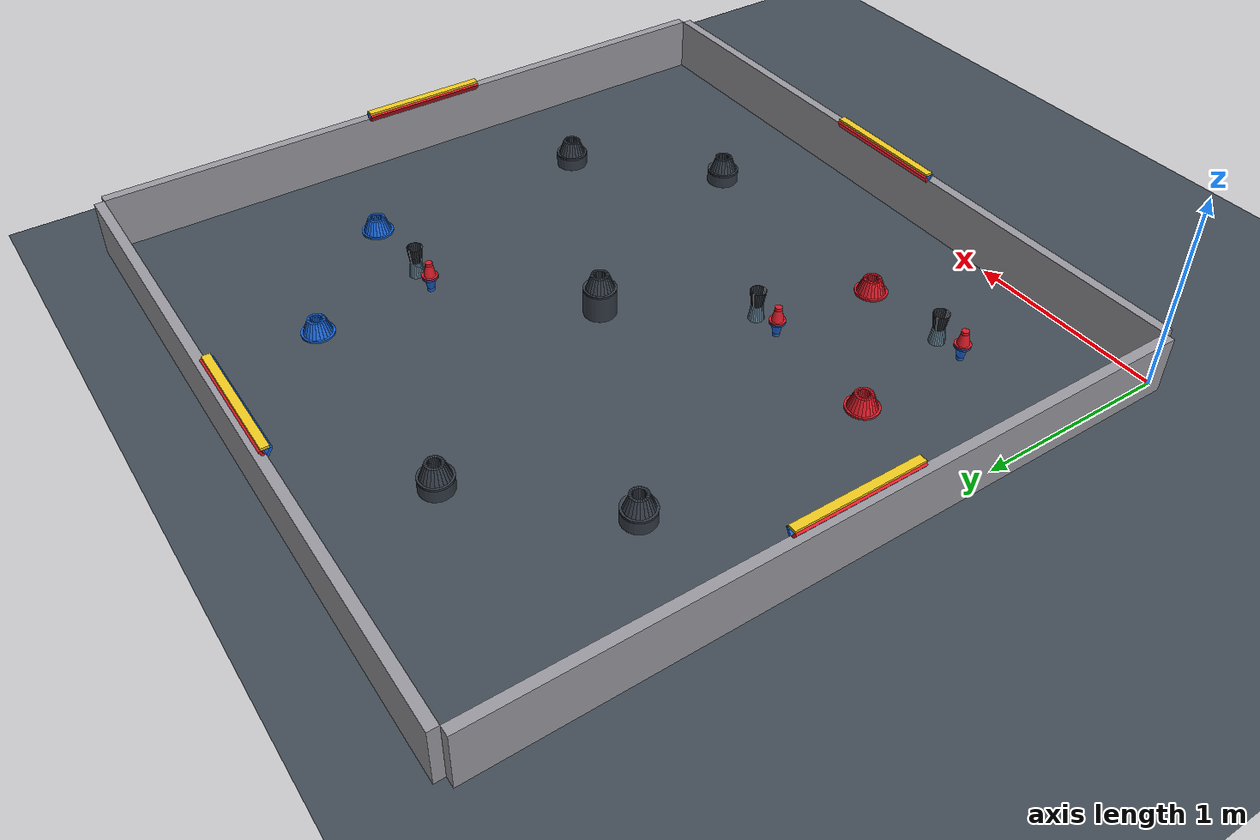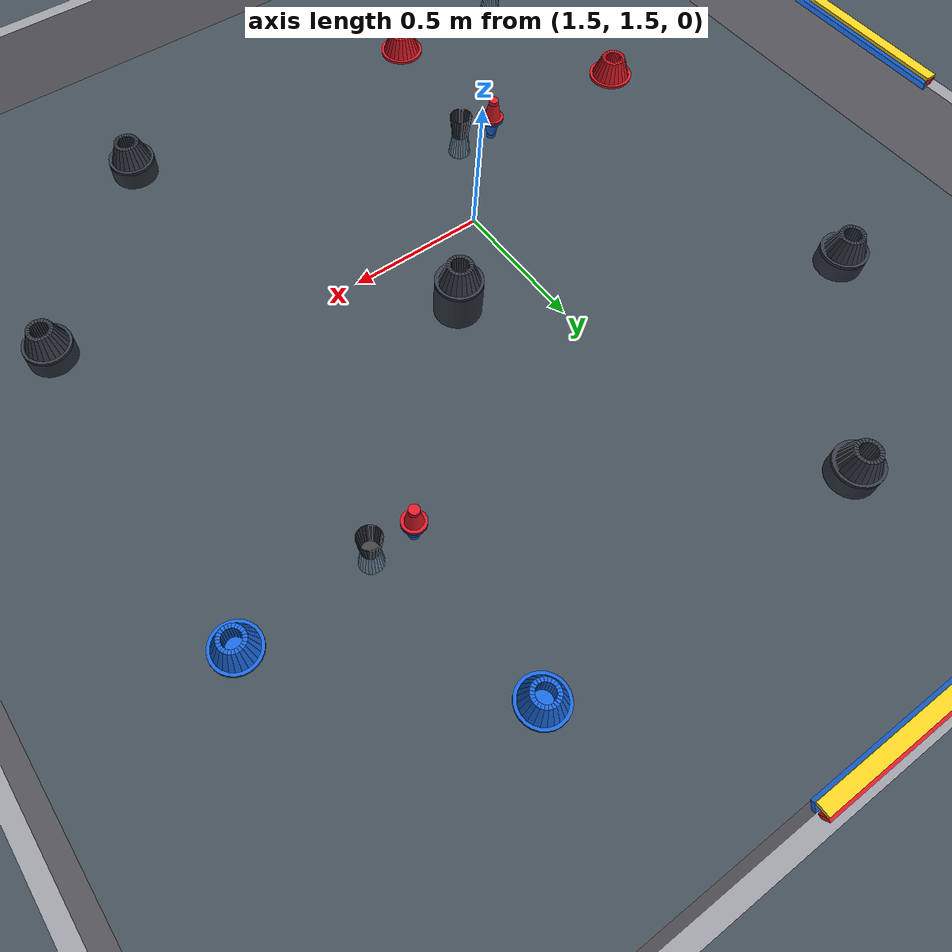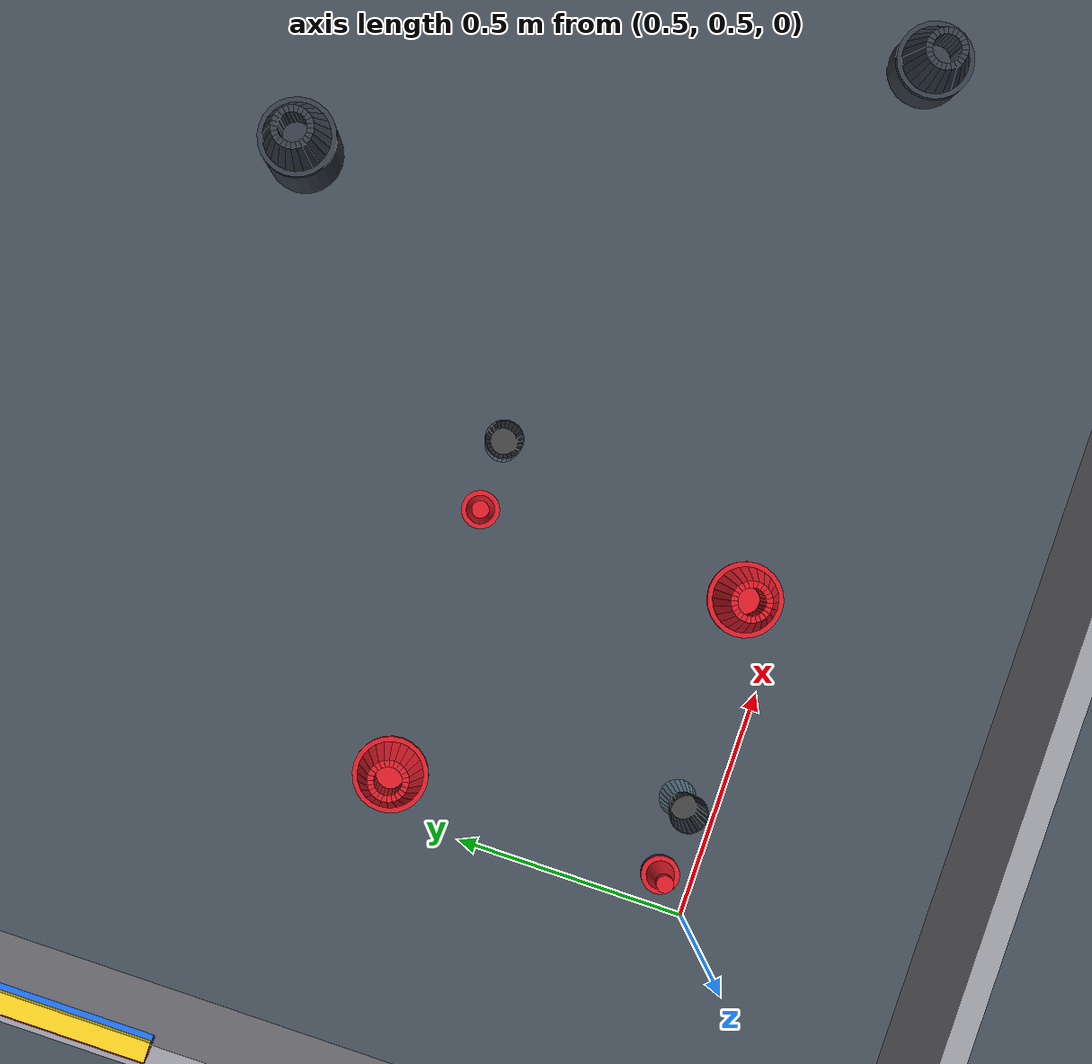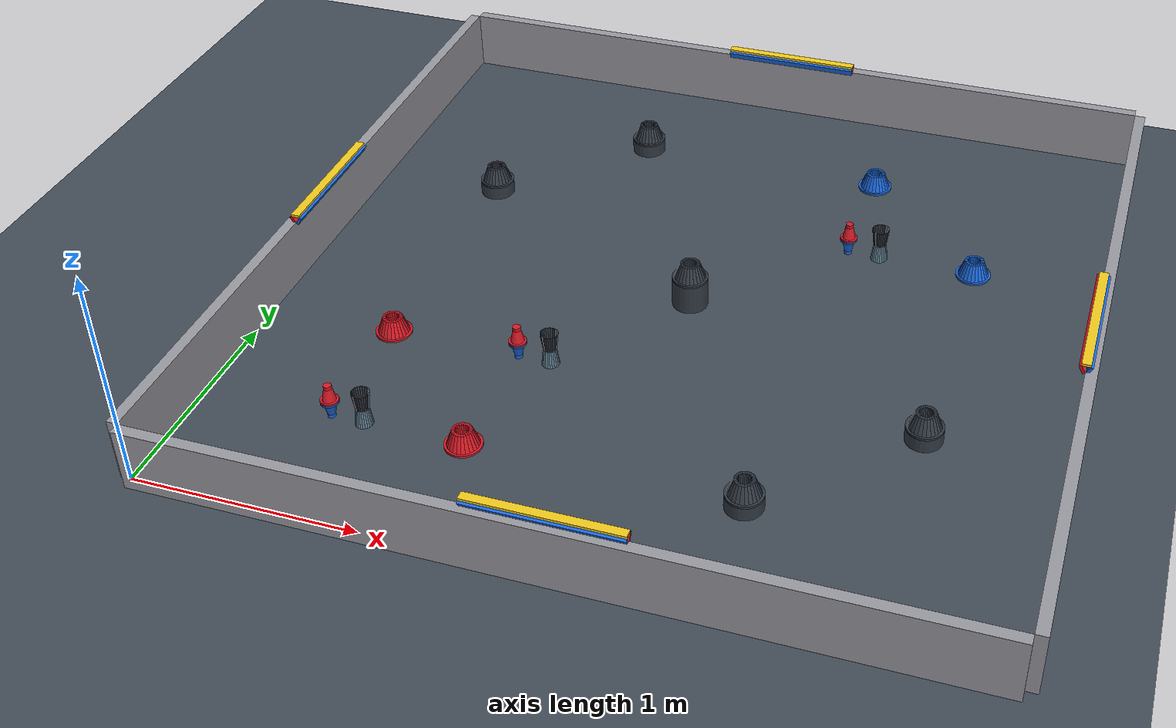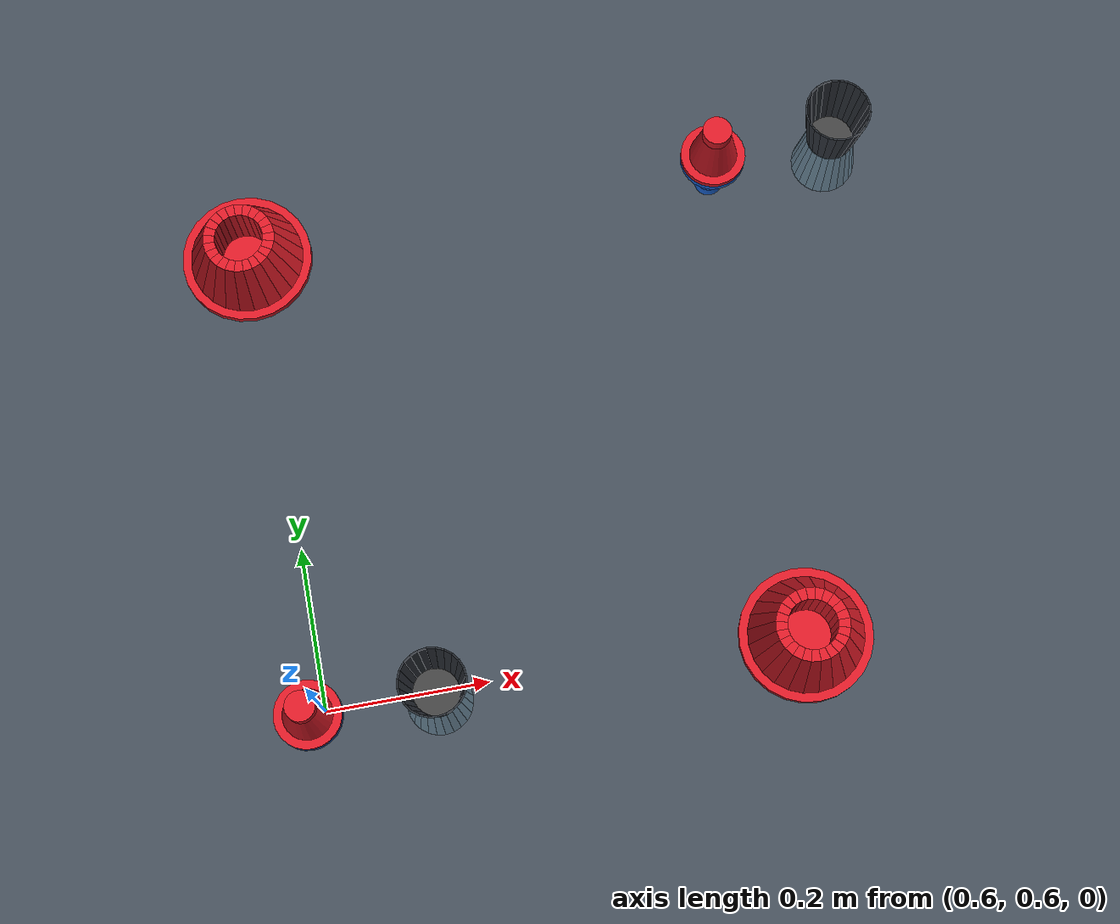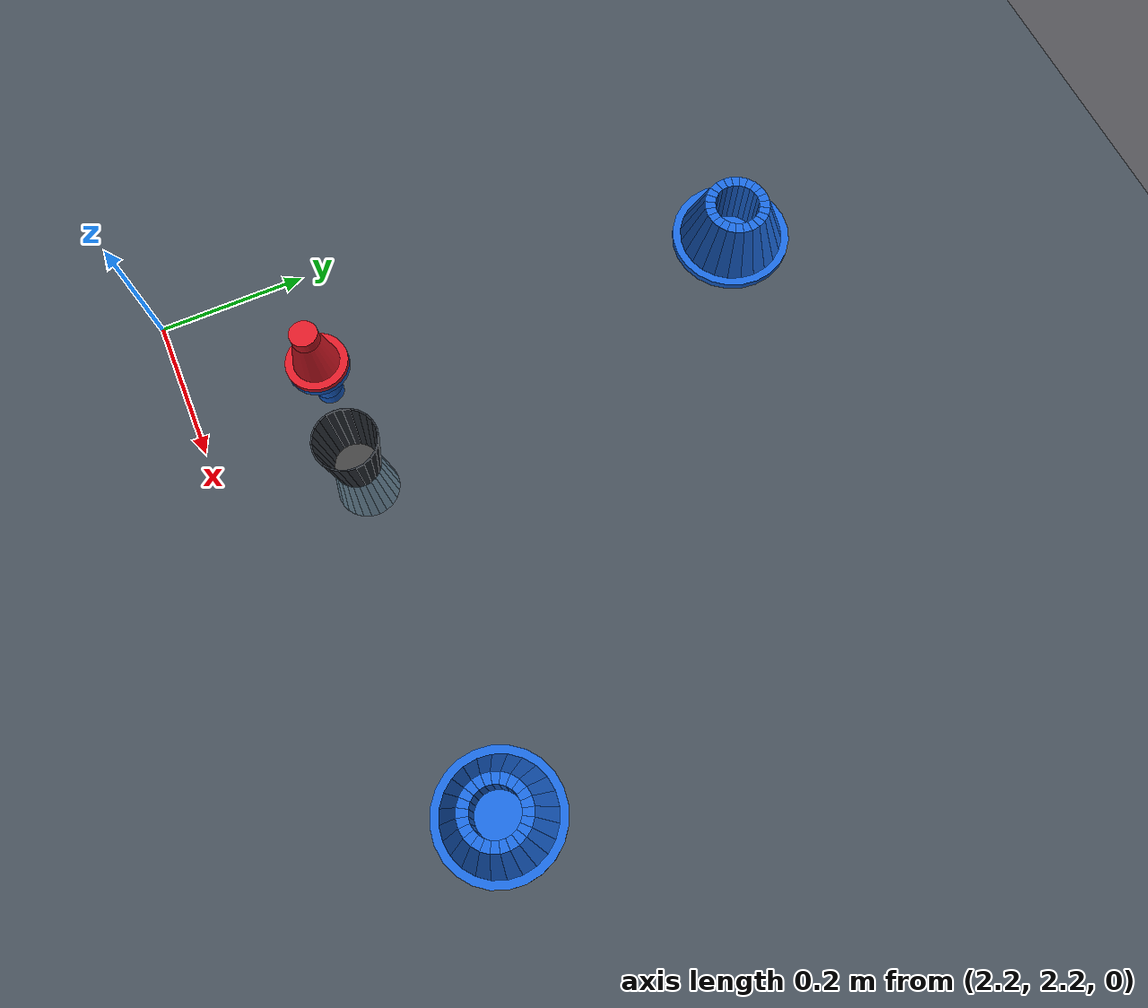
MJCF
<mujoco model="override_contact_fixture"><compiler angle="radian" /><option timestep=".002" gravity="0 0 -9.81" integrator="implicitfast" cone="elliptic" iterations="80" /><default><geom friction=".65 .002 .0001" solref=".01 1" /></default><visual><global offwidth="1200" offheight="900" /><headlight ambient=".5 .5 .5" diffuse=".7 .7 .7" /></visual><asset><mesh name="goal_0_wall_0" vertex="0.07125 0.0 0.01 0.06882221512309611 0.018440856963554603 0.01 0.03005 0.0 0.01 0.029026071079986504 0.007777512305330748 0.01 0.0444 0.0 0.0825 0.04288710668723463 0.011491565602551922 0.0825 0.03005 0.0 0.0825 0.029026071079986504 0.007777512305330748 0.0825" /><mesh name="goal_0_wall_1" vertex="0.06882221512309611 0.018440856963554603 0.01 0.06170431001964125 0.03562499999999999 0.01 0.029026071079986504 0.007777512305330748 0.01 0.026024063383722384 0.015024999999999998 0.01 0.04288710668723463 0.011491565602551922 0.0825 0.03845152792802908 0.022199999999999998 0.0825 0.029026071079986504 0.007777512305330748 0.0825 0.026024063383722384 0.015024999999999998 0.0825" /><mesh name="goal_0_wall_2" vertex="0.06170431001964125 0.03562499999999999 0.01 0.05038135815954151 0.0503813581595415 0.01 0.026024063383722384 0.015024999999999998 0.01 0.021248558774655753 0.02124855877465575 0.01 0.03845152792802908 0.022199999999999998 0.0825 0.03139554108468271 0.03139554108468271 0.0825 0.026024063383722384 0.015024999999999998 0.0825 0.021248558774655753 0.02124855877465575 0.0825" /><mesh name="goal_0_wall_3" vertex="0.05038135815954151 0.0503813581595415 0.01 0.035625000000000004 0.061704310019641245 0.01 0.021248558774655753 0.02124855877465575 0.01 0.015025000000000004 0.02602406338372238 0.01 0.03139554108468271 0.03139554108468271 0.0825 0.022200000000000004 0.038451527928029076 0.0825 0.021248558774655753 0.02124855877465575 0.0825 0.015025000000000004 0.02602406338372238 0.0825" /><mesh name="goal_0_wall_4" vertex="0.035625000000000004 0.061704310019641245 0.01 0.018440856963554603 0.06882221512309611 0.01 0.015025000000000004 0.02602406338372238 0.01 0.007777512305330748 0.029026071079986504 0.01 0.022200000000000004 0.038451527928029076 0.0825 0.011491565602551922 0.04288710668723463 0.0825 0.015025000000000004 0.02602406338372238 0.0825 0.007777512305330748 0.029026071079986504 0.0825" /><mesh name="goal_0_wall_5" vertex="0.018440856963554603 0.06882221512309611 0.01 4.362804221962445e-18 0.07125 0.01 0.007777512305330748 0.029026071079986504 0.01 1.8400318157188982e-18 0.03005 0.01 0.011491565602551922 0.04288710668723463 0.0825 2.718715894107124e-18 0.0444 0.0825 0.007777512305330748 0.029026071079986504 0.0825 1.8400318157188982e-18 0.03005 0.0825" /><mesh name="goal_0_wall_6" vertex="4.362804221962445e-18 0.07125 0.01 -0.018440856963554592 0.06882221512309611 0.01 1.8400318157188982e-18 0.03005 0.01 -0.007777512305330745 0.029026071079986504 0.01 2.718715894107124e-18 0.0444 0.0825 -0.011491565602551917 0.04288710668723463 0.0825 1.8400318157188982e-18 0.03005 0.0825 -0.007777512305330745 0.029026071079986504 0.0825" /><mesh name="goal_0_wall_7" vertex="-0.018440856963554592 0.06882221512309611 0.01 -0.03562499999999998 0.06170431001964125 0.01 -0.007777512305330745 0.029026071079986504 0.01 -0.015024999999999995 0.026024063383722384 0.01 -0.011491565602551917 0.04288710668723463 0.0825 -0.022199999999999994 0.03845152792802908 0.0825 -0.007777512305330745 0.029026071079986504 0.0825 -0.015024999999999995 0.026024063383722384 0.0825" /><mesh name="goal_0_wall_8" vertex="-0.03562499999999998 0.06170431001964125 0.01 -0.0503813581595415 0.05038135815954151 0.01 -0.015024999999999995 0.026024063383722384 0.01 -0.02124855877465575 0.021248558774655753 0.01 -0.022199999999999994 0.03845152792802908 0.0825 -0.03139554108468271 0.03139554108468271 0.0825 -0.015024999999999995 0.026024063383722384 0.0825 -0.02124855877465575 0.021248558774655753 0.0825" /><mesh name="goal_0_wall_9" vertex="-0.0503813581595415 0.05038135815954151 0.01 -0.06170431001964125 0.03562499999999999 0.01 -0.02124855877465575 0.021248558774655753 0.01 -0.026024063383722384 0.015024999999999998 0.01 -0.03139554108468271 0.03139554108468271 0.0825 -0.03845152792802908 0.022199999999999998 0.0825 -0.02124855877465575 0.021248558774655753 0.0825 -0.026024063383722384 0.015024999999999998 0.0825" /><mesh name="goal_0_wall_10" vertex="-0.06170431001964125 0.03562499999999999 0.01 -0.06882221512309611 0.01844085696355462 0.01 -0.026024063383722384 0.015024999999999998 0.01 -0.0290260710799865 0.007777512305330757 0.01 -0.03845152792802908 0.022199999999999998 0.0825 -0.04288710668723463 0.011491565602551934 0.0825 -0.026024063383722384 0.015024999999999998 0.0825 -0.0290260710799865 0.007777512305330757 0.0825" /><mesh name="goal_0_wall_11" vertex="-0.06882221512309611 0.01844085696355462 0.01 -0.07125 8.72560844392489e-18 0.01 -0.0290260710799865 0.007777512305330757 0.01 -0.03005 3.6800636314377964e-18 0.01 -0.04288710668723463 0.011491565602551934 0.0825 -0.0444 5.437431788214248e-18 0.0825 -0.0290260710799865 0.007777512305330757 0.0825 -0.03005 3.6800636314377964e-18 0.0825" /><mesh name="goal_0_wall_12" vertex="-0.07125 8.72560844392489e-18 0.01 -0.06882221512309611 -0.018440856963554606 0.01 -0.03005 3.6800636314377964e-18 0.01 -0.029026071079986504 -0.00777751230533075 0.01 -0.0444 5.437431788214248e-18 0.0825 -0.04288710668723463 -0.011491565602551924 0.0825 -0.03005 3.6800636314377964e-18 0.0825 -0.029026071079986504 -0.00777751230533075 0.0825" /><mesh name="goal_0_wall_13" vertex="-0.06882221512309611 -0.018440856963554606 0.01 -0.06170431001964126 -0.03562499999999998 0.01 -0.029026071079986504 -0.00777751230533075 0.01 -0.026024063383722387 -0.015024999999999993 0.01 -0.04288710668723463 -0.011491565602551924 0.0825 -0.03845152792802908 -0.02219999999999999 0.0825 -0.029026071079986504 -0.00777751230533075 0.0825 -0.026024063383722387 -0.015024999999999993 0.0825" /><mesh name="goal_0_wall_14" vertex="-0.06170431001964126 -0.03562499999999998 0.01 -0.050381358159541534 -0.05038135815954148 0.01 -0.026024063383722387 -0.015024999999999993 0.01 -0.021248558774655764 -0.021248558774655743 0.01 -0.03845152792802908 -0.02219999999999999 0.0825 -0.031395541084682725 -0.03139554108468269 0.0825 -0.026024063383722387 -0.015024999999999993 0.0825 -0.021248558774655764 -0.021248558774655743 0.0825" /><mesh name="goal_0_wall_15" vertex="-0.050381358159541534 -0.05038135815954148 0.01 -0.03562500000000003 -0.06170431001964123 0.01 -0.021248558774655764 -0.021248558774655743 0.01 -0.015025000000000014 -0.026024063383722373 0.01 -0.031395541084682725 -0.03139554108468269 0.0825 -0.022200000000000022 -0.03845152792802906 0.0825 -0.021248558774655764 -0.021248558774655743 0.0825 -0.015025000000000014 -0.026024063383722373 0.0825" /><mesh name="goal_0_wall_16" vertex="-0.03562500000000003 -0.06170431001964123 0.01 -0.018440856963554592 -0.06882221512309611 0.01 -0.015025000000000014 -0.026024063383722373 0.01 -0.007777512305330745 -0.029026071079986504 0.01 -0.022200000000000022 -0.03845152792802906 0.0825 -0.011491565602551917 -0.04288710668723463 0.0825 -0.015025000000000014 -0.026024063383722373 0.0825 -0.007777512305330745 -0.029026071079986504 0.0825" /><mesh name="goal_0_wall_17" vertex="-0.018440856963554592 -0.06882221512309611 0.01 -1.3088412665887336e-17 -0.07125 0.01 -0.007777512305330745 -0.029026071079986504 0.01 -5.520095447156694e-18 -0.03005 0.01 -0.011491565602551917 -0.04288710668723463 0.0825 -8.156147682321372e-18 -0.0444 0.0825 -0.007777512305330745 -0.029026071079986504 0.0825 -5.520095447156694e-18 -0.03005 0.0825" /><mesh name="goal_0_wall_18" vertex="-1.3088412665887336e-17 -0.07125 0.01 0.018440856963554568 -0.06882221512309612 0.01 -5.520095447156694e-18 -0.03005 0.01 0.007777512305330735 -0.029026071079986508 0.01 -8.156147682321372e-18 -0.0444 0.0825 0.011491565602551901 -0.04288710668723464 0.0825 -5.520095447156694e-18 -0.03005 0.0825 0.007777512305330735 -0.029026071079986508 0.0825" /><mesh name="goal_0_wall_19" vertex="0.018440856963554568 -0.06882221512309612 0.01 0.035625000000000004 -0.061704310019641245 0.01 0.007777512305330735 -0.029026071079986508 0.01 0.015025000000000004 -0.02602406338372238 0.01 0.011491565602551901 -0.04288710668723464 0.0825 0.022200000000000004 -0.038451527928029076 0.0825 0.007777512305330735 -0.029026071079986508 0.0825 0.015025000000000004 -0.02602406338372238 0.0825" /><mesh name="goal_0_wall_20" vertex="0.035625000000000004 -0.061704310019641245 0.01 0.05038135815954149 -0.05038135815954152 0.01 0.015025000000000004 -0.02602406338372238 0.01 0.021248558774655747 -0.021248558774655757 0.01 0.022200000000000004 -0.038451527928029076 0.0825 0.031395541084682704 -0.03139554108468272 0.0825 0.015025000000000004 -0.02602406338372238 0.0825 0.021248558774655747 -0.021248558774655757 0.0825" /><mesh name="goal_0_wall_21" vertex="0.05038135815954149 -0.05038135815954152 0.01 0.06170431001964123 -0.03562500000000003 0.01 0.021248558774655747 -0.021248558774655757 0.01 0.026024063383722373 -0.015025000000000014 0.01 0.031395541084682704 -0.03139554108468272 0.0825 0.03845152792802906 -0.022200000000000022 0.0825 0.021248558774655747 -0.021248558774655757 0.0825 0.026024063383722373 -0.015025000000000014 0.0825" /><mesh name="goal_0_wall_22" vertex="0.06170431001964123 -0.03562500000000003 0.01 0.0688222151230961 -0.01844085696355466 0.01 0.026024063383722373 -0.015025000000000014 0.01 0.029026071079986497 -0.007777512305330773 0.01 0.03845152792802906 -0.022200000000000022 0.0825 0.042887106687234625 -0.011491565602551958 0.0825 0.026024063383722373 -0.015025000000000014 0.0825 0.029026071079986497 -0.007777512305330773 0.0825" /><mesh name="goal_0_wall_23" vertex="0.0688222151230961 -0.01844085696355466 0.01 0.07125 -1.745121688784978e-17 0.01 0.029026071079986497 -0.007777512305330773 0.01 0.03005 -7.360127262875593e-18 0.01 0.042887106687234625 -0.011491565602551958 0.0825 0.0444 -1.0874863576428497e-17 0.0825 0.029026071079986497 -0.007777512305330773 0.0825 0.03005 -7.360127262875593e-18 0.0825" /><mesh name="goal_1_wall_0" vertex="0.07125 0.0 0.01 0.06882221512309611 0.018440856963554603 0.01 0.03005 0.0 0.01 0.029026071079986504 0.007777512305330748 0.01 0.0444 0.0 0.0825 0.04288710668723463 0.011491565602551922 0.0825 0.03005 0.0 0.0825 0.029026071079986504 0.007777512305330748 0.0825" /><mesh name="goal_1_wall_1" vertex="0.06882221512309611 0.018440856963554603 0.01 0.06170431001964125 0.03562499999999999 0.01 0.029026071079986504 0.007777512305330748 0.01 0.026024063383722384 0.015024999999999998 0.01 0.04288710668723463 0.011491565602551922 0.0825 0.03845152792802908 0.022199999999999998 0.0825 0.029026071079986504 0.007777512305330748 0.0825 0.026024063383722384 0.015024999999999998 0.0825" /><mesh name="goal_1_wall_2" vertex="0.06170431001964125 0.03562499999999999 0.01 0.05038135815954151 0.0503813581595415 0.01 0.026024063383722384 0.015024999999999998 0.01 0.021248558774655753 0.02124855877465575 0.01 0.03845152792802908 0.022199999999999998 0.0825 0.03139554108468271 0.03139554108468271 0.0825 0.026024063383722384 0.015024999999999998 0.0825 0.021248558774655753 0.02124855877465575 0.0825" /><mesh name="goal_1_wall_3" vertex="0.05038135815954151 0.0503813581595415 0.01 0.035625000000000004 0.061704310019641245 0.01 0.021248558774655753 0.02124855877465575 0.01 0.015025000000000004 0.02602406338372238 0.01 0.03139554108468271 0.03139554108468271 0.0825 0.022200000000000004 0.038451527928029076 0.0825 0.021248558774655753 0.02124855877465575 0.0825 0.015025000000000004 0.02602406338372238 0.0825" /><mesh name="goal_1_wall_4" vertex="0.035625000000000004 0.061704310019641245 0.01 0.018440856963554603 0.06882221512309611 0.01 0.015025000000000004 0.02602406338372238 0.01 0.007777512305330748 0.029026071079986504 0.01 0.022200000000000004 0.038451527928029076 0.0825 0.011491565602551922 0.04288710668723463 0.0825 0.015025000000000004 0.02602406338372238 0.0825 0.007777512305330748 0.029026071079986504 0.0825" /><mesh name="goal_1_wall_5" vertex="0.018440856963554603 0.06882221512309611 0.01 4.362804221962445e-18 0.07125 0.01 0.007777512305330748 0.029026071079986504 0.01 1.8400318157188982e-18 0.03005 0.01 0.011491565602551922 0.04288710668723463 0.0825 2.718715894107124e-18 0.0444 0.0825 0.007777512305330748 0.029026071079986504 0.0825 1.8400318157188982e-18 0.03005 0.0825" /><mesh name="goal_1_wall_6" vertex="4.362804221962445e-18 0.07125 0.01 -0.018440856963554592 0.06882221512309611 0.01 1.8400318157188982e-18 0.03005 0.01 -0.007777512305330745 0.029026071079986504 0.01 2.718715894107124e-18 0.0444 0.0825 -0.011491565602551917 0.04288710668723463 0.0825 1.8400318157188982e-18 0.03005 0.0825 -0.007777512305330745 0.029026071079986504 0.0825" /><mesh name="goal_1_wall_7" vertex="-0.018440856963554592 0.06882221512309611 0.01 -0.03562499999999998 0.06170431001964125 0.01 -0.007777512305330745 0.029026071079986504 0.01 -0.015024999999999995 0.026024063383722384 0.01 -0.011491565602551917 0.04288710668723463 0.0825 -0.022199999999999994 0.03845152792802908 0.0825 -0.007777512305330745 0.029026071079986504 0.0825 -0.015024999999999995 0.026024063383722384 0.0825" /><mesh name="goal_1_wall_8" vertex="-0.03562499999999998 0.06170431001964125 0.01 -0.0503813581595415 0.05038135815954151 0.01 -0.015024999999999995 0.026024063383722384 0.01 -0.02124855877465575 0.021248558774655753 0.01 -0.022199999999999994 0.03845152792802908 0.0825 -0.03139554108468271 0.03139554108468271 0.0825 -0.015024999999999995 0.026024063383722384 0.0825 -0.02124855877465575 0.021248558774655753 0.0825" /><mesh name="goal_1_wall_9" vertex="-0.0503813581595415 0.05038135815954151 0.01 -0.06170431001964125 0.03562499999999999 0.01 -0.02124855877465575 0.021248558774655753 0.01 -0.026024063383722384 0.015024999999999998 0.01 -0.03139554108468271 0.03139554108468271 0.0825 -0.03845152792802908 0.022199999999999998 0.0825 -0.02124855877465575 0.021248558774655753 0.0825 -0.026024063383722384 0.015024999999999998 0.0825" /><mesh name="goal_1_wall_10" vertex="-0.06170431001964125 0.03562499999999999 0.01 -0.06882221512309611 0.01844085696355462 0.01 -0.026024063383722384 0.015024999999999998 0.01 -0.0290260710799865 0.007777512305330757 0.01 -0.03845152792802908 0.022199999999999998 0.0825 -0.04288710668723463 0.011491565602551934 0.0825 -0.026024063383722384 0.015024999999999998 0.0825 -0.0290260710799865 0.007777512305330757 0.0825" /><mesh name="goal_1_wall_11" vertex="-0.06882221512309611 0.01844085696355462 0.01 -0.07125 8.72560844392489e-18 0.01 -0.0290260710799865 0.007777512305330757 0.01 -0.03005 3.6800636314377964e-18 0.01 -0.04288710668723463 0.011491565602551934 0.0825 -0.0444 5.437431788214248e-18 0.0825 -0.0290260710799865 0.007777512305330757 0.0825 -0.03005 3.6800636314377964e-18 0.0825" /><mesh name="goal_1_wall_12" vertex="-0.07125 8.72560844392489e-18 0.01 -0.06882221512309611 -0.018440856963554606 0.01 -0.03005 3.6800636314377964e-18 0.01 -0.029026071079986504 -0.00777751230533075 0.01 -0.0444 5.437431788214248e-18 0.0825 -0.04288710668723463 -0.011491565602551924 0.0825 -0.03005 3.6800636314377964e-18 0.0825 -0.029026071079986504 -0.00777751230533075 0.0825" /><mesh name="goal_1_wall_13" vertex="-0.06882221512309611 -0.018440856963554606 0.01 -0.06170431001964126 -0.03562499999999998 0.01 -0.029026071079986504 -0.00777751230533075 0.01 -0.026024063383722387 -0.015024999999999993 0.01 -0.04288710668723463 -0.011491565602551924 0.0825 -0.03845152792802908 -0.02219999999999999 0.0825 -0.029026071079986504 -0.00777751230533075 0.0825 -0.026024063383722387 -0.015024999999999993 0.0825" /><mesh name="goal_1_wall_14" vertex="-0.06170431001964126 -0.03562499999999998 0.01 -0.050381358159541534 -0.05038135815954148 0.01 -0.026024063383722387 -0.015024999999999993 0.01 -0.021248558774655764 -0.021248558774655743 0.01 -0.03845152792802908 -0.02219999999999999 0.0825 -0.031395541084682725 -0.03139554108468269 0.0825 -0.026024063383722387 -0.015024999999999993 0.0825 -0.021248558774655764 -0.021248558774655743 0.0825" /><mesh name="goal_1_wall_15" vertex="-0.050381358159541534 -0.05038135815954148 0.01 -0.03562500000000003 -0.06170431001964123 0.01 -0.021248558774655764 -0.021248558774655743 0.01 -0.015025000000000014 -0.026024063383722373 0.01 -0.031395541084682725 -0.03139554108468269 0.0825 -0.022200000000000022 -0.03845152792802906 0.0825 -0.021248558774655764 -0.021248558774655743 0.0825 -0.015025000000000014 -0.026024063383722373 0.0825" /><mesh name="goal_1_wall_16" vertex="-0.03562500000000003 -0.06170431001964123 0.01 -0.018440856963554592 -0.06882221512309611 0.01 -0.015025000000000014 -0.026024063383722373 0.01 -0.007777512305330745 -0.029026071079986504 0.01 -0.022200000000000022 -0.03845152792802906 0.0825 -0.011491565602551917 -0.04288710668723463 0.0825 -0.015025000000000014 -0.026024063383722373 0.0825 -0.007777512305330745 -0.029026071079986504 0.0825" /><mesh name="goal_1_wall_17" vertex="-0.018440856963554592 -0.06882221512309611 0.01 -1.3088412665887336e-17 -0.07125 0.01 -0.007777512305330745 -0.029026071079986504 0.01 -5.520095447156694e-18 -0.03005 0.01 -0.011491565602551917 -0.04288710668723463 0.0825 -8.156147682321372e-18 -0.0444 0.0825 -0.007777512305330745 -0.029026071079986504 0.0825 -5.520095447156694e-18 -0.03005 0.0825" /><mesh name="goal_1_wall_18" vertex="-1.3088412665887336e-17 -0.07125 0.01 0.018440856963554568 -0.06882221512309612 0.01 -5.520095447156694e-18 -0.03005 0.01 0.007777512305330735 -0.029026071079986508 0.01 -8.156147682321372e-18 -0.0444 0.0825 0.011491565602551901 -0.04288710668723464 0.0825 -5.520095447156694e-18 -0.03005 0.0825 0.007777512305330735 -0.029026071079986508 0.0825" /><mesh name="goal_1_wall_19" vertex="0.018440856963554568 -0.06882221512309612 0.01 0.035625000000000004 -0.061704310019641245 0.01 0.007777512305330735 -0.029026071079986508 0.01 0.015025000000000004 -0.02602406338372238 0.01 0.011491565602551901 -0.04288710668723464 0.0825 0.022200000000000004 -0.038451527928029076 0.0825 0.007777512305330735 -0.029026071079986508 0.0825 0.015025000000000004 -0.02602406338372238 0.0825" /><mesh name="goal_1_wall_20" vertex="0.035625000000000004 -0.061704310019641245 0.01 0.05038135815954149 -0.05038135815954152 0.01 0.015025000000000004 -0.02602406338372238 0.01 0.021248558774655747 -0.021248558774655757 0.01 0.022200000000000004 -0.038451527928029076 0.0825 0.031395541084682704 -0.03139554108468272 0.0825 0.015025000000000004 -0.02602406338372238 0.0825 0.021248558774655747 -0.021248558774655757 0.0825" /><mesh name="goal_1_wall_21" vertex="0.05038135815954149 -0.05038135815954152 0.01 0.06170431001964123 -0.03562500000000003 0.01 0.021248558774655747 -0.021248558774655757 0.01 0.026024063383722373 -0.015025000000000014 0.01 0.031395541084682704 -0.03139554108468272 0.0825 0.03845152792802906 -0.022200000000000022 0.0825 0.021248558774655747 -0.021248558774655757 0.0825 0.026024063383722373 -0.015025000000000014 0.0825" /><mesh name="goal_1_wall_22" vertex="0.06170431001964123 -0.03562500000000003 0.01 0.0688222151230961 -0.01844085696355466 0.01 0.026024063383722373 -0.015025000000000014 0.01 0.029026071079986497 -0.007777512305330773 0.01 0.03845152792802906 -0.022200000000000022 0.0825 0.042887106687234625 -0.011491565602551958 0.0825 0.026024063383722373 -0.015025000000000014 0.0825 0.029026071079986497 -0.007777512305330773 0.0825" /><mesh name="goal_1_wall_23" vertex="0.0688222151230961 -0.01844085696355466 0.01 0.07125 -1.745121688784978e-17 0.01 0.029026071079986497 -0.007777512305330773 0.01 0.03005 -7.360127262875593e-18 0.01 0.042887106687234625 -0.011491565602551958 0.0825 0.0444 -1.0874863576428497e-17 0.0825 0.029026071079986497 -0.007777512305330773 0.0825 0.03005 -7.360127262875593e-18 0.0825" /><mesh name="goal_2_wall_0" vertex="0.07125 0.0 0.01 0.06882221512309611 0.018440856963554603 0.01 0.03005 0.0 0.01 0.029026071079986504 0.007777512305330748 0.01 0.0444 0.0 0.0825 0.04288710668723463 0.011491565602551922 0.0825 0.03005 0.0 0.0825 0.029026071079986504 0.007777512305330748 0.0825" /><mesh name="goal_2_wall_1" vertex="0.06882221512309611 0.018440856963554603 0.01 0.06170431001964125 0.03562499999999999 0.01 0.029026071079986504 0.007777512305330748 0.01 0.026024063383722384 0.015024999999999998 0.01 0.04288710668723463 0.011491565602551922 0.0825 0.03845152792802908 0.022199999999999998 0.0825 0.029026071079986504 0.007777512305330748 0.0825 0.026024063383722384 0.015024999999999998 0.0825" /><mesh name="goal_2_wall_2" vertex="0.06170431001964125 0.03562499999999999 0.01 0.05038135815954151 0.0503813581595415 0.01 0.026024063383722384 0.015024999999999998 0.01 0.021248558774655753 0.02124855877465575 0.01 0.03845152792802908 0.022199999999999998 0.0825 0.03139554108468271 0.03139554108468271 0.0825 0.026024063383722384 0.015024999999999998 0.0825 0.021248558774655753 0.02124855877465575 0.0825" /><mesh name="goal_2_wall_3" vertex="0.05038135815954151 0.0503813581595415 0.01 0.035625000000000004 0.061704310019641245 0.01 0.021248558774655753 0.02124855877465575 0.01 0.015025000000000004 0.02602406338372238 0.01 0.03139554108468271 0.03139554108468271 0.0825 0.022200000000000004 0.038451527928029076 0.0825 0.021248558774655753 0.02124855877465575 0.0825 0.015025000000000004 0.02602406338372238 0.0825" /><mesh name="goal_2_wall_4" vertex="0.035625000000000004 0.061704310019641245 0.01 0.018440856963554603 0.06882221512309611 0.01 0.015025000000000004 0.02602406338372238 0.01 0.007777512305330748 0.029026071079986504 0.01 0.022200000000000004 0.038451527928029076 0.0825 0.011491565602551922 0.04288710668723463 0.0825 0.015025000000000004 0.02602406338372238 0.0825 0.007777512305330748 0.029026071079986504 0.0825" /><mesh name="goal_2_wall_5" vertex="0.018440856963554603 0.06882221512309611 0.01 4.362804221962445e-18 0.07125 0.01 0.007777512305330748 0.029026071079986504 0.01 1.8400318157188982e-18 0.03005 0.01 0.011491565602551922 0.04288710668723463 0.0825 2.718715894107124e-18 0.0444 0.0825 0.007777512305330748 0.029026071079986504 0.0825 1.8400318157188982e-18 0.03005 0.0825" /><mesh name="goal_2_wall_6" vertex="4.362804221962445e-18 0.07125 0.01 -0.018440856963554592 0.06882221512309611 0.01 1.8400318157188982e-18 0.03005 0.01 -0.007777512305330745 0.029026071079986504 0.01 2.718715894107124e-18 0.0444 0.0825 -0.011491565602551917 0.04288710668723463 0.0825 1.8400318157188982e-18 0.03005 0.0825 -0.007777512305330745 0.029026071079986504 0.0825" /><mesh name="goal_2_wall_7" vertex="-0.018440856963554592 0.06882221512309611 0.01 -0.03562499999999998 0.06170431001964125 0.01 -0.007777512305330745 0.029026071079986504 0.01 -0.015024999999999995 0.026024063383722384 0.01 -0.011491565602551917 0.04288710668723463 0.0825 -0.022199999999999994 0.03845152792802908 0.0825 -0.007777512305330745 0.029026071079986504 0.0825 -0.015024999999999995 0.026024063383722384 0.0825" /><mesh name="goal_2_wall_8" vertex="-0.03562499999999998 0.06170431001964125 0.01 -0.0503813581595415 0.05038135815954151 0.01 -0.015024999999999995 0.026024063383722384 0.01 -0.02124855877465575 0.021248558774655753 0.01 -0.022199999999999994 0.03845152792802908 0.0825 -0.03139554108468271 0.03139554108468271 0.0825 -0.015024999999999995 0.026024063383722384 0.0825 -0.02124855877465575 0.021248558774655753 0.0825" /><mesh name="goal_2_wall_9" vertex="-0.0503813581595415 0.05038135815954151 0.01 -0.06170431001964125 0.03562499999999999 0.01 -0.02124855877465575 0.021248558774655753 0.01 -0.026024063383722384 0.015024999999999998 0.01 -0.03139554108468271 0.03139554108468271 0.0825 -0.03845152792802908 0.022199999999999998 0.0825 -0.02124855877465575 0.021248558774655753 0.0825 -0.026024063383722384 0.015024999999999998 0.0825" /><mesh name="goal_2_wall_10" vertex="-0.06170431001964125 0.03562499999999999 0.01 -0.06882221512309611 0.01844085696355462 0.01 -0.026024063383722384 0.015024999999999998 0.01 -0.0290260710799865 0.007777512305330757 0.01 -0.03845152792802908 0.022199999999999998 0.0825 -0.04288710668723463 0.011491565602551934 0.0825 -0.026024063383722384 0.015024999999999998 0.0825 -0.0290260710799865 0.007777512305330757 0.0825" /><mesh name="goal_2_wall_11" vertex="-0.06882221512309611 0.01844085696355462 0.01 -0.07125 8.72560844392489e-18 0.01 -0.0290260710799865 0.007777512305330757 0.01 -0.03005 3.6800636314377964e-18 0.01 -0.04288710668723463 0.011491565602551934 0.0825 -0.0444 5.437431788214248e-18 0.0825 -0.0290260710799865 0.007777512305330757 0.0825 -0.03005 3.6800636314377964e-18 0.0825" /><mesh name="goal_2_wall_12" vertex="-0.07125 8.72560844392489e-18 0.01 -0.06882221512309611 -0.018440856963554606 0.01 -0.03005 3.6800636314377964e-18 0.01 -0.029026071079986504 -0.00777751230533075 0.01 -0.0444 5.437431788214248e-18 0.0825 -0.04288710668723463 -0.011491565602551924 0.0825 -0.03005 3.6800636314377964e-18 0.0825 -0.029026071079986504 -0.00777751230533075 0.0825" /><mesh name="goal_2_wall_13" vertex="-0.06882221512309611 -0.018440856963554606 0.01 -0.06170431001964126 -0.03562499999999998 0.01 -0.029026071079986504 -0.00777751230533075 0.01 -0.026024063383722387 -0.015024999999999993 0.01 -0.04288710668723463 -0.011491565602551924 0.0825 -0.03845152792802908 -0.02219999999999999 0.0825 -0.029026071079986504 -0.00777751230533075 0.0825 -0.026024063383722387 -0.015024999999999993 0.0825" /><mesh name="goal_2_wall_14" vertex="-0.06170431001964126 -0.03562499999999998 0.01 -0.050381358159541534 -0.05038135815954148 0.01 -0.026024063383722387 -0.015024999999999993 0.01 -0.021248558774655764 -0.021248558774655743 0.01 -0.03845152792802908 -0.02219999999999999 0.0825 -0.031395541084682725 -0.03139554108468269 0.0825 -0.026024063383722387 -0.015024999999999993 0.0825 -0.021248558774655764 -0.021248558774655743 0.0825" /><mesh name="goal_2_wall_15" vertex="-0.050381358159541534 -0.05038135815954148 0.01 -0.03562500000000003 -0.06170431001964123 0.01 -0.021248558774655764 -0.021248558774655743 0.01 -0.015025000000000014 -0.026024063383722373 0.01 -0.031395541084682725 -0.03139554108468269 0.0825 -0.022200000000000022 -0.03845152792802906 0.0825 -0.021248558774655764 -0.021248558774655743 0.0825 -0.015025000000000014 -0.026024063383722373 0.0825" /><mesh name="goal_2_wall_16" vertex="-0.03562500000000003 -0.06170431001964123 0.01 -0.018440856963554592 -0.06882221512309611 0.01 -0.015025000000000014 -0.026024063383722373 0.01 -0.007777512305330745 -0.029026071079986504 0.01 -0.022200000000000022 -0.03845152792802906 0.0825 -0.011491565602551917 -0.04288710668723463 0.0825 -0.015025000000000014 -0.026024063383722373 0.0825 -0.007777512305330745 -0.029026071079986504 0.0825" /><mesh name="goal_2_wall_17" vertex="-0.018440856963554592 -0.06882221512309611 0.01 -1.3088412665887336e-17 -0.07125 0.01 -0.007777512305330745 -0.029026071079986504 0.01 -5.520095447156694e-18 -0.03005 0.01 -0.011491565602551917 -0.04288710668723463 0.0825 -8.156147682321372e-18 -0.0444 0.0825 -0.007777512305330745 -0.029026071079986504 0.0825 -5.520095447156694e-18 -0.03005 0.0825" /><mesh name="goal_2_wall_18" vertex="-1.3088412665887336e-17 -0.07125 0.01 0.018440856963554568 -0.06882221512309612 0.01 -5.520095447156694e-18 -0.03005 0.01 0.007777512305330735 -0.029026071079986508 0.01 -8.156147682321372e-18 -0.0444 0.0825 0.011491565602551901 -0.04288710668723464 0.0825 -5.520095447156694e-18 -0.03005 0.0825 0.007777512305330735 -0.029026071079986508 0.0825" /><mesh name="goal_2_wall_19" vertex="0.018440856963554568 -0.06882221512309612 0.01 0.035625000000000004 -0.061704310019641245 0.01 0.007777512305330735 -0.029026071079986508 0.01 0.015025000000000004 -0.02602406338372238 0.01 0.011491565602551901 -0.04288710668723464 0.0825 0.022200000000000004 -0.038451527928029076 0.0825 0.007777512305330735 -0.029026071079986508 0.0825 0.015025000000000004 -0.02602406338372238 0.0825" /><mesh name="goal_2_wall_20" vertex="0.035625000000000004 -0.061704310019641245 0.01 0.05038135815954149 -0.05038135815954152 0.01 0.015025000000000004 -0.02602406338372238 0.01 0.021248558774655747 -0.021248558774655757 0.01 0.022200000000000004 -0.038451527928029076 0.0825 0.031395541084682704 -0.03139554108468272 0.0825 0.015025000000000004 -0.02602406338372238 0.0825 0.021248558774655747 -0.021248558774655757 0.0825" /><mesh name="goal_2_wall_21" vertex="0.05038135815954149 -0.05038135815954152 0.01 0.06170431001964123 -0.03562500000000003 0.01 0.021248558774655747 -0.021248558774655757 0.01 0.026024063383722373 -0.015025000000000014 0.01 0.031395541084682704 -0.03139554108468272 0.0825 0.03845152792802906 -0.022200000000000022 0.0825 0.021248558774655747 -0.021248558774655757 0.0825 0.026024063383722373 -0.015025000000000014 0.0825" /><mesh name="goal_2_wall_22" vertex="0.06170431001964123 -0.03562500000000003 0.01 0.0688222151230961 -0.01844085696355466 0.01 0.026024063383722373 -0.015025000000000014 0.01 0.029026071079986497 -0.007777512305330773 0.01 0.03845152792802906 -0.022200000000000022 0.0825 0.042887106687234625 -0.011491565602551958 0.0825 0.026024063383722373 -0.015025000000000014 0.0825 0.029026071079986497 -0.007777512305330773 0.0825" /><mesh name="goal_2_wall_23" vertex="0.0688222151230961 -0.01844085696355466 0.01 0.07125 -1.745121688784978e-17 0.01 0.029026071079986497 -0.007777512305330773 0.01 0.03005 -7.360127262875593e-18 0.01 0.042887106687234625 -0.011491565602551958 0.0825 0.0444 -1.0874863576428497e-17 0.0825 0.029026071079986497 -0.007777512305330773 0.0825 0.03005 -7.360127262875593e-18 0.0825" /><mesh name="goal_3_wall_0" vertex="0.07125 0.0 0.01 0.06882221512309611 0.018440856963554603 0.01 0.03005 0.0 0.01 0.029026071079986504 0.007777512305330748 0.01 0.0444 0.0 0.0825 0.04288710668723463 0.011491565602551922 0.0825 0.03005 0.0 0.0825 0.029026071079986504 0.007777512305330748 0.0825" /><mesh name="goal_3_wall_1" vertex="0.06882221512309611 0.018440856963554603 0.01 0.06170431001964125 0.03562499999999999 0.01 0.029026071079986504 0.007777512305330748 0.01 0.026024063383722384 0.015024999999999998 0.01 0.04288710668723463 0.011491565602551922 0.0825 0.03845152792802908 0.022199999999999998 0.0825 0.029026071079986504 0.007777512305330748 0.0825 0.026024063383722384 0.015024999999999998 0.0825" /><mesh name="goal_3_wall_2" vertex="0.06170431001964125 0.03562499999999999 0.01 0.05038135815954151 0.0503813581595415 0.01 0.026024063383722384 0.015024999999999998 0.01 0.021248558774655753 0.02124855877465575 0.01 0.03845152792802908 0.022199999999999998 0.0825 0.03139554108468271 0.03139554108468271 0.0825 0.026024063383722384 0.015024999999999998 0.0825 0.021248558774655753 0.02124855877465575 0.0825" /><mesh name="goal_3_wall_3" vertex="0.05038135815954151 0.0503813581595415 0.01 0.035625000000000004 0.061704310019641245 0.01 0.021248558774655753 0.02124855877465575 0.01 0.015025000000000004 0.02602406338372238 0.01 0.03139554108468271 0.03139554108468271 0.0825 0.022200000000000004 0.038451527928029076 0.0825 0.021248558774655753 0.02124855877465575 0.0825 0.015025000000000004 0.02602406338372238 0.0825" /><mesh name="goal_3_wall_4" vertex="0.035625000000000004 0.061704310019641245 0.01 0.018440856963554603 0.06882221512309611 0.01 0.015025000000000004 0.02602406338372238 0.01 0.007777512305330748 0.029026071079986504 0.01 0.022200000000000004 0.038451527928029076 0.0825 0.011491565602551922 0.04288710668723463 0.0825 0.015025000000000004 0.02602406338372238 0.0825 0.007777512305330748 0.029026071079986504 0.0825" /><mesh name="goal_3_wall_5" vertex="0.018440856963554603 0.06882221512309611 0.01 4.362804221962445e-18 0.07125 0.01 0.007777512305330748 0.029026071079986504 0.01 1.8400318157188982e-18 0.03005 0.01 0.011491565602551922 0.04288710668723463 0.0825 2.718715894107124e-18 0.0444 0.0825 0.007777512305330748 0.029026071079986504 0.0825 1.8400318157188982e-18 0.03005 0.0825" /><mesh name="goal_3_wall_6" vertex="4.362804221962445e-18 0.07125 0.01 -0.018440856963554592 0.06882221512309611 0.01 1.8400318157188982e-18 0.03005 0.01 -0.007777512305330745 0.029026071079986504 0.01 2.718715894107124e-18 0.0444 0.0825 -0.011491565602551917 0.04288710668723463 0.0825 1.8400318157188982e-18 0.03005 0.0825 -0.007777512305330745 0.029026071079986504 0.0825" /><mesh name="goal_3_wall_7" vertex="-0.018440856963554592 0.06882221512309611 0.01 -0.03562499999999998 0.06170431001964125 0.01 -0.007777512305330745 0.029026071079986504 0.01 -0.015024999999999995 0.026024063383722384 0.01 -0.011491565602551917 0.04288710668723463 0.0825 -0.022199999999999994 0.03845152792802908 0.0825 -0.007777512305330745 0.029026071079986504 0.0825 -0.015024999999999995 0.026024063383722384 0.0825" /><mesh name="goal_3_wall_8" vertex="-0.03562499999999998 0.06170431001964125 0.01 -0.0503813581595415 0.05038135815954151 0.01 -0.015024999999999995 0.026024063383722384 0.01 -0.02124855877465575 0.021248558774655753 0.01 -0.022199999999999994 0.03845152792802908 0.0825 -0.03139554108468271 0.03139554108468271 0.0825 -0.015024999999999995 0.026024063383722384 0.0825 -0.02124855877465575 0.021248558774655753 0.0825" /><mesh name="goal_3_wall_9" vertex="-0.0503813581595415 0.05038135815954151 0.01 -0.06170431001964125 0.03562499999999999 0.01 -0.02124855877465575 0.021248558774655753 0.01 -0.026024063383722384 0.015024999999999998 0.01 -0.03139554108468271 0.03139554108468271 0.0825 -0.03845152792802908 0.022199999999999998 0.0825 -0.02124855877465575 0.021248558774655753 0.0825 -0.026024063383722384 0.015024999999999998 0.0825" /><mesh name="goal_3_wall_10" vertex="-0.06170431001964125 0.03562499999999999 0.01 -0.06882221512309611 0.01844085696355462 0.01 -0.026024063383722384 0.015024999999999998 0.01 -0.0290260710799865 0.007777512305330757 0.01 -0.03845152792802908 0.022199999999999998 0.0825 -0.04288710668723463 0.011491565602551934 0.0825 -0.026024063383722384 0.015024999999999998 0.0825 -0.0290260710799865 0.007777512305330757 0.0825" /><mesh name="goal_3_wall_11" vertex="-0.06882221512309611 0.01844085696355462 0.01 -0.07125 8.72560844392489e-18 0.01 -0.0290260710799865 0.007777512305330757 0.01 -0.03005 3.6800636314377964e-18 0.01 -0.04288710668723463 0.011491565602551934 0.0825 -0.0444 5.437431788214248e-18 0.0825 -0.0290260710799865 0.007777512305330757 0.0825 -0.03005 3.6800636314377964e-18 0.0825" /><mesh name="goal_3_wall_12" vertex="-0.07125 8.72560844392489e-18 0.01 -0.06882221512309611 -0.018440856963554606 0.01 -0.03005 3.6800636314377964e-18 0.01 -0.029026071079986504 -0.00777751230533075 0.01 -0.0444 5.437431788214248e-18 0.0825 -0.04288710668723463 -0.011491565602551924 0.0825 -0.03005 3.6800636314377964e-18 0.0825 -0.029026071079986504 -0.00777751230533075 0.0825" /><mesh name="goal_3_wall_13" vertex="-0.06882221512309611 -0.018440856963554606 0.01 -0.06170431001964126 -0.03562499999999998 0.01 -0.029026071079986504 -0.00777751230533075 0.01 -0.026024063383722387 -0.015024999999999993 0.01 -0.04288710668723463 -0.011491565602551924 0.0825 -0.03845152792802908 -0.02219999999999999 0.0825 -0.029026071079986504 -0.00777751230533075 0.0825 -0.026024063383722387 -0.015024999999999993 0.0825" /><mesh name="goal_3_wall_14" vertex="-0.06170431001964126 -0.03562499999999998 0.01 -0.050381358159541534 -0.05038135815954148 0.01 -0.026024063383722387 -0.015024999999999993 0.01 -0.021248558774655764 -0.021248558774655743 0.01 -0.03845152792802908 -0.02219999999999999 0.0825 -0.031395541084682725 -0.03139554108468269 0.0825 -0.026024063383722387 -0.015024999999999993 0.0825 -0.021248558774655764 -0.021248558774655743 0.0825" /><mesh name="goal_3_wall_15" vertex="-0.050381358159541534 -0.05038135815954148 0.01 -0.03562500000000003 -0.06170431001964123 0.01 -0.021248558774655764 -0.021248558774655743 0.01 -0.015025000000000014 -0.026024063383722373 0.01 -0.031395541084682725 -0.03139554108468269 0.0825 -0.022200000000000022 -0.03845152792802906 0.0825 -0.021248558774655764 -0.021248558774655743 0.0825 -0.015025000000000014 -0.026024063383722373 0.0825" /><mesh name="goal_3_wall_16" vertex="-0.03562500000000003 -0.06170431001964123 0.01 -0.018440856963554592 -0.06882221512309611 0.01 -0.015025000000000014 -0.026024063383722373 0.01 -0.007777512305330745 -0.029026071079986504 0.01 -0.022200000000000022 -0.03845152792802906 0.0825 -0.011491565602551917 -0.04288710668723463 0.0825 -0.015025000000000014 -0.026024063383722373 0.0825 -0.007777512305330745 -0.029026071079986504 0.0825" /><mesh name="goal_3_wall_17" vertex="-0.018440856963554592 -0.06882221512309611 0.01 -1.3088412665887336e-17 -0.07125 0.01 -0.007777512305330745 -0.029026071079986504 0.01 -5.520095447156694e-18 -0.03005 0.01 -0.011491565602551917 -0.04288710668723463 0.0825 -8.156147682321372e-18 -0.0444 0.0825 -0.007777512305330745 -0.029026071079986504 0.0825 -5.520095447156694e-18 -0.03005 0.0825" /><mesh name="goal_3_wall_18" vertex="-1.3088412665887336e-17 -0.07125 0.01 0.018440856963554568 -0.06882221512309612 0.01 -5.520095447156694e-18 -0.03005 0.01 0.007777512305330735 -0.029026071079986508 0.01 -8.156147682321372e-18 -0.0444 0.0825 0.011491565602551901 -0.04288710668723464 0.0825 -5.520095447156694e-18 -0.03005 0.0825 0.007777512305330735 -0.029026071079986508 0.0825" /><mesh name="goal_3_wall_19" vertex="0.018440856963554568 -0.06882221512309612 0.01 0.035625000000000004 -0.061704310019641245 0.01 0.007777512305330735 -0.029026071079986508 0.01 0.015025000000000004 -0.02602406338372238 0.01 0.011491565602551901 -0.04288710668723464 0.0825 0.022200000000000004 -0.038451527928029076 0.0825 0.007777512305330735 -0.029026071079986508 0.0825 0.015025000000000004 -0.02602406338372238 0.0825" /><mesh name="goal_3_wall_20" vertex="0.035625000000000004 -0.061704310019641245 0.01 0.05038135815954149 -0.05038135815954152 0.01 0.015025000000000004 -0.02602406338372238 0.01 0.021248558774655747 -0.021248558774655757 0.01 0.022200000000000004 -0.038451527928029076 0.0825 0.031395541084682704 -0.03139554108468272 0.0825 0.015025000000000004 -0.02602406338372238 0.0825 0.021248558774655747 -0.021248558774655757 0.0825" /><mesh name="goal_3_wall_21" vertex="0.05038135815954149 -0.05038135815954152 0.01 0.06170431001964123 -0.03562500000000003 0.01 0.021248558774655747 -0.021248558774655757 0.01 0.026024063383722373 -0.015025000000000014 0.01 0.031395541084682704 -0.03139554108468272 0.0825 0.03845152792802906 -0.022200000000000022 0.0825 0.021248558774655747 -0.021248558774655757 0.0825 0.026024063383722373 -0.015025000000000014 0.0825" /><mesh name="goal_3_wall_22" vertex="0.06170431001964123 -0.03562500000000003 0.01 0.0688222151230961 -0.01844085696355466 0.01 0.026024063383722373 -0.015025000000000014 0.01 0.029026071079986497 -0.007777512305330773 0.01 0.03845152792802906 -0.022200000000000022 0.0825 0.042887106687234625 -0.011491565602551958 0.0825 0.026024063383722373 -0.015025000000000014 0.0825 0.029026071079986497 -0.007777512305330773 0.0825" /><mesh name="goal_3_wall_23" vertex="0.0688222151230961 -0.01844085696355466 0.01 0.07125 -1.745121688784978e-17 0.01 0.029026071079986497 -0.007777512305330773 0.01 0.03005 -7.360127262875593e-18 0.01 0.042887106687234625 -0.011491565602551958 0.0825 0.0444 -1.0874863576428497e-17 0.0825 0.029026071079986497 -0.007777512305330773 0.0825 0.03005 -7.360127262875593e-18 0.0825" /><mesh name="goal_4_wall_0" vertex="0.07125 0.0 0.07399999999999998 0.06882221512309611 0.018440856963554603 0.07399999999999998 0.03005 0.0 0.07399999999999998 0.029026071079986504 0.007777512305330748 0.07399999999999998 0.0444 0.0 0.1465 0.04288710668723463 0.011491565602551922 0.1465 0.03005 0.0 0.1465 0.029026071079986504 0.007777512305330748 0.1465" /><mesh name="goal_4_wall_1" vertex="0.06882221512309611 0.018440856963554603 0.07399999999999998 0.06170431001964125 0.03562499999999999 0.07399999999999998 0.029026071079986504 0.007777512305330748 0.07399999999999998 0.026024063383722384 0.015024999999999998 0.07399999999999998 0.04288710668723463 0.011491565602551922 0.1465 0.03845152792802908 0.022199999999999998 0.1465 0.029026071079986504 0.007777512305330748 0.1465 0.026024063383722384 0.015024999999999998 0.1465" /><mesh name="goal_4_wall_2" vertex="0.06170431001964125 0.03562499999999999 0.07399999999999998 0.05038135815954151 0.0503813581595415 0.07399999999999998 0.026024063383722384 0.015024999999999998 0.07399999999999998 0.021248558774655753 0.02124855877465575 0.07399999999999998 0.03845152792802908 0.022199999999999998 0.1465 0.03139554108468271 0.03139554108468271 0.1465 0.026024063383722384 0.015024999999999998 0.1465 0.021248558774655753 0.02124855877465575 0.1465" /><mesh name="goal_4_wall_3" vertex="0.05038135815954151 0.0503813581595415 0.07399999999999998 0.035625000000000004 0.061704310019641245 0.07399999999999998 0.021248558774655753 0.02124855877465575 0.07399999999999998 0.015025000000000004 0.02602406338372238 0.07399999999999998 0.03139554108468271 0.03139554108468271 0.1465 0.022200000000000004 0.038451527928029076 0.1465 0.021248558774655753 0.02124855877465575 0.1465 0.015025000000000004 0.02602406338372238 0.1465" /><mesh name="goal_4_wall_4" vertex="0.035625000000000004 0.061704310019641245 0.07399999999999998 0.018440856963554603 0.06882221512309611 0.07399999999999998 0.015025000000000004 0.02602406338372238 0.07399999999999998 0.007777512305330748 0.029026071079986504 0.07399999999999998 0.022200000000000004 0.038451527928029076 0.1465 0.011491565602551922 0.04288710668723463 0.1465 0.015025000000000004 0.02602406338372238 0.1465 0.007777512305330748 0.029026071079986504 0.1465" /><mesh name="goal_4_wall_5" vertex="0.018440856963554603 0.06882221512309611 0.07399999999999998 4.362804221962445e-18 0.07125 0.07399999999999998 0.007777512305330748 0.029026071079986504 0.07399999999999998 1.8400318157188982e-18 0.03005 0.07399999999999998 0.011491565602551922 0.04288710668723463 0.1465 2.718715894107124e-18 0.0444 0.1465 0.007777512305330748 0.029026071079986504 0.1465 1.8400318157188982e-18 0.03005 0.1465" /><mesh name="goal_4_wall_6" vertex="4.362804221962445e-18 0.07125 0.07399999999999998 -0.018440856963554592 0.06882221512309611 0.07399999999999998 1.8400318157188982e-18 0.03005 0.07399999999999998 -0.007777512305330745 0.029026071079986504 0.07399999999999998 2.718715894107124e-18 0.0444 0.1465 -0.011491565602551917 0.04288710668723463 0.1465 1.8400318157188982e-18 0.03005 0.1465 -0.007777512305330745 0.029026071079986504 0.1465" /><mesh name="goal_4_wall_7" vertex="-0.018440856963554592 0.06882221512309611 0.07399999999999998 -0.03562499999999998 0.06170431001964125 0.07399999999999998 -0.007777512305330745 0.029026071079986504 0.07399999999999998 -0.015024999999999995 0.026024063383722384 0.07399999999999998 -0.011491565602551917 0.04288710668723463 0.1465 -0.022199999999999994 0.03845152792802908 0.1465 -0.007777512305330745 0.029026071079986504 0.1465 -0.015024999999999995 0.026024063383722384 0.1465" /><mesh name="goal_4_wall_8" vertex="-0.03562499999999998 0.06170431001964125 0.07399999999999998 -0.0503813581595415 0.05038135815954151 0.07399999999999998 -0.015024999999999995 0.026024063383722384 0.07399999999999998 -0.02124855877465575 0.021248558774655753 0.07399999999999998 -0.022199999999999994 0.03845152792802908 0.1465 -0.03139554108468271 0.03139554108468271 0.1465 -0.015024999999999995 0.026024063383722384 0.1465 -0.02124855877465575 0.021248558774655753 0.1465" /><mesh name="goal_4_wall_9" vertex="-0.0503813581595415 0.05038135815954151 0.07399999999999998 -0.06170431001964125 0.03562499999999999 0.07399999999999998 -0.02124855877465575 0.021248558774655753 0.07399999999999998 -0.026024063383722384 0.015024999999999998 0.07399999999999998 -0.03139554108468271 0.03139554108468271 0.1465 -0.03845152792802908 0.022199999999999998 0.1465 -0.02124855877465575 0.021248558774655753 0.1465 -0.026024063383722384 0.015024999999999998 0.1465" /><mesh name="goal_4_wall_10" vertex="-0.06170431001964125 0.03562499999999999 0.07399999999999998 -0.06882221512309611 0.01844085696355462 0.07399999999999998 -0.026024063383722384 0.015024999999999998 0.07399999999999998 -0.0290260710799865 0.007777512305330757 0.07399999999999998 -0.03845152792802908 0.022199999999999998 0.1465 -0.04288710668723463 0.011491565602551934 0.1465 -0.026024063383722384 0.015024999999999998 0.1465 -0.0290260710799865 0.007777512305330757 0.1465" /><mesh name="goal_4_wall_11" vertex="-0.06882221512309611 0.01844085696355462 0.07399999999999998 -0.07125 8.72560844392489e-18 0.07399999999999998 -0.0290260710799865 0.007777512305330757 0.07399999999999998 -0.03005 3.6800636314377964e-18 0.07399999999999998 -0.04288710668723463 0.011491565602551934 0.1465 -0.0444 5.437431788214248e-18 0.1465 -0.0290260710799865 0.007777512305330757 0.1465 -0.03005 3.6800636314377964e-18 0.1465" /><mesh name="goal_4_wall_12" vertex="-0.07125 8.72560844392489e-18 0.07399999999999998 -0.06882221512309611 -0.018440856963554606 0.07399999999999998 -0.03005 3.6800636314377964e-18 0.07399999999999998 -0.029026071079986504 -0.00777751230533075 0.07399999999999998 -0.0444 5.437431788214248e-18 0.1465 -0.04288710668723463 -0.011491565602551924 0.1465 -0.03005 3.6800636314377964e-18 0.1465 -0.029026071079986504 -0.00777751230533075 0.1465" /><mesh name="goal_4_wall_13" vertex="-0.06882221512309611 -0.018440856963554606 0.07399999999999998 -0.06170431001964126 -0.03562499999999998 0.07399999999999998 -0.029026071079986504 -0.00777751230533075 0.07399999999999998 -0.026024063383722387 -0.015024999999999993 0.07399999999999998 -0.04288710668723463 -0.011491565602551924 0.1465 -0.03845152792802908 -0.02219999999999999 0.1465 -0.029026071079986504 -0.00777751230533075 0.1465 -0.026024063383722387 -0.015024999999999993 0.1465" /><mesh name="goal_4_wall_14" vertex="-0.06170431001964126 -0.03562499999999998 0.07399999999999998 -0.050381358159541534 -0.05038135815954148 0.07399999999999998 -0.026024063383722387 -0.015024999999999993 0.07399999999999998 -0.021248558774655764 -0.021248558774655743 0.07399999999999998 -0.03845152792802908 -0.02219999999999999 0.1465 -0.031395541084682725 -0.03139554108468269 0.1465 -0.026024063383722387 -0.015024999999999993 0.1465 -0.021248558774655764 -0.021248558774655743 0.1465" /><mesh name="goal_4_wall_15" vertex="-0.050381358159541534 -0.05038135815954148 0.07399999999999998 -0.03562500000000003 -0.06170431001964123 0.07399999999999998 -0.021248558774655764 -0.021248558774655743 0.07399999999999998 -0.015025000000000014 -0.026024063383722373 0.07399999999999998 -0.031395541084682725 -0.03139554108468269 0.1465 -0.022200000000000022 -0.03845152792802906 0.1465 -0.021248558774655764 -0.021248558774655743 0.1465 -0.015025000000000014 -0.026024063383722373 0.1465" /><mesh name="goal_4_wall_16" vertex="-0.03562500000000003 -0.06170431001964123 0.07399999999999998 -0.018440856963554592 -0.06882221512309611 0.07399999999999998 -0.015025000000000014 -0.026024063383722373 0.07399999999999998 -0.007777512305330745 -0.029026071079986504 0.07399999999999998 -0.022200000000000022 -0.03845152792802906 0.1465 -0.011491565602551917 -0.04288710668723463 0.1465 -0.015025000000000014 -0.026024063383722373 0.1465 -0.007777512305330745 -0.029026071079986504 0.1465" /><mesh name="goal_4_wall_17" vertex="-0.018440856963554592 -0.06882221512309611 0.07399999999999998 -1.3088412665887336e-17 -0.07125 0.07399999999999998 -0.007777512305330745 -0.029026071079986504 0.07399999999999998 -5.520095447156694e-18 -0.03005 0.07399999999999998 -0.011491565602551917 -0.04288710668723463 0.1465 -8.156147682321372e-18 -0.0444 0.1465 -0.007777512305330745 -0.029026071079986504 0.1465 -5.520095447156694e-18 -0.03005 0.1465" /><mesh name="goal_4_wall_18" vertex="-1.3088412665887336e-17 -0.07125 0.07399999999999998 0.018440856963554568 -0.06882221512309612 0.07399999999999998 -5.520095447156694e-18 -0.03005 0.07399999999999998 0.007777512305330735 -0.029026071079986508 0.07399999999999998 -8.156147682321372e-18 -0.0444 0.1465 0.011491565602551901 -0.04288710668723464 0.1465 -5.520095447156694e-18 -0.03005 0.1465 0.007777512305330735 -0.029026071079986508 0.1465" /><mesh name="goal_4_wall_19" vertex="0.018440856963554568 -0.06882221512309612 0.07399999999999998 0.035625000000000004 -0.061704310019641245 0.07399999999999998 0.007777512305330735 -0.029026071079986508 0.07399999999999998 0.015025000000000004 -0.02602406338372238 0.07399999999999998 0.011491565602551901 -0.04288710668723464 0.1465 0.022200000000000004 -0.038451527928029076 0.1465 0.007777512305330735 -0.029026071079986508 0.1465 0.015025000000000004 -0.02602406338372238 0.1465" /><mesh name="goal_4_wall_20" vertex="0.035625000000000004 -0.061704310019641245 0.07399999999999998 0.05038135815954149 -0.05038135815954152 0.07399999999999998 0.015025000000000004 -0.02602406338372238 0.07399999999999998 0.021248558774655747 -0.021248558774655757 0.07399999999999998 0.022200000000000004 -0.038451527928029076 0.1465 0.031395541084682704 -0.03139554108468272 0.1465 0.015025000000000004 -0.02602406338372238 0.1465 0.021248558774655747 -0.021248558774655757 0.1465" /><mesh name="goal_4_wall_21" vertex="0.05038135815954149 -0.05038135815954152 0.07399999999999998 0.06170431001964123 -0.03562500000000003 0.07399999999999998 0.021248558774655747 -0.021248558774655757 0.07399999999999998 0.026024063383722373 -0.015025000000000014 0.07399999999999998 0.031395541084682704 -0.03139554108468272 0.1465 0.03845152792802906 -0.022200000000000022 0.1465 0.021248558774655747 -0.021248558774655757 0.1465 0.026024063383722373 -0.015025000000000014 0.1465" /><mesh name="goal_4_wall_22" vertex="0.06170431001964123 -0.03562500000000003 0.07399999999999998 0.0688222151230961 -0.01844085696355466 0.07399999999999998 0.026024063383722373 -0.015025000000000014 0.07399999999999998 0.029026071079986497 -0.007777512305330773 0.07399999999999998 0.03845152792802906 -0.022200000000000022 0.1465 0.042887106687234625 -0.011491565602551958 0.1465 0.026024063383722373 -0.015025000000000014 0.1465 0.029026071079986497 -0.007777512305330773 0.1465" /><mesh name="goal_4_wall_23" vertex="0.0688222151230961 -0.01844085696355466 0.07399999999999998 0.07125 -1.745121688784978e-17 0.07399999999999998 0.029026071079986497 -0.007777512305330773 0.07399999999999998 0.03005 -7.360127262875593e-18 0.07399999999999998 0.042887106687234625 -0.011491565602551958 0.1465 0.0444 -1.0874863576428497e-17 0.1465 0.029026071079986497 -0.007777512305330773 0.1465 0.03005 -7.360127262875593e-18 0.1465" /><mesh name="goal_5_wall_0" vertex="0.07125 0.0 0.07399999999999998 0.06882221512309611 0.018440856963554603 0.07399999999999998 0.03005 0.0 0.07399999999999998 0.029026071079986504 0.007777512305330748 0.07399999999999998 0.0444 0.0 0.1465 0.04288710668723463 0.011491565602551922 0.1465 0.03005 0.0 0.1465 0.029026071079986504 0.007777512305330748 0.1465" /><mesh name="goal_5_wall_1" vertex="0.06882221512309611 0.018440856963554603 0.07399999999999998 0.06170431001964125 0.03562499999999999 0.07399999999999998 0.029026071079986504 0.007777512305330748 0.07399999999999998 0.026024063383722384 0.015024999999999998 0.07399999999999998 0.04288710668723463 0.011491565602551922 0.1465 0.03845152792802908 0.022199999999999998 0.1465 0.029026071079986504 0.007777512305330748 0.1465 0.026024063383722384 0.015024999999999998 0.1465" /><mesh name="goal_5_wall_2" vertex="0.06170431001964125 0.03562499999999999 0.07399999999999998 0.05038135815954151 0.0503813581595415 0.07399999999999998 0.026024063383722384 0.015024999999999998 0.07399999999999998 0.021248558774655753 0.02124855877465575 0.07399999999999998 0.03845152792802908 0.022199999999999998 0.1465 0.03139554108468271 0.03139554108468271 0.1465 0.026024063383722384 0.015024999999999998 0.1465 0.021248558774655753 0.02124855877465575 0.1465" /><mesh name="goal_5_wall_3" vertex="0.05038135815954151 0.0503813581595415 0.07399999999999998 0.035625000000000004 0.061704310019641245 0.07399999999999998 0.021248558774655753 0.02124855877465575 0.07399999999999998 0.015025000000000004 0.02602406338372238 0.07399999999999998 0.03139554108468271 0.03139554108468271 0.1465 0.022200000000000004 0.038451527928029076 0.1465 0.021248558774655753 0.02124855877465575 0.1465 0.015025000000000004 0.02602406338372238 0.1465" /><mesh name="goal_5_wall_4" vertex="0.035625000000000004 0.061704310019641245 0.07399999999999998 0.018440856963554603 0.06882221512309611 0.07399999999999998 0.015025000000000004 0.02602406338372238 0.07399999999999998 0.007777512305330748 0.029026071079986504 0.07399999999999998 0.022200000000000004 0.038451527928029076 0.1465 0.011491565602551922 0.04288710668723463 0.1465 0.015025000000000004 0.02602406338372238 0.1465 0.007777512305330748 0.029026071079986504 0.1465" /><mesh name="goal_5_wall_5" vertex="0.018440856963554603 0.06882221512309611 0.07399999999999998 4.362804221962445e-18 0.07125 0.07399999999999998 0.007777512305330748 0.029026071079986504 0.07399999999999998 1.8400318157188982e-18 0.03005 0.07399999999999998 0.011491565602551922 0.04288710668723463 0.1465 2.718715894107124e-18 0.0444 0.1465 0.007777512305330748 0.029026071079986504 0.1465 1.8400318157188982e-18 0.03005 0.1465" /><mesh name="goal_5_wall_6" vertex="4.362804221962445e-18 0.07125 0.07399999999999998 -0.018440856963554592 0.06882221512309611 0.07399999999999998 1.8400318157188982e-18 0.03005 0.07399999999999998 -0.007777512305330745 0.029026071079986504 0.07399999999999998 2.718715894107124e-18 0.0444 0.1465 -0.011491565602551917 0.04288710668723463 0.1465 1.8400318157188982e-18 0.03005 0.1465 -0.007777512305330745 0.029026071079986504 0.1465" /><mesh name="goal_5_wall_7" vertex="-0.018440856963554592 0.06882221512309611 0.07399999999999998 -0.03562499999999998 0.06170431001964125 0.07399999999999998 -0.007777512305330745 0.029026071079986504 0.07399999999999998 -0.015024999999999995 0.026024063383722384 0.07399999999999998 -0.011491565602551917 0.04288710668723463 0.1465 -0.022199999999999994 0.03845152792802908 0.1465 -0.007777512305330745 0.029026071079986504 0.1465 -0.015024999999999995 0.026024063383722384 0.1465" /><mesh name="goal_5_wall_8" vertex="-0.03562499999999998 0.06170431001964125 0.07399999999999998 -0.0503813581595415 0.05038135815954151 0.07399999999999998 -0.015024999999999995 0.026024063383722384 0.07399999999999998 -0.02124855877465575 0.021248558774655753 0.07399999999999998 -0.022199999999999994 0.03845152792802908 0.1465 -0.03139554108468271 0.03139554108468271 0.1465 -0.015024999999999995 0.026024063383722384 0.1465 -0.02124855877465575 0.021248558774655753 0.1465" /><mesh name="goal_5_wall_9" vertex="-0.0503813581595415 0.05038135815954151 0.07399999999999998 -0.06170431001964125 0.03562499999999999 0.07399999999999998 -0.02124855877465575 0.021248558774655753 0.07399999999999998 -0.026024063383722384 0.015024999999999998 0.07399999999999998 -0.03139554108468271 0.03139554108468271 0.1465 -0.03845152792802908 0.022199999999999998 0.1465 -0.02124855877465575 0.021248558774655753 0.1465 -0.026024063383722384 0.015024999999999998 0.1465" /><mesh name="goal_5_wall_10" vertex="-0.06170431001964125 0.03562499999999999 0.07399999999999998 -0.06882221512309611 0.01844085696355462 0.07399999999999998 -0.026024063383722384 0.015024999999999998 0.07399999999999998 -0.0290260710799865 0.007777512305330757 0.07399999999999998 -0.03845152792802908 0.022199999999999998 0.1465 -0.04288710668723463 0.011491565602551934 0.1465 -0.026024063383722384 0.015024999999999998 0.1465 -0.0290260710799865 0.007777512305330757 0.1465" /><mesh name="goal_5_wall_11" vertex="-0.06882221512309611 0.01844085696355462 0.07399999999999998 -0.07125 8.72560844392489e-18 0.07399999999999998 -0.0290260710799865 0.007777512305330757 0.07399999999999998 -0.03005 3.6800636314377964e-18 0.07399999999999998 -0.04288710668723463 0.011491565602551934 0.1465 -0.0444 5.437431788214248e-18 0.1465 -0.0290260710799865 0.007777512305330757 0.1465 -0.03005 3.6800636314377964e-18 0.1465" /><mesh name="goal_5_wall_12" vertex="-0.07125 8.72560844392489e-18 0.07399999999999998 -0.06882221512309611 -0.018440856963554606 0.07399999999999998 -0.03005 3.6800636314377964e-18 0.07399999999999998 -0.029026071079986504 -0.00777751230533075 0.07399999999999998 -0.0444 5.437431788214248e-18 0.1465 -0.04288710668723463 -0.011491565602551924 0.1465 -0.03005 3.6800636314377964e-18 0.1465 -0.029026071079986504 -0.00777751230533075 0.1465" /><mesh name="goal_5_wall_13" vertex="-0.06882221512309611 -0.018440856963554606 0.07399999999999998 -0.06170431001964126 -0.03562499999999998 0.07399999999999998 -0.029026071079986504 -0.00777751230533075 0.07399999999999998 -0.026024063383722387 -0.015024999999999993 0.07399999999999998 -0.04288710668723463 -0.011491565602551924 0.1465 -0.03845152792802908 -0.02219999999999999 0.1465 -0.029026071079986504 -0.00777751230533075 0.1465 -0.026024063383722387 -0.015024999999999993 0.1465" /><mesh name="goal_5_wall_14" vertex="-0.06170431001964126 -0.03562499999999998 0.07399999999999998 -0.050381358159541534 -0.05038135815954148 0.07399999999999998 -0.026024063383722387 -0.015024999999999993 0.07399999999999998 -0.021248558774655764 -0.021248558774655743 0.07399999999999998 -0.03845152792802908 -0.02219999999999999 0.1465 -0.031395541084682725 -0.03139554108468269 0.1465 -0.026024063383722387 -0.015024999999999993 0.1465 -0.021248558774655764 -0.021248558774655743 0.1465" /><mesh name="goal_5_wall_15" vertex="-0.050381358159541534 -0.05038135815954148 0.07399999999999998 -0.03562500000000003 -0.06170431001964123 0.07399999999999998 -0.021248558774655764 -0.021248558774655743 0.07399999999999998 -0.015025000000000014 -0.026024063383722373 0.07399999999999998 -0.031395541084682725 -0.03139554108468269 0.1465 -0.022200000000000022 -0.03845152792802906 0.1465 -0.021248558774655764 -0.021248558774655743 0.1465 -0.015025000000000014 -0.026024063383722373 0.1465" /><mesh name="goal_5_wall_16" vertex="-0.03562500000000003 -0.06170431001964123 0.07399999999999998 -0.018440856963554592 -0.06882221512309611 0.07399999999999998 -0.015025000000000014 -0.026024063383722373 0.07399999999999998 -0.007777512305330745 -0.029026071079986504 0.07399999999999998 -0.022200000000000022 -0.03845152792802906 0.1465 -0.011491565602551917 -0.04288710668723463 0.1465 -0.015025000000000014 -0.026024063383722373 0.1465 -0.007777512305330745 -0.029026071079986504 0.1465" /><mesh name="goal_5_wall_17" vertex="-0.018440856963554592 -0.06882221512309611 0.07399999999999998 -1.3088412665887336e-17 -0.07125 0.07399999999999998 -0.007777512305330745 -0.029026071079986504 0.07399999999999998 -5.520095447156694e-18 -0.03005 0.07399999999999998 -0.011491565602551917 -0.04288710668723463 0.1465 -8.156147682321372e-18 -0.0444 0.1465 -0.007777512305330745 -0.029026071079986504 0.1465 -5.520095447156694e-18 -0.03005 0.1465" /><mesh name="goal_5_wall_18" vertex="-1.3088412665887336e-17 -0.07125 0.07399999999999998 0.018440856963554568 -0.06882221512309612 0.07399999999999998 -5.520095447156694e-18 -0.03005 0.07399999999999998 0.007777512305330735 -0.029026071079986508 0.07399999999999998 -8.156147682321372e-18 -0.0444 0.1465 0.011491565602551901 -0.04288710668723464 0.1465 -5.520095447156694e-18 -0.03005 0.1465 0.007777512305330735 -0.029026071079986508 0.1465" /><mesh name="goal_5_wall_19" vertex="0.018440856963554568 -0.06882221512309612 0.07399999999999998 0.035625000000000004 -0.061704310019641245 0.07399999999999998 0.007777512305330735 -0.029026071079986508 0.07399999999999998 0.015025000000000004 -0.02602406338372238 0.07399999999999998 0.011491565602551901 -0.04288710668723464 0.1465 0.022200000000000004 -0.038451527928029076 0.1465 0.007777512305330735 -0.029026071079986508 0.1465 0.015025000000000004 -0.02602406338372238 0.1465" /><mesh name="goal_5_wall_20" vertex="0.035625000000000004 -0.061704310019641245 0.07399999999999998 0.05038135815954149 -0.05038135815954152 0.07399999999999998 0.015025000000000004 -0.02602406338372238 0.07399999999999998 0.021248558774655747 -0.021248558774655757 0.07399999999999998 0.022200000000000004 -0.038451527928029076 0.1465 0.031395541084682704 -0.03139554108468272 0.1465 0.015025000000000004 -0.02602406338372238 0.1465 0.021248558774655747 -0.021248558774655757 0.1465" /><mesh name="goal_5_wall_21" vertex="0.05038135815954149 -0.05038135815954152 0.07399999999999998 0.06170431001964123 -0.03562500000000003 0.07399999999999998 0.021248558774655747 -0.021248558774655757 0.07399999999999998 0.026024063383722373 -0.015025000000000014 0.07399999999999998 0.031395541084682704 -0.03139554108468272 0.1465 0.03845152792802906 -0.022200000000000022 0.1465 0.021248558774655747 -0.021248558774655757 0.1465 0.026024063383722373 -0.015025000000000014 0.1465" /><mesh name="goal_5_wall_22" vertex="0.06170431001964123 -0.03562500000000003 0.07399999999999998 0.0688222151230961 -0.01844085696355466 0.07399999999999998 0.026024063383722373 -0.015025000000000014 0.07399999999999998 0.029026071079986497 -0.007777512305330773 0.07399999999999998 0.03845152792802906 -0.022200000000000022 0.1465 0.042887106687234625 -0.011491565602551958 0.1465 0.026024063383722373 -0.015025000000000014 0.1465 0.029026071079986497 -0.007777512305330773 0.1465" /><mesh name="goal_5_wall_23" vertex="0.0688222151230961 -0.01844085696355466 0.07399999999999998 0.07125 -1.745121688784978e-17 0.07399999999999998 0.029026071079986497 -0.007777512305330773 0.07399999999999998 0.03005 -7.360127262875593e-18 0.07399999999999998 0.042887106687234625 -0.011491565602551958 0.1465 0.0444 -1.0874863576428497e-17 0.1465 0.029026071079986497 -0.007777512305330773 0.1465 0.03005 -7.360127262875593e-18 0.1465" /><mesh name="goal_6_wall_0" vertex="0.07125 0.0 0.07399999999999998 0.06882221512309611 0.018440856963554603 0.07399999999999998 0.03005 0.0 0.07399999999999998 0.029026071079986504 0.007777512305330748 0.07399999999999998 0.0444 0.0 0.1465 0.04288710668723463 0.011491565602551922 0.1465 0.03005 0.0 0.1465 0.029026071079986504 0.007777512305330748 0.1465" /><mesh name="goal_6_wall_1" vertex="0.06882221512309611 0.018440856963554603 0.07399999999999998 0.06170431001964125 0.03562499999999999 0.07399999999999998 0.029026071079986504 0.007777512305330748 0.07399999999999998 0.026024063383722384 0.015024999999999998 0.07399999999999998 0.04288710668723463 0.011491565602551922 0.1465 0.03845152792802908 0.022199999999999998 0.1465 0.029026071079986504 0.007777512305330748 0.1465 0.026024063383722384 0.015024999999999998 0.1465" /><mesh name="goal_6_wall_2" vertex="0.06170431001964125 0.03562499999999999 0.07399999999999998 0.05038135815954151 0.0503813581595415 0.07399999999999998 0.026024063383722384 0.015024999999999998 0.07399999999999998 0.021248558774655753 0.02124855877465575 0.07399999999999998 0.03845152792802908 0.022199999999999998 0.1465 0.03139554108468271 0.03139554108468271 0.1465 0.026024063383722384 0.015024999999999998 0.1465 0.021248558774655753 0.02124855877465575 0.1465" /><mesh name="goal_6_wall_3" vertex="0.05038135815954151 0.0503813581595415 0.07399999999999998 0.035625000000000004 0.061704310019641245 0.07399999999999998 0.021248558774655753 0.02124855877465575 0.07399999999999998 0.015025000000000004 0.02602406338372238 0.07399999999999998 0.03139554108468271 0.03139554108468271 0.1465 0.022200000000000004 0.038451527928029076 0.1465 0.021248558774655753 0.02124855877465575 0.1465 0.015025000000000004 0.02602406338372238 0.1465" /><mesh name="goal_6_wall_4" vertex="0.035625000000000004 0.061704310019641245 0.07399999999999998 0.018440856963554603 0.06882221512309611 0.07399999999999998 0.015025000000000004 0.02602406338372238 0.07399999999999998 0.007777512305330748 0.029026071079986504 0.07399999999999998 0.022200000000000004 0.038451527928029076 0.1465 0.011491565602551922 0.04288710668723463 0.1465 0.015025000000000004 0.02602406338372238 0.1465 0.007777512305330748 0.029026071079986504 0.1465" /><mesh name="goal_6_wall_5" vertex="0.018440856963554603 0.06882221512309611 0.07399999999999998 4.362804221962445e-18 0.07125 0.07399999999999998 0.007777512305330748 0.029026071079986504 0.07399999999999998 1.8400318157188982e-18 0.03005 0.07399999999999998 0.011491565602551922 0.04288710668723463 0.1465 2.718715894107124e-18 0.0444 0.1465 0.007777512305330748 0.029026071079986504 0.1465 1.8400318157188982e-18 0.03005 0.1465" /><mesh name="goal_6_wall_6" vertex="4.362804221962445e-18 0.07125 0.07399999999999998 -0.018440856963554592 0.06882221512309611 0.07399999999999998 1.8400318157188982e-18 0.03005 0.07399999999999998 -0.007777512305330745 0.029026071079986504 0.07399999999999998 2.718715894107124e-18 0.0444 0.1465 -0.011491565602551917 0.04288710668723463 0.1465 1.8400318157188982e-18 0.03005 0.1465 -0.007777512305330745 0.029026071079986504 0.1465" /><mesh name="goal_6_wall_7" vertex="-0.018440856963554592 0.06882221512309611 0.07399999999999998 -0.03562499999999998 0.06170431001964125 0.07399999999999998 -0.007777512305330745 0.029026071079986504 0.07399999999999998 -0.015024999999999995 0.026024063383722384 0.07399999999999998 -0.011491565602551917 0.04288710668723463 0.1465 -0.022199999999999994 0.03845152792802908 0.1465 -0.007777512305330745 0.029026071079986504 0.1465 -0.015024999999999995 0.026024063383722384 0.1465" /><mesh name="goal_6_wall_8" vertex="-0.03562499999999998 0.06170431001964125 0.07399999999999998 -0.0503813581595415 0.05038135815954151 0.07399999999999998 -0.015024999999999995 0.026024063383722384 0.07399999999999998 -0.02124855877465575 0.021248558774655753 0.07399999999999998 -0.022199999999999994 0.03845152792802908 0.1465 -0.03139554108468271 0.03139554108468271 0.1465 -0.015024999999999995 0.026024063383722384 0.1465 -0.02124855877465575 0.021248558774655753 0.1465" /><mesh name="goal_6_wall_9" vertex="-0.0503813581595415 0.05038135815954151 0.07399999999999998 -0.06170431001964125 0.03562499999999999 0.07399999999999998 -0.02124855877465575 0.021248558774655753 0.07399999999999998 -0.026024063383722384 0.015024999999999998 0.07399999999999998 -0.03139554108468271 0.03139554108468271 0.1465 -0.03845152792802908 0.022199999999999998 0.1465 -0.02124855877465575 0.021248558774655753 0.1465 -0.026024063383722384 0.015024999999999998 0.1465" /><mesh name="goal_6_wall_10" vertex="-0.06170431001964125 0.03562499999999999 0.07399999999999998 -0.06882221512309611 0.01844085696355462 0.07399999999999998 -0.026024063383722384 0.015024999999999998 0.07399999999999998 -0.0290260710799865 0.007777512305330757 0.07399999999999998 -0.03845152792802908 0.022199999999999998 0.1465 -0.04288710668723463 0.011491565602551934 0.1465 -0.026024063383722384 0.015024999999999998 0.1465 -0.0290260710799865 0.007777512305330757 0.1465" /><mesh name="goal_6_wall_11" vertex="-0.06882221512309611 0.01844085696355462 0.07399999999999998 -0.07125 8.72560844392489e-18 0.07399999999999998 -0.0290260710799865 0.007777512305330757 0.07399999999999998 -0.03005 3.6800636314377964e-18 0.07399999999999998 -0.04288710668723463 0.011491565602551934 0.1465 -0.0444 5.437431788214248e-18 0.1465 -0.0290260710799865 0.007777512305330757 0.1465 -0.03005 3.6800636314377964e-18 0.1465" /><mesh name="goal_6_wall_12" vertex="-0.07125 8.72560844392489e-18 0.07399999999999998 -0.06882221512309611 -0.018440856963554606 0.07399999999999998 -0.03005 3.6800636314377964e-18 0.07399999999999998 -0.029026071079986504 -0.00777751230533075 0.07399999999999998 -0.0444 5.437431788214248e-18 0.1465 -0.04288710668723463 -0.011491565602551924 0.1465 -0.03005 3.6800636314377964e-18 0.1465 -0.029026071079986504 -0.00777751230533075 0.1465" /><mesh name="goal_6_wall_13" vertex="-0.06882221512309611 -0.018440856963554606 0.07399999999999998 -0.06170431001964126 -0.03562499999999998 0.07399999999999998 -0.029026071079986504 -0.00777751230533075 0.07399999999999998 -0.026024063383722387 -0.015024999999999993 0.07399999999999998 -0.04288710668723463 -0.011491565602551924 0.1465 -0.03845152792802908 -0.02219999999999999 0.1465 -0.029026071079986504 -0.00777751230533075 0.1465 -0.026024063383722387 -0.015024999999999993 0.1465" /><mesh name="goal_6_wall_14" vertex="-0.06170431001964126 -0.03562499999999998 0.07399999999999998 -0.050381358159541534 -0.05038135815954148 0.07399999999999998 -0.026024063383722387 -0.015024999999999993 0.07399999999999998 -0.021248558774655764 -0.021248558774655743 0.07399999999999998 -0.03845152792802908 -0.02219999999999999 0.1465 -0.031395541084682725 -0.03139554108468269 0.1465 -0.026024063383722387 -0.015024999999999993 0.1465 -0.021248558774655764 -0.021248558774655743 0.1465" /><mesh name="goal_6_wall_15" vertex="-0.050381358159541534 -0.05038135815954148 0.07399999999999998 -0.03562500000000003 -0.06170431001964123 0.07399999999999998 -0.021248558774655764 -0.021248558774655743 0.07399999999999998 -0.015025000000000014 -0.026024063383722373 0.07399999999999998 -0.031395541084682725 -0.03139554108468269 0.1465 -0.022200000000000022 -0.03845152792802906 0.1465 -0.021248558774655764 -0.021248558774655743 0.1465 -0.015025000000000014 -0.026024063383722373 0.1465" /><mesh name="goal_6_wall_16" vertex="-0.03562500000000003 -0.06170431001964123 0.07399999999999998 -0.018440856963554592 -0.06882221512309611 0.07399999999999998 -0.015025000000000014 -0.026024063383722373 0.07399999999999998 -0.007777512305330745 -0.029026071079986504 0.07399999999999998 -0.022200000000000022 -0.03845152792802906 0.1465 -0.011491565602551917 -0.04288710668723463 0.1465 -0.015025000000000014 -0.026024063383722373 0.1465 -0.007777512305330745 -0.029026071079986504 0.1465" /><mesh name="goal_6_wall_17" vertex="-0.018440856963554592 -0.06882221512309611 0.07399999999999998 -1.3088412665887336e-17 -0.07125 0.07399999999999998 -0.007777512305330745 -0.029026071079986504 0.07399999999999998 -5.520095447156694e-18 -0.03005 0.07399999999999998 -0.011491565602551917 -0.04288710668723463 0.1465 -8.156147682321372e-18 -0.0444 0.1465 -0.007777512305330745 -0.029026071079986504 0.1465 -5.520095447156694e-18 -0.03005 0.1465" /><mesh name="goal_6_wall_18" vertex="-1.3088412665887336e-17 -0.07125 0.07399999999999998 0.018440856963554568 -0.06882221512309612 0.07399999999999998 -5.520095447156694e-18 -0.03005 0.07399999999999998 0.007777512305330735 -0.029026071079986508 0.07399999999999998 -8.156147682321372e-18 -0.0444 0.1465 0.011491565602551901 -0.04288710668723464 0.1465 -5.520095447156694e-18 -0.03005 0.1465 0.007777512305330735 -0.029026071079986508 0.1465" /><mesh name="goal_6_wall_19" vertex="0.018440856963554568 -0.06882221512309612 0.07399999999999998 0.035625000000000004 -0.061704310019641245 0.07399999999999998 0.007777512305330735 -0.029026071079986508 0.07399999999999998 0.015025000000000004 -0.02602406338372238 0.07399999999999998 0.011491565602551901 -0.04288710668723464 0.1465 0.022200000000000004 -0.038451527928029076 0.1465 0.007777512305330735 -0.029026071079986508 0.1465 0.015025000000000004 -0.02602406338372238 0.1465" /><mesh name="goal_6_wall_20" vertex="0.035625000000000004 -0.061704310019641245 0.07399999999999998 0.05038135815954149 -0.05038135815954152 0.07399999999999998 0.015025000000000004 -0.02602406338372238 0.07399999999999998 0.021248558774655747 -0.021248558774655757 0.07399999999999998 0.022200000000000004 -0.038451527928029076 0.1465 0.031395541084682704 -0.03139554108468272 0.1465 0.015025000000000004 -0.02602406338372238 0.1465 0.021248558774655747 -0.021248558774655757 0.1465" /><mesh name="goal_6_wall_21" vertex="0.05038135815954149 -0.05038135815954152 0.07399999999999998 0.06170431001964123 -0.03562500000000003 0.07399999999999998 0.021248558774655747 -0.021248558774655757 0.07399999999999998 0.026024063383722373 -0.015025000000000014 0.07399999999999998 0.031395541084682704 -0.03139554108468272 0.1465 0.03845152792802906 -0.022200000000000022 0.1465 0.021248558774655747 -0.021248558774655757 0.1465 0.026024063383722373 -0.015025000000000014 0.1465" /><mesh name="goal_6_wall_22" vertex="0.06170431001964123 -0.03562500000000003 0.07399999999999998 0.0688222151230961 -0.01844085696355466 0.07399999999999998 0.026024063383722373 -0.015025000000000014 0.07399999999999998 0.029026071079986497 -0.007777512305330773 0.07399999999999998 0.03845152792802906 -0.022200000000000022 0.1465 0.042887106687234625 -0.011491565602551958 0.1465 0.026024063383722373 -0.015025000000000014 0.1465 0.029026071079986497 -0.007777512305330773 0.1465" /><mesh name="goal_6_wall_23" vertex="0.0688222151230961 -0.01844085696355466 0.07399999999999998 0.07125 -1.745121688784978e-17 0.07399999999999998 0.029026071079986497 -0.007777512305330773 0.07399999999999998 0.03005 -7.360127262875593e-18 0.07399999999999998 0.042887106687234625 -0.011491565602551958 0.1465 0.0444 -1.0874863576428497e-17 0.1465 0.029026071079986497 -0.007777512305330773 0.1465 0.03005 -7.360127262875593e-18 0.1465" /><mesh name="goal_7_wall_0" vertex="0.07125 0.0 0.07399999999999998 0.06882221512309611 0.018440856963554603 0.07399999999999998 0.03005 0.0 0.07399999999999998 0.029026071079986504 0.007777512305330748 0.07399999999999998 0.0444 0.0 0.1465 0.04288710668723463 0.011491565602551922 0.1465 0.03005 0.0 0.1465 0.029026071079986504 0.007777512305330748 0.1465" /><mesh name="goal_7_wall_1" vertex="0.06882221512309611 0.018440856963554603 0.07399999999999998 0.06170431001964125 0.03562499999999999 0.07399999999999998 0.029026071079986504 0.007777512305330748 0.07399999999999998 0.026024063383722384 0.015024999999999998 0.07399999999999998 0.04288710668723463 0.011491565602551922 0.1465 0.03845152792802908 0.022199999999999998 0.1465 0.029026071079986504 0.007777512305330748 0.1465 0.026024063383722384 0.015024999999999998 0.1465" /><mesh name="goal_7_wall_2" vertex="0.06170431001964125 0.03562499999999999 0.07399999999999998 0.05038135815954151 0.0503813581595415 0.07399999999999998 0.026024063383722384 0.015024999999999998 0.07399999999999998 0.021248558774655753 0.02124855877465575 0.07399999999999998 0.03845152792802908 0.022199999999999998 0.1465 0.03139554108468271 0.03139554108468271 0.1465 0.026024063383722384 0.015024999999999998 0.1465 0.021248558774655753 0.02124855877465575 0.1465" /><mesh name="goal_7_wall_3" vertex="0.05038135815954151 0.0503813581595415 0.07399999999999998 0.035625000000000004 0.061704310019641245 0.07399999999999998 0.021248558774655753 0.02124855877465575 0.07399999999999998 0.015025000000000004 0.02602406338372238 0.07399999999999998 0.03139554108468271 0.03139554108468271 0.1465 0.022200000000000004 0.038451527928029076 0.1465 0.021248558774655753 0.02124855877465575 0.1465 0.015025000000000004 0.02602406338372238 0.1465" /><mesh name="goal_7_wall_4" vertex="0.035625000000000004 0.061704310019641245 0.07399999999999998 0.018440856963554603 0.06882221512309611 0.07399999999999998 0.015025000000000004 0.02602406338372238 0.07399999999999998 0.007777512305330748 0.029026071079986504 0.07399999999999998 0.022200000000000004 0.038451527928029076 0.1465 0.011491565602551922 0.04288710668723463 0.1465 0.015025000000000004 0.02602406338372238 0.1465 0.007777512305330748 0.029026071079986504 0.1465" /><mesh name="goal_7_wall_5" vertex="0.018440856963554603 0.06882221512309611 0.07399999999999998 4.362804221962445e-18 0.07125 0.07399999999999998 0.007777512305330748 0.029026071079986504 0.07399999999999998 1.8400318157188982e-18 0.03005 0.07399999999999998 0.011491565602551922 0.04288710668723463 0.1465 2.718715894107124e-18 0.0444 0.1465 0.007777512305330748 0.029026071079986504 0.1465 1.8400318157188982e-18 0.03005 0.1465" /><mesh name="goal_7_wall_6" vertex="4.362804221962445e-18 0.07125 0.07399999999999998 -0.018440856963554592 0.06882221512309611 0.07399999999999998 1.8400318157188982e-18 0.03005 0.07399999999999998 -0.007777512305330745 0.029026071079986504 0.07399999999999998 2.718715894107124e-18 0.0444 0.1465 -0.011491565602551917 0.04288710668723463 0.1465 1.8400318157188982e-18 0.03005 0.1465 -0.007777512305330745 0.029026071079986504 0.1465" /><mesh name="goal_7_wall_7" vertex="-0.018440856963554592 0.06882221512309611 0.07399999999999998 -0.03562499999999998 0.06170431001964125 0.07399999999999998 -0.007777512305330745 0.029026071079986504 0.07399999999999998 -0.015024999999999995 0.026024063383722384 0.07399999999999998 -0.011491565602551917 0.04288710668723463 0.1465 -0.022199999999999994 0.03845152792802908 0.1465 -0.007777512305330745 0.029026071079986504 0.1465 -0.015024999999999995 0.026024063383722384 0.1465" /><mesh name="goal_7_wall_8" vertex="-0.03562499999999998 0.06170431001964125 0.07399999999999998 -0.0503813581595415 0.05038135815954151 0.07399999999999998 -0.015024999999999995 0.026024063383722384 0.07399999999999998 -0.02124855877465575 0.021248558774655753 0.07399999999999998 -0.022199999999999994 0.03845152792802908 0.1465 -0.03139554108468271 0.03139554108468271 0.1465 -0.015024999999999995 0.026024063383722384 0.1465 -0.02124855877465575 0.021248558774655753 0.1465" /><mesh name="goal_7_wall_9" vertex="-0.0503813581595415 0.05038135815954151 0.07399999999999998 -0.06170431001964125 0.03562499999999999 0.07399999999999998 -0.02124855877465575 0.021248558774655753 0.07399999999999998 -0.026024063383722384 0.015024999999999998 0.07399999999999998 -0.03139554108468271 0.03139554108468271 0.1465 -0.03845152792802908 0.022199999999999998 0.1465 -0.02124855877465575 0.021248558774655753 0.1465 -0.026024063383722384 0.015024999999999998 0.1465" /><mesh name="goal_7_wall_10" vertex="-0.06170431001964125 0.03562499999999999 0.07399999999999998 -0.06882221512309611 0.01844085696355462 0.07399999999999998 -0.026024063383722384 0.015024999999999998 0.07399999999999998 -0.0290260710799865 0.007777512305330757 0.07399999999999998 -0.03845152792802908 0.022199999999999998 0.1465 -0.04288710668723463 0.011491565602551934 0.1465 -0.026024063383722384 0.015024999999999998 0.1465 -0.0290260710799865 0.007777512305330757 0.1465" /><mesh name="goal_7_wall_11" vertex="-0.06882221512309611 0.01844085696355462 0.07399999999999998 -0.07125 8.72560844392489e-18 0.07399999999999998 -0.0290260710799865 0.007777512305330757 0.07399999999999998 -0.03005 3.6800636314377964e-18 0.07399999999999998 -0.04288710668723463 0.011491565602551934 0.1465 -0.0444 5.437431788214248e-18 0.1465 -0.0290260710799865 0.007777512305330757 0.1465 -0.03005 3.6800636314377964e-18 0.1465" /><mesh name="goal_7_wall_12" vertex="-0.07125 8.72560844392489e-18 0.07399999999999998 -0.06882221512309611 -0.018440856963554606 0.07399999999999998 -0.03005 3.6800636314377964e-18 0.07399999999999998 -0.029026071079986504 -0.00777751230533075 0.07399999999999998 -0.0444 5.437431788214248e-18 0.1465 -0.04288710668723463 -0.011491565602551924 0.1465 -0.03005 3.6800636314377964e-18 0.1465 -0.029026071079986504 -0.00777751230533075 0.1465" /><mesh name="goal_7_wall_13" vertex="-0.06882221512309611 -0.018440856963554606 0.07399999999999998 -0.06170431001964126 -0.03562499999999998 0.07399999999999998 -0.029026071079986504 -0.00777751230533075 0.07399999999999998 -0.026024063383722387 -0.015024999999999993 0.07399999999999998 -0.04288710668723463 -0.011491565602551924 0.1465 -0.03845152792802908 -0.02219999999999999 0.1465 -0.029026071079986504 -0.00777751230533075 0.1465 -0.026024063383722387 -0.015024999999999993 0.1465" /><mesh name="goal_7_wall_14" vertex="-0.06170431001964126 -0.03562499999999998 0.07399999999999998 -0.050381358159541534 -0.05038135815954148 0.07399999999999998 -0.026024063383722387 -0.015024999999999993 0.07399999999999998 -0.021248558774655764 -0.021248558774655743 0.07399999999999998 -0.03845152792802908 -0.02219999999999999 0.1465 -0.031395541084682725 -0.03139554108468269 0.1465 -0.026024063383722387 -0.015024999999999993 0.1465 -0.021248558774655764 -0.021248558774655743 0.1465" /><mesh name="goal_7_wall_15" vertex="-0.050381358159541534 -0.05038135815954148 0.07399999999999998 -0.03562500000000003 -0.06170431001964123 0.07399999999999998 -0.021248558774655764 -0.021248558774655743 0.07399999999999998 -0.015025000000000014 -0.026024063383722373 0.07399999999999998 -0.031395541084682725 -0.03139554108468269 0.1465 -0.022200000000000022 -0.03845152792802906 0.1465 -0.021248558774655764 -0.021248558774655743 0.1465 -0.015025000000000014 -0.026024063383722373 0.1465" /><mesh name="goal_7_wall_16" vertex="-0.03562500000000003 -0.06170431001964123 0.07399999999999998 -0.018440856963554592 -0.06882221512309611 0.07399999999999998 -0.015025000000000014 -0.026024063383722373 0.07399999999999998 -0.007777512305330745 -0.029026071079986504 0.07399999999999998 -0.022200000000000022 -0.03845152792802906 0.1465 -0.011491565602551917 -0.04288710668723463 0.1465 -0.015025000000000014 -0.026024063383722373 0.1465 -0.007777512305330745 -0.029026071079986504 0.1465" /><mesh name="goal_7_wall_17" vertex="-0.018440856963554592 -0.06882221512309611 0.07399999999999998 -1.3088412665887336e-17 -0.07125 0.07399999999999998 -0.007777512305330745 -0.029026071079986504 0.07399999999999998 -5.520095447156694e-18 -0.03005 0.07399999999999998 -0.011491565602551917 -0.04288710668723463 0.1465 -8.156147682321372e-18 -0.0444 0.1465 -0.007777512305330745 -0.029026071079986504 0.1465 -5.520095447156694e-18 -0.03005 0.1465" /><mesh name="goal_7_wall_18" vertex="-1.3088412665887336e-17 -0.07125 0.07399999999999998 0.018440856963554568 -0.06882221512309612 0.07399999999999998 -5.520095447156694e-18 -0.03005 0.07399999999999998 0.007777512305330735 -0.029026071079986508 0.07399999999999998 -8.156147682321372e-18 -0.0444 0.1465 0.011491565602551901 -0.04288710668723464 0.1465 -5.520095447156694e-18 -0.03005 0.1465 0.007777512305330735 -0.029026071079986508 0.1465" /><mesh name="goal_7_wall_19" vertex="0.018440856963554568 -0.06882221512309612 0.07399999999999998 0.035625000000000004 -0.061704310019641245 0.07399999999999998 0.007777512305330735 -0.029026071079986508 0.07399999999999998 0.015025000000000004 -0.02602406338372238 0.07399999999999998 0.011491565602551901 -0.04288710668723464 0.1465 0.022200000000000004 -0.038451527928029076 0.1465 0.007777512305330735 -0.029026071079986508 0.1465 0.015025000000000004 -0.02602406338372238 0.1465" /><mesh name="goal_7_wall_20" vertex="0.035625000000000004 -0.061704310019641245 0.07399999999999998 0.05038135815954149 -0.05038135815954152 0.07399999999999998 0.015025000000000004 -0.02602406338372238 0.07399999999999998 0.021248558774655747 -0.021248558774655757 0.07399999999999998 0.022200000000000004 -0.038451527928029076 0.1465 0.031395541084682704 -0.03139554108468272 0.1465 0.015025000000000004 -0.02602406338372238 0.1465 0.021248558774655747 -0.021248558774655757 0.1465" /><mesh name="goal_7_wall_21" vertex="0.05038135815954149 -0.05038135815954152 0.07399999999999998 0.06170431001964123 -0.03562500000000003 0.07399999999999998 0.021248558774655747 -0.021248558774655757 0.07399999999999998 0.026024063383722373 -0.015025000000000014 0.07399999999999998 0.031395541084682704 -0.03139554108468272 0.1465 0.03845152792802906 -0.022200000000000022 0.1465 0.021248558774655747 -0.021248558774655757 0.1465 0.026024063383722373 -0.015025000000000014 0.1465" /><mesh name="goal_7_wall_22" vertex="0.06170431001964123 -0.03562500000000003 0.07399999999999998 0.0688222151230961 -0.01844085696355466 0.07399999999999998 0.026024063383722373 -0.015025000000000014 0.07399999999999998 0.029026071079986497 -0.007777512305330773 0.07399999999999998 0.03845152792802906 -0.022200000000000022 0.1465 0.042887106687234625 -0.011491565602551958 0.1465 0.026024063383722373 -0.015025000000000014 0.1465 0.029026071079986497 -0.007777512305330773 0.1465" /><mesh name="goal_7_wall_23" vertex="0.0688222151230961 -0.01844085696355466 0.07399999999999998 0.07125 -1.745121688784978e-17 0.07399999999999998 0.029026071079986497 -0.007777512305330773 0.07399999999999998 0.03005 -7.360127262875593e-18 0.07399999999999998 0.042887106687234625 -0.011491565602551958 0.1465 0.0444 -1.0874863576428497e-17 0.1465 0.029026071079986497 -0.007777512305330773 0.1465 0.03005 -7.360127262875593e-18 0.1465" /><mesh name="goal_8_wall_0" vertex="0.07125 0.0 0.1502 0.06882221512309611 0.018440856963554603 0.1502 0.03005 0.0 0.1502 0.029026071079986504 0.007777512305330748 0.1502 0.0444 0.0 0.2227 0.04288710668723463 0.011491565602551922 0.2227 0.03005 0.0 0.2227 0.029026071079986504 0.007777512305330748 0.2227" /><mesh name="goal_8_wall_1" vertex="0.06882221512309611 0.018440856963554603 0.1502 0.06170431001964125 0.03562499999999999 0.1502 0.029026071079986504 0.007777512305330748 0.1502 0.026024063383722384 0.015024999999999998 0.1502 0.04288710668723463 0.011491565602551922 0.2227 0.03845152792802908 0.022199999999999998 0.2227 0.029026071079986504 0.007777512305330748 0.2227 0.026024063383722384 0.015024999999999998 0.2227" /><mesh name="goal_8_wall_2" vertex="0.06170431001964125 0.03562499999999999 0.1502 0.05038135815954151 0.0503813581595415 0.1502 0.026024063383722384 0.015024999999999998 0.1502 0.021248558774655753 0.02124855877465575 0.1502 0.03845152792802908 0.022199999999999998 0.2227 0.03139554108468271 0.03139554108468271 0.2227 0.026024063383722384 0.015024999999999998 0.2227 0.021248558774655753 0.02124855877465575 0.2227" /><mesh name="goal_8_wall_3" vertex="0.05038135815954151 0.0503813581595415 0.1502 0.035625000000000004 0.061704310019641245 0.1502 0.021248558774655753 0.02124855877465575 0.1502 0.015025000000000004 0.02602406338372238 0.1502 0.03139554108468271 0.03139554108468271 0.2227 0.022200000000000004 0.038451527928029076 0.2227 0.021248558774655753 0.02124855877465575 0.2227 0.015025000000000004 0.02602406338372238 0.2227" /><mesh name="goal_8_wall_4" vertex="0.035625000000000004 0.061704310019641245 0.1502 0.018440856963554603 0.06882221512309611 0.1502 0.015025000000000004 0.02602406338372238 0.1502 0.007777512305330748 0.029026071079986504 0.1502 0.022200000000000004 0.038451527928029076 0.2227 0.011491565602551922 0.04288710668723463 0.2227 0.015025000000000004 0.02602406338372238 0.2227 0.007777512305330748 0.029026071079986504 0.2227" /><mesh name="goal_8_wall_5" vertex="0.018440856963554603 0.06882221512309611 0.1502 4.362804221962445e-18 0.07125 0.1502 0.007777512305330748 0.029026071079986504 0.1502 1.8400318157188982e-18 0.03005 0.1502 0.011491565602551922 0.04288710668723463 0.2227 2.718715894107124e-18 0.0444 0.2227 0.007777512305330748 0.029026071079986504 0.2227 1.8400318157188982e-18 0.03005 0.2227" /><mesh name="goal_8_wall_6" vertex="4.362804221962445e-18 0.07125 0.1502 -0.018440856963554592 0.06882221512309611 0.1502 1.8400318157188982e-18 0.03005 0.1502 -0.007777512305330745 0.029026071079986504 0.1502 2.718715894107124e-18 0.0444 0.2227 -0.011491565602551917 0.04288710668723463 0.2227 1.8400318157188982e-18 0.03005 0.2227 -0.007777512305330745 0.029026071079986504 0.2227" /><mesh name="goal_8_wall_7" vertex="-0.018440856963554592 0.06882221512309611 0.1502 -0.03562499999999998 0.06170431001964125 0.1502 -0.007777512305330745 0.029026071079986504 0.1502 -0.015024999999999995 0.026024063383722384 0.1502 -0.011491565602551917 0.04288710668723463 0.2227 -0.022199999999999994 0.03845152792802908 0.2227 -0.007777512305330745 0.029026071079986504 0.2227 -0.015024999999999995 0.026024063383722384 0.2227" /><mesh name="goal_8_wall_8" vertex="-0.03562499999999998 0.06170431001964125 0.1502 -0.0503813581595415 0.05038135815954151 0.1502 -0.015024999999999995 0.026024063383722384 0.1502 -0.02124855877465575 0.021248558774655753 0.1502 -0.022199999999999994 0.03845152792802908 0.2227 -0.03139554108468271 0.03139554108468271 0.2227 -0.015024999999999995 0.026024063383722384 0.2227 -0.02124855877465575 0.021248558774655753 0.2227" /><mesh name="goal_8_wall_9" vertex="-0.0503813581595415 0.05038135815954151 0.1502 -0.06170431001964125 0.03562499999999999 0.1502 -0.02124855877465575 0.021248558774655753 0.1502 -0.026024063383722384 0.015024999999999998 0.1502 -0.03139554108468271 0.03139554108468271 0.2227 -0.03845152792802908 0.022199999999999998 0.2227 -0.02124855877465575 0.021248558774655753 0.2227 -0.026024063383722384 0.015024999999999998 0.2227" /><mesh name="goal_8_wall_10" vertex="-0.06170431001964125 0.03562499999999999 0.1502 -0.06882221512309611 0.01844085696355462 0.1502 -0.026024063383722384 0.015024999999999998 0.1502 -0.0290260710799865 0.007777512305330757 0.1502 -0.03845152792802908 0.022199999999999998 0.2227 -0.04288710668723463 0.011491565602551934 0.2227 -0.026024063383722384 0.015024999999999998 0.2227 -0.0290260710799865 0.007777512305330757 0.2227" /><mesh name="goal_8_wall_11" vertex="-0.06882221512309611 0.01844085696355462 0.1502 -0.07125 8.72560844392489e-18 0.1502 -0.0290260710799865 0.007777512305330757 0.1502 -0.03005 3.6800636314377964e-18 0.1502 -0.04288710668723463 0.011491565602551934 0.2227 -0.0444 5.437431788214248e-18 0.2227 -0.0290260710799865 0.007777512305330757 0.2227 -0.03005 3.6800636314377964e-18 0.2227" /><mesh name="goal_8_wall_12" vertex="-0.07125 8.72560844392489e-18 0.1502 -0.06882221512309611 -0.018440856963554606 0.1502 -0.03005 3.6800636314377964e-18 0.1502 -0.029026071079986504 -0.00777751230533075 0.1502 -0.0444 5.437431788214248e-18 0.2227 -0.04288710668723463 -0.011491565602551924 0.2227 -0.03005 3.6800636314377964e-18 0.2227 -0.029026071079986504 -0.00777751230533075 0.2227" /><mesh name="goal_8_wall_13" vertex="-0.06882221512309611 -0.018440856963554606 0.1502 -0.06170431001964126 -0.03562499999999998 0.1502 -0.029026071079986504 -0.00777751230533075 0.1502 -0.026024063383722387 -0.015024999999999993 0.1502 -0.04288710668723463 -0.011491565602551924 0.2227 -0.03845152792802908 -0.02219999999999999 0.2227 -0.029026071079986504 -0.00777751230533075 0.2227 -0.026024063383722387 -0.015024999999999993 0.2227" /><mesh name="goal_8_wall_14" vertex="-0.06170431001964126 -0.03562499999999998 0.1502 -0.050381358159541534 -0.05038135815954148 0.1502 -0.026024063383722387 -0.015024999999999993 0.1502 -0.021248558774655764 -0.021248558774655743 0.1502 -0.03845152792802908 -0.02219999999999999 0.2227 -0.031395541084682725 -0.03139554108468269 0.2227 -0.026024063383722387 -0.015024999999999993 0.2227 -0.021248558774655764 -0.021248558774655743 0.2227" /><mesh name="goal_8_wall_15" vertex="-0.050381358159541534 -0.05038135815954148 0.1502 -0.03562500000000003 -0.06170431001964123 0.1502 -0.021248558774655764 -0.021248558774655743 0.1502 -0.015025000000000014 -0.026024063383722373 0.1502 -0.031395541084682725 -0.03139554108468269 0.2227 -0.022200000000000022 -0.03845152792802906 0.2227 -0.021248558774655764 -0.021248558774655743 0.2227 -0.015025000000000014 -0.026024063383722373 0.2227" /><mesh name="goal_8_wall_16" vertex="-0.03562500000000003 -0.06170431001964123 0.1502 -0.018440856963554592 -0.06882221512309611 0.1502 -0.015025000000000014 -0.026024063383722373 0.1502 -0.007777512305330745 -0.029026071079986504 0.1502 -0.022200000000000022 -0.03845152792802906 0.2227 -0.011491565602551917 -0.04288710668723463 0.2227 -0.015025000000000014 -0.026024063383722373 0.2227 -0.007777512305330745 -0.029026071079986504 0.2227" /><mesh name="goal_8_wall_17" vertex="-0.018440856963554592 -0.06882221512309611 0.1502 -1.3088412665887336e-17 -0.07125 0.1502 -0.007777512305330745 -0.029026071079986504 0.1502 -5.520095447156694e-18 -0.03005 0.1502 -0.011491565602551917 -0.04288710668723463 0.2227 -8.156147682321372e-18 -0.0444 0.2227 -0.007777512305330745 -0.029026071079986504 0.2227 -5.520095447156694e-18 -0.03005 0.2227" /><mesh name="goal_8_wall_18" vertex="-1.3088412665887336e-17 -0.07125 0.1502 0.018440856963554568 -0.06882221512309612 0.1502 -5.520095447156694e-18 -0.03005 0.1502 0.007777512305330735 -0.029026071079986508 0.1502 -8.156147682321372e-18 -0.0444 0.2227 0.011491565602551901 -0.04288710668723464 0.2227 -5.520095447156694e-18 -0.03005 0.2227 0.007777512305330735 -0.029026071079986508 0.2227" /><mesh name="goal_8_wall_19" vertex="0.018440856963554568 -0.06882221512309612 0.1502 0.035625000000000004 -0.061704310019641245 0.1502 0.007777512305330735 -0.029026071079986508 0.1502 0.015025000000000004 -0.02602406338372238 0.1502 0.011491565602551901 -0.04288710668723464 0.2227 0.022200000000000004 -0.038451527928029076 0.2227 0.007777512305330735 -0.029026071079986508 0.2227 0.015025000000000004 -0.02602406338372238 0.2227" /><mesh name="goal_8_wall_20" vertex="0.035625000000000004 -0.061704310019641245 0.1502 0.05038135815954149 -0.05038135815954152 0.1502 0.015025000000000004 -0.02602406338372238 0.1502 0.021248558774655747 -0.021248558774655757 0.1502 0.022200000000000004 -0.038451527928029076 0.2227 0.031395541084682704 -0.03139554108468272 0.2227 0.015025000000000004 -0.02602406338372238 0.2227 0.021248558774655747 -0.021248558774655757 0.2227" /><mesh name="goal_8_wall_21" vertex="0.05038135815954149 -0.05038135815954152 0.1502 0.06170431001964123 -0.03562500000000003 0.1502 0.021248558774655747 -0.021248558774655757 0.1502 0.026024063383722373 -0.015025000000000014 0.1502 0.031395541084682704 -0.03139554108468272 0.2227 0.03845152792802906 -0.022200000000000022 0.2227 0.021248558774655747 -0.021248558774655757 0.2227 0.026024063383722373 -0.015025000000000014 0.2227" /><mesh name="goal_8_wall_22" vertex="0.06170431001964123 -0.03562500000000003 0.1502 0.0688222151230961 -0.01844085696355466 0.1502 0.026024063383722373 -0.015025000000000014 0.1502 0.029026071079986497 -0.007777512305330773 0.1502 0.03845152792802906 -0.022200000000000022 0.2227 0.042887106687234625 -0.011491565602551958 0.2227 0.026024063383722373 -0.015025000000000014 0.2227 0.029026071079986497 -0.007777512305330773 0.2227" /><mesh name="goal_8_wall_23" vertex="0.0688222151230961 -0.01844085696355466 0.1502 0.07125 -1.745121688784978e-17 0.1502 0.029026071079986497 -0.007777512305330773 0.1502 0.03005 -7.360127262875593e-18 0.1502 0.042887106687234625 -0.011491565602551958 0.2227 0.0444 -1.0874863576428497e-17 0.2227 0.029026071079986497 -0.007777512305330773 0.2227 0.03005 -7.360127262875593e-18 0.2227" /><mesh name="inspection_pin_0_taper_1" vertex="0.0298 0.0 0.008 0.028784589623414236 0.007712807544055118 0.008 0.025807557032776273 0.014899999999999998 0.008 0.021071782079359117 0.021071782079359114 0.008 0.014900000000000004 0.02580755703277627 0.008 0.007712807544055125 0.028784589623414233 0.008 1.8247237307295563e-18 0.0298 0.008 -0.007712807544055115 0.028784589623414236 0.008 -0.014899999999999995 0.025807557032776273 0.008 -0.021071782079359114 0.021071782079359117 0.008 -0.025807557032776266 0.01490000000000001 0.008 -0.028784589623414233 0.007712807544055126 0.008 -0.0298 3.649447461459113e-18 0.008 -0.02878458962341424 -0.007712807544055107 0.008 -0.025807557032776277 -0.014899999999999993 0.008 -0.021071782079359128 -0.021071782079359103 0.008 -0.014900000000000014 -0.025807557032776263 0.008 -0.0077128075440551416 -0.02878458962341423 0.008 -5.4741711921886686e-18 -0.0298 0.008 0.007712807544055105 -0.02878458962341424 0.008 0.014899999999999981 -0.025807557032776283 0.008 0.02107178207935911 -0.02107178207935912 0.008 0.025807557032776263 -0.014900000000000014 0.008 0.02878458962341423 -0.007712807544055143 0.008 0.0178 0.0 0.066313 0.017193479707945415 0.0046069790028248694 0.066313 0.01541525218736301 0.008899999999999998 0.066313 0.012586500705120547 0.012586500705120544 0.066313 0.008900000000000002 0.015415252187363006 0.066313 0.004606979002824873 0.017193479707945415 0.066313 1.0899356512411443e-18 0.0178 0.066313 -0.004606979002824867 0.017193479707945415 0.066313 -0.008899999999999996 0.01541525218736301 0.066313 -0.012586500705120544 0.012586500705120547 0.066313 -0.015415252187363004 0.008900000000000005 0.066313 -0.017193479707945415 0.004606979002824874 0.066313 -0.0178 2.1798713024822886e-18 0.066313 -0.01719347970794542 -0.0046069790028248625 0.066313 -0.015415252187363011 -0.008899999999999996 0.066313 -0.012586500705120553 -0.012586500705120539 0.066313 -0.008900000000000009 -0.015415252187363003 0.066313 -0.004606979002824883 -0.01719347970794541 0.066313 -3.2698069537234327e-18 -0.0178 0.066313 0.004606979002824862 -0.01719347970794542 0.066313 0.008899999999999988 -0.015415252187363015 0.066313 0.012586500705120542 -0.01258650070512055 0.066313 0.015415252187363003 -0.008900000000000009 0.066313 0.01719347970794541 -0.004606979002824884 0.066313" /><mesh name="inspection_pin_0_taper_-1" vertex="0.0178 0.0 -0.066313 0.017193479707945415 0.0046069790028248694 -0.066313 0.01541525218736301 0.008899999999999998 -0.066313 0.012586500705120547 0.012586500705120544 -0.066313 0.008900000000000002 0.015415252187363006 -0.066313 0.004606979002824873 0.017193479707945415 -0.066313 1.0899356512411443e-18 0.0178 -0.066313 -0.004606979002824867 0.017193479707945415 -0.066313 -0.008899999999999996 0.01541525218736301 -0.066313 -0.012586500705120544 0.012586500705120547 -0.066313 -0.015415252187363004 0.008900000000000005 -0.066313 -0.017193479707945415 0.004606979002824874 -0.066313 -0.0178 2.1798713024822886e-18 -0.066313 -0.01719347970794542 -0.0046069790028248625 -0.066313 -0.015415252187363011 -0.008899999999999996 -0.066313 -0.012586500705120553 -0.012586500705120539 -0.066313 -0.008900000000000009 -0.015415252187363003 -0.066313 -0.004606979002824883 -0.01719347970794541 -0.066313 -3.2698069537234327e-18 -0.0178 -0.066313 0.004606979002824862 -0.01719347970794542 -0.066313 0.008899999999999988 -0.015415252187363015 -0.066313 0.012586500705120542 -0.01258650070512055 -0.066313 0.015415252187363003 -0.008900000000000009 -0.066313 0.01719347970794541 -0.004606979002824884 -0.066313 0.0298 0.0 -0.008 0.028784589623414236 0.007712807544055118 -0.008 0.025807557032776273 0.014899999999999998 -0.008 0.021071782079359117 0.021071782079359114 -0.008 0.014900000000000004 0.02580755703277627 -0.008 0.007712807544055125 0.028784589623414233 -0.008 1.8247237307295563e-18 0.0298 -0.008 -0.007712807544055115 0.028784589623414236 -0.008 -0.014899999999999995 0.025807557032776273 -0.008 -0.021071782079359114 0.021071782079359117 -0.008 -0.025807557032776266 0.01490000000000001 -0.008 -0.028784589623414233 0.007712807544055126 -0.008 -0.0298 3.649447461459113e-18 -0.008 -0.02878458962341424 -0.007712807544055107 -0.008 -0.025807557032776277 -0.014899999999999993 -0.008 -0.021071782079359128 -0.021071782079359103 -0.008 -0.014900000000000014 -0.025807557032776263 -0.008 -0.0077128075440551416 -0.02878458962341423 -0.008 -5.4741711921886686e-18 -0.0298 -0.008 0.007712807544055105 -0.02878458962341424 -0.008 0.014899999999999981 -0.025807557032776283 -0.008 0.02107178207935911 -0.02107178207935912 -0.008 0.025807557032776263 -0.014900000000000014 -0.008 0.02878458962341423 -0.007712807544055143 -0.008" /><mesh name="inspection_cup_0_lower_0" vertex="0.0401 0.0 -0.08225 0.03873362563419164 0.010378643708611081 -0.08225 0.038099999999999995 0.0 -0.08225 0.036801773981613495 0.009861005618406039 -0.08225 0.0295 0.0 0 0.028494811875527513 0.007635161830524362 0 0.027499999999999997 0.0 0 0.026562960222949374 0.0071175237403193195 0" /><mesh name="inspection_cup_0_lower_1" vertex="0.03873362563419164 0.010378643708611081 -0.08225 0.03472761869175599 0.020049999999999995 -0.08225 0.036801773981613495 0.009861005618406039 -0.08225 0.03299556788418711 0.019049999999999994 -0.08225 0.028494811875527513 0.007635161830524362 0 0.02554774941164094 0.014749999999999997 0 0.026562960222949374 0.0071175237403193195 0 0.023815698604072063 0.013749999999999997 0" /><mesh name="inspection_cup_0_lower_2" vertex="0.03472761869175599 0.020049999999999995 -0.08225 0.028354981925580554 0.02835498192558055 -0.08225 0.03299556788418711 0.019049999999999994 -0.08225 0.026940768363207458 0.026940768363207454 -0.08225 0.02554774941164094 0.014749999999999997 0 0.02085965004500315 0.020859650045003147 0 0.023815698604072063 0.013749999999999997 0 0.019445436482630057 0.019445436482630054 0" /><mesh name="inspection_cup_0_lower_3" vertex="0.028354981925580554 0.02835498192558055 -0.08225 0.020050000000000002 0.03472761869175599 -0.08225 0.026940768363207458 0.026940768363207454 -0.08225 0.01905 0.03299556788418711 -0.08225 0.02085965004500315 0.020859650045003147 0 0.014750000000000003 0.025547749411640938 0 0.019445436482630057 0.019445436482630054 0 0.013750000000000002 0.02381569860407206 0" /><mesh name="inspection_cup_0_lower_4" vertex="0.020050000000000002 0.03472761869175599 -0.08225 0.010378643708611081 0.03873362563419164 -0.08225 0.01905 0.03299556788418711 -0.08225 0.009861005618406039 0.036801773981613495 -0.08225 0.014750000000000003 0.025547749411640938 0 0.007635161830524362 0.028494811875527513 0 0.013750000000000002 0.02381569860407206 0 0.0071175237403193195 0.026562960222949374 0" /><mesh name="inspection_cup_0_lower_5" vertex="0.010378643708611081 0.03873362563419164 -0.08225 2.455416832290443e-18 0.0401 -0.08225 0.009861005618406039 0.036801773981613495 -0.08225 2.3329521523757074e-18 0.038099999999999995 -0.08225 0.007635161830524362 0.028494811875527513 0 1.806354028742346e-18 0.0295 0 0.0071175237403193195 0.026562960222949374 0 1.6838893488276104e-18 0.027499999999999997 0" /><mesh name="inspection_cup_0_lower_6" vertex="2.455416832290443e-18 0.0401 -0.08225 -0.010378643708611076 0.03873362563419164 -0.08225 2.3329521523757074e-18 0.038099999999999995 -0.08225 -0.009861005618406034 0.036801773981613495 -0.08225 1.806354028742346e-18 0.0295 0 -0.007635161830524358 0.028494811875527513 0 1.6838893488276104e-18 0.027499999999999997 0 -0.007117523740319316 0.026562960222949374 0" /><mesh name="inspection_cup_0_lower_7" vertex="-0.010378643708611076 0.03873362563419164 -0.08225 -0.02004999999999999 0.03472761869175599 -0.08225 -0.009861005618406034 0.036801773981613495 -0.08225 -0.01904999999999999 0.03299556788418711 -0.08225 -0.007635161830524358 0.028494811875527513 0 -0.014749999999999994 0.02554774941164094 0 -0.007117523740319316 0.026562960222949374 0 -0.013749999999999993 0.023815698604072063 0" /><mesh name="inspection_cup_0_lower_8" vertex="-0.02004999999999999 0.03472761869175599 -0.08225 -0.02835498192558055 0.028354981925580554 -0.08225 -0.01904999999999999 0.03299556788418711 -0.08225 -0.026940768363207454 0.026940768363207458 -0.08225 -0.014749999999999994 0.02554774941164094 0 -0.020859650045003147 0.02085965004500315 0 -0.013749999999999993 0.023815698604072063 0 -0.019445436482630054 0.019445436482630057 0" /><mesh name="inspection_cup_0_lower_9" vertex="-0.02835498192558055 0.028354981925580554 -0.08225 -0.03472761869175599 0.020049999999999995 -0.08225 -0.026940768363207454 0.026940768363207458 -0.08225 -0.03299556788418711 0.019049999999999994 -0.08225 -0.020859650045003147 0.02085965004500315 0 -0.02554774941164094 0.014749999999999997 0 -0.019445436482630054 0.019445436482630057 0 -0.023815698604072063 0.013749999999999997 0" /><mesh name="inspection_cup_0_lower_10" vertex="-0.03472761869175599 0.020049999999999995 -0.08225 -0.03873362563419163 0.010378643708611092 -0.08225 -0.03299556788418711 0.019049999999999994 -0.08225 -0.036801773981613495 0.00986100561840605 -0.08225 -0.02554774941164094 0.014749999999999997 0 -0.02849481187552751 0.0076351618305243694 0 -0.023815698604072063 0.013749999999999997 0 -0.02656296022294937 0.007117523740319327 0" /><mesh name="inspection_cup_0_lower_11" vertex="-0.03873362563419163 0.010378643708611092 -0.08225 -0.0401 4.910833664580886e-18 -0.08225 -0.036801773981613495 0.00986100561840605 -0.08225 -0.038099999999999995 4.665904304751415e-18 -0.08225 -0.02849481187552751 0.0076351618305243694 0 -0.0295 3.612708057484692e-18 0 -0.02656296022294937 0.007117523740319327 0 -0.027499999999999997 3.3677786976552208e-18 0" /><mesh name="inspection_cup_0_lower_12" vertex="-0.0401 4.910833664580886e-18 -0.08225 -0.03873362563419164 -0.010378643708611083 -0.08225 -0.038099999999999995 4.665904304751415e-18 -0.08225 -0.036801773981613495 -0.00986100561840604 -0.08225 -0.0295 3.612708057484692e-18 0 -0.028494811875527513 -0.007635161830524363 0 -0.027499999999999997 3.3677786976552208e-18 0 -0.026562960222949374 -0.007117523740319321 0" /><mesh name="inspection_cup_0_lower_13" vertex="-0.03873362563419164 -0.010378643708611083 -0.08225 -0.034727618691755995 -0.020049999999999988 -0.08225 -0.036801773981613495 -0.00986100561840604 -0.08225 -0.032995567884187116 -0.01904999999999999 -0.08225 -0.028494811875527513 -0.007635161830524363 0 -0.025547749411640945 -0.014749999999999992 0 -0.026562960222949374 -0.007117523740319321 0 -0.023815698604072063 -0.013749999999999991 0" /><mesh name="inspection_cup_0_lower_14" vertex="-0.034727618691755995 -0.020049999999999988 -0.08225 -0.02835498192558057 -0.028354981925580537 -0.08225 -0.032995567884187116 -0.01904999999999999 -0.08225 -0.02694076836320747 -0.026940768363207444 -0.08225 -0.025547749411640945 -0.014749999999999992 0 -0.02085965004500316 -0.02085965004500314 0 -0.023815698604072063 -0.013749999999999991 0 -0.019445436482630064 -0.019445436482630044 0" /><mesh name="inspection_cup_0_lower_15" vertex="-0.02835498192558057 -0.028354981925580537 -0.08225 -0.020050000000000016 -0.034727618691755974 -0.08225 -0.02694076836320747 -0.026940768363207444 -0.08225 -0.019050000000000015 -0.032995567884187095 -0.08225 -0.02085965004500316 -0.02085965004500314 0 -0.014750000000000013 -0.02554774941164093 0 -0.019445436482630064 -0.019445436482630044 0 -0.01375000000000001 -0.023815698604072053 0" /><mesh name="inspection_cup_0_lower_16" vertex="-0.020050000000000016 -0.034727618691755974 -0.08225 -0.010378643708611076 -0.03873362563419164 -0.08225 -0.019050000000000015 -0.032995567884187095 -0.08225 -0.009861005618406034 -0.036801773981613495 -0.08225 -0.014750000000000013 -0.02554774941164093 0 -0.007635161830524358 -0.028494811875527513 0 -0.01375000000000001 -0.023815698604072053 0 -0.007117523740319316 -0.026562960222949374 0" /><mesh name="inspection_cup_0_lower_17" vertex="-0.010378643708611076 -0.03873362563419164 -0.08225 -7.366250496871328e-18 -0.0401 -0.08225 -0.009861005618406034 -0.036801773981613495 -0.08225 -6.998856457127123e-18 -0.038099999999999995 -0.08225 -0.007635161830524358 -0.028494811875527513 0 -5.4190620862270375e-18 -0.0295 0 -0.007117523740319316 -0.026562960222949374 0 -5.051668046482831e-18 -0.027499999999999997 0" /><mesh name="inspection_cup_0_lower_18" vertex="-7.366250496871328e-18 -0.0401 -0.08225 0.010378643708611064 -0.03873362563419164 -0.08225 -6.998856457127123e-18 -0.038099999999999995 -0.08225 0.009861005618406022 -0.0368017739816135 -0.08225 -5.4190620862270375e-18 -0.0295 0 0.007635161830524349 -0.028494811875527517 0 -5.051668046482831e-18 -0.027499999999999997 0 0.007117523740319307 -0.026562960222949378 0" /><mesh name="inspection_cup_0_lower_19" vertex="0.010378643708611064 -0.03873362563419164 -0.08225 0.020050000000000002 -0.03472761869175599 -0.08225 0.009861005618406022 -0.0368017739816135 -0.08225 0.01905 -0.03299556788418711 -0.08225 0.007635161830524349 -0.028494811875527517 0 0.014750000000000003 -0.025547749411640938 0 0.007117523740319307 -0.026562960222949378 0 0.013750000000000002 -0.02381569860407206 0" /><mesh name="inspection_cup_0_lower_20" vertex="0.020050000000000002 -0.03472761869175599 -0.08225 0.028354981925580548 -0.02835498192558056 -0.08225 0.01905 -0.03299556788418711 -0.08225 0.02694076836320745 -0.026940768363207464 -0.08225 0.014750000000000003 -0.025547749411640938 0 0.020859650045003147 -0.020859650045003154 0 0.013750000000000002 -0.02381569860407206 0 0.01944543648263005 -0.019445436482630057 0" /><mesh name="inspection_cup_0_lower_21" vertex="0.028354981925580548 -0.02835498192558056 -0.08225 0.034727618691755974 -0.020050000000000016 -0.08225 0.02694076836320745 -0.026940768363207464 -0.08225 0.032995567884187095 -0.019050000000000015 -0.08225 0.020859650045003147 -0.020859650045003154 0 0.02554774941164093 -0.014750000000000013 0 0.01944543648263005 -0.019445436482630057 0 0.023815698604072053 -0.01375000000000001 0" /><mesh name="inspection_cup_0_lower_22" vertex="0.034727618691755974 -0.020050000000000016 -0.08225 0.03873362563419163 -0.010378643708611114 -0.08225 0.032995567884187095 -0.019050000000000015 -0.08225 0.03680177398161349 -0.00986100561840607 -0.08225 0.02554774941164093 -0.014750000000000013 0 0.028494811875527506 -0.007635161830524386 0 0.023815698604072053 -0.01375000000000001 0 0.02656296022294937 -0.007117523740319342 0" /><mesh name="inspection_cup_0_lower_23" vertex="0.03873362563419163 -0.010378643708611114 -0.08225 0.0401 -9.821667329161771e-18 -0.08225 0.03680177398161349 -0.00986100561840607 -0.08225 0.038099999999999995 -9.33180860950283e-18 -0.08225 0.028494811875527506 -0.007635161830524386 0 0.0295 -7.225416114969383e-18 0 0.02656296022294937 -0.007117523740319342 0 0.027499999999999997 -6.7355573953104416e-18 0" /><mesh name="inspection_cup_0_upper_0" vertex="0.0295 0.0 0 0.028494811875527513 0.007635161830524362 0 0.027499999999999997 0.0 0 0.026562960222949374 0.0071175237403193195 0 0.0401 0.0 0.08225 0.03873362563419164 0.010378643708611081 0.08225 0.038099999999999995 0.0 0.08225 0.036801773981613495 0.009861005618406039 0.08225" /><mesh name="inspection_cup_0_upper_1" vertex="0.028494811875527513 0.007635161830524362 0 0.02554774941164094 0.014749999999999997 0 0.026562960222949374 0.0071175237403193195 0 0.023815698604072063 0.013749999999999997 0 0.03873362563419164 0.010378643708611081 0.08225 0.03472761869175599 0.020049999999999995 0.08225 0.036801773981613495 0.009861005618406039 0.08225 0.03299556788418711 0.019049999999999994 0.08225" /><mesh name="inspection_cup_0_upper_2" vertex="0.02554774941164094 0.014749999999999997 0 0.02085965004500315 0.020859650045003147 0 0.023815698604072063 0.013749999999999997 0 0.019445436482630057 0.019445436482630054 0 0.03472761869175599 0.020049999999999995 0.08225 0.028354981925580554 0.02835498192558055 0.08225 0.03299556788418711 0.019049999999999994 0.08225 0.026940768363207458 0.026940768363207454 0.08225" /><mesh name="inspection_cup_0_upper_3" vertex="0.02085965004500315 0.020859650045003147 0 0.014750000000000003 0.025547749411640938 0 0.019445436482630057 0.019445436482630054 0 0.013750000000000002 0.02381569860407206 0 0.028354981925580554 0.02835498192558055 0.08225 0.020050000000000002 0.03472761869175599 0.08225 0.026940768363207458 0.026940768363207454 0.08225 0.01905 0.03299556788418711 0.08225" /><mesh name="inspection_cup_0_upper_4" vertex="0.014750000000000003 0.025547749411640938 0 0.007635161830524362 0.028494811875527513 0 0.013750000000000002 0.02381569860407206 0 0.0071175237403193195 0.026562960222949374 0 0.020050000000000002 0.03472761869175599 0.08225 0.010378643708611081 0.03873362563419164 0.08225 0.01905 0.03299556788418711 0.08225 0.009861005618406039 0.036801773981613495 0.08225" /><mesh name="inspection_cup_0_upper_5" vertex="0.007635161830524362 0.028494811875527513 0 1.806354028742346e-18 0.0295 0 0.0071175237403193195 0.026562960222949374 0 1.6838893488276104e-18 0.027499999999999997 0 0.010378643708611081 0.03873362563419164 0.08225 2.455416832290443e-18 0.0401 0.08225 0.009861005618406039 0.036801773981613495 0.08225 2.3329521523757074e-18 0.038099999999999995 0.08225" /><mesh name="inspection_cup_0_upper_6" vertex="1.806354028742346e-18 0.0295 0 -0.007635161830524358 0.028494811875527513 0 1.6838893488276104e-18 0.027499999999999997 0 -0.007117523740319316 0.026562960222949374 0 2.455416832290443e-18 0.0401 0.08225 -0.010378643708611076 0.03873362563419164 0.08225 2.3329521523757074e-18 0.038099999999999995 0.08225 -0.009861005618406034 0.036801773981613495 0.08225" /><mesh name="inspection_cup_0_upper_7" vertex="-0.007635161830524358 0.028494811875527513 0 -0.014749999999999994 0.02554774941164094 0 -0.007117523740319316 0.026562960222949374 0 -0.013749999999999993 0.023815698604072063 0 -0.010378643708611076 0.03873362563419164 0.08225 -0.02004999999999999 0.03472761869175599 0.08225 -0.009861005618406034 0.036801773981613495 0.08225 -0.01904999999999999 0.03299556788418711 0.08225" /><mesh name="inspection_cup_0_upper_8" vertex="-0.014749999999999994 0.02554774941164094 0 -0.020859650045003147 0.02085965004500315 0 -0.013749999999999993 0.023815698604072063 0 -0.019445436482630054 0.019445436482630057 0 -0.02004999999999999 0.03472761869175599 0.08225 -0.02835498192558055 0.028354981925580554 0.08225 -0.01904999999999999 0.03299556788418711 0.08225 -0.026940768363207454 0.026940768363207458 0.08225" /><mesh name="inspection_cup_0_upper_9" vertex="-0.020859650045003147 0.02085965004500315 0 -0.02554774941164094 0.014749999999999997 0 -0.019445436482630054 0.019445436482630057 0 -0.023815698604072063 0.013749999999999997 0 -0.02835498192558055 0.028354981925580554 0.08225 -0.03472761869175599 0.020049999999999995 0.08225 -0.026940768363207454 0.026940768363207458 0.08225 -0.03299556788418711 0.019049999999999994 0.08225" /><mesh name="inspection_cup_0_upper_10" vertex="-0.02554774941164094 0.014749999999999997 0 -0.02849481187552751 0.0076351618305243694 0 -0.023815698604072063 0.013749999999999997 0 -0.02656296022294937 0.007117523740319327 0 -0.03472761869175599 0.020049999999999995 0.08225 -0.03873362563419163 0.010378643708611092 0.08225 -0.03299556788418711 0.019049999999999994 0.08225 -0.036801773981613495 0.00986100561840605 0.08225" /><mesh name="inspection_cup_0_upper_11" vertex="-0.02849481187552751 0.0076351618305243694 0 -0.0295 3.612708057484692e-18 0 -0.02656296022294937 0.007117523740319327 0 -0.027499999999999997 3.3677786976552208e-18 0 -0.03873362563419163 0.010378643708611092 0.08225 -0.0401 4.910833664580886e-18 0.08225 -0.036801773981613495 0.00986100561840605 0.08225 -0.038099999999999995 4.665904304751415e-18 0.08225" /><mesh name="inspection_cup_0_upper_12" vertex="-0.0295 3.612708057484692e-18 0 -0.028494811875527513 -0.007635161830524363 0 -0.027499999999999997 3.3677786976552208e-18 0 -0.026562960222949374 -0.007117523740319321 0 -0.0401 4.910833664580886e-18 0.08225 -0.03873362563419164 -0.010378643708611083 0.08225 -0.038099999999999995 4.665904304751415e-18 0.08225 -0.036801773981613495 -0.00986100561840604 0.08225" /><mesh name="inspection_cup_0_upper_13" vertex="-0.028494811875527513 -0.007635161830524363 0 -0.025547749411640945 -0.014749999999999992 0 -0.026562960222949374 -0.007117523740319321 0 -0.023815698604072063 -0.013749999999999991 0 -0.03873362563419164 -0.010378643708611083 0.08225 -0.034727618691755995 -0.020049999999999988 0.08225 -0.036801773981613495 -0.00986100561840604 0.08225 -0.032995567884187116 -0.01904999999999999 0.08225" /><mesh name="inspection_cup_0_upper_14" vertex="-0.025547749411640945 -0.014749999999999992 0 -0.02085965004500316 -0.02085965004500314 0 -0.023815698604072063 -0.013749999999999991 0 -0.019445436482630064 -0.019445436482630044 0 -0.034727618691755995 -0.020049999999999988 0.08225 -0.02835498192558057 -0.028354981925580537 0.08225 -0.032995567884187116 -0.01904999999999999 0.08225 -0.02694076836320747 -0.026940768363207444 0.08225" /><mesh name="inspection_cup_0_upper_15" vertex="-0.02085965004500316 -0.02085965004500314 0 -0.014750000000000013 -0.02554774941164093 0 -0.019445436482630064 -0.019445436482630044 0 -0.01375000000000001 -0.023815698604072053 0 -0.02835498192558057 -0.028354981925580537 0.08225 -0.020050000000000016 -0.034727618691755974 0.08225 -0.02694076836320747 -0.026940768363207444 0.08225 -0.019050000000000015 -0.032995567884187095 0.08225" /><mesh name="inspection_cup_0_upper_16" vertex="-0.014750000000000013 -0.02554774941164093 0 -0.007635161830524358 -0.028494811875527513 0 -0.01375000000000001 -0.023815698604072053 0 -0.007117523740319316 -0.026562960222949374 0 -0.020050000000000016 -0.034727618691755974 0.08225 -0.010378643708611076 -0.03873362563419164 0.08225 -0.019050000000000015 -0.032995567884187095 0.08225 -0.009861005618406034 -0.036801773981613495 0.08225" /><mesh name="inspection_cup_0_upper_17" vertex="-0.007635161830524358 -0.028494811875527513 0 -5.4190620862270375e-18 -0.0295 0 -0.007117523740319316 -0.026562960222949374 0 -5.051668046482831e-18 -0.027499999999999997 0 -0.010378643708611076 -0.03873362563419164 0.08225 -7.366250496871328e-18 -0.0401 0.08225 -0.009861005618406034 -0.036801773981613495 0.08225 -6.998856457127123e-18 -0.038099999999999995 0.08225" /><mesh name="inspection_cup_0_upper_18" vertex="-5.4190620862270375e-18 -0.0295 0 0.007635161830524349 -0.028494811875527517 0 -5.051668046482831e-18 -0.027499999999999997 0 0.007117523740319307 -0.026562960222949378 0 -7.366250496871328e-18 -0.0401 0.08225 0.010378643708611064 -0.03873362563419164 0.08225 -6.998856457127123e-18 -0.038099999999999995 0.08225 0.009861005618406022 -0.0368017739816135 0.08225" /><mesh name="inspection_cup_0_upper_19" vertex="0.007635161830524349 -0.028494811875527517 0 0.014750000000000003 -0.025547749411640938 0 0.007117523740319307 -0.026562960222949378 0 0.013750000000000002 -0.02381569860407206 0 0.010378643708611064 -0.03873362563419164 0.08225 0.020050000000000002 -0.03472761869175599 0.08225 0.009861005618406022 -0.0368017739816135 0.08225 0.01905 -0.03299556788418711 0.08225" /><mesh name="inspection_cup_0_upper_20" vertex="0.014750000000000003 -0.025547749411640938 0 0.020859650045003147 -0.020859650045003154 0 0.013750000000000002 -0.02381569860407206 0 0.01944543648263005 -0.019445436482630057 0 0.020050000000000002 -0.03472761869175599 0.08225 0.028354981925580548 -0.02835498192558056 0.08225 0.01905 -0.03299556788418711 0.08225 0.02694076836320745 -0.026940768363207464 0.08225" /><mesh name="inspection_cup_0_upper_21" vertex="0.020859650045003147 -0.020859650045003154 0 0.02554774941164093 -0.014750000000000013 0 0.01944543648263005 -0.019445436482630057 0 0.023815698604072053 -0.01375000000000001 0 0.028354981925580548 -0.02835498192558056 0.08225 0.034727618691755974 -0.020050000000000016 0.08225 0.02694076836320745 -0.026940768363207464 0.08225 0.032995567884187095 -0.019050000000000015 0.08225" /><mesh name="inspection_cup_0_upper_22" vertex="0.02554774941164093 -0.014750000000000013 0 0.028494811875527506 -0.007635161830524386 0 0.023815698604072053 -0.01375000000000001 0 0.02656296022294937 -0.007117523740319342 0 0.034727618691755974 -0.020050000000000016 0.08225 0.03873362563419163 -0.010378643708611114 0.08225 0.032995567884187095 -0.019050000000000015 0.08225 0.03680177398161349 -0.00986100561840607 0.08225" /><mesh name="inspection_cup_0_upper_23" vertex="0.028494811875527506 -0.007635161830524386 0 0.0295 -7.225416114969383e-18 0 0.02656296022294937 -0.007117523740319342 0 0.027499999999999997 -6.7355573953104416e-18 0 0.03873362563419163 -0.010378643708611114 0.08225 0.0401 -9.821667329161771e-18 0.08225 0.03680177398161349 -0.00986100561840607 0.08225 0.038099999999999995 -9.33180860950283e-18 0.08225" /><mesh name="inspection_pin_1_taper_1" vertex="0.0298 0.0 0.008 0.028784589623414236 0.007712807544055118 0.008 0.025807557032776273 0.014899999999999998 0.008 0.021071782079359117 0.021071782079359114 0.008 0.014900000000000004 0.02580755703277627 0.008 0.007712807544055125 0.028784589623414233 0.008 1.8247237307295563e-18 0.0298 0.008 -0.007712807544055115 0.028784589623414236 0.008 -0.014899999999999995 0.025807557032776273 0.008 -0.021071782079359114 0.021071782079359117 0.008 -0.025807557032776266 0.01490000000000001 0.008 -0.028784589623414233 0.007712807544055126 0.008 -0.0298 3.649447461459113e-18 0.008 -0.02878458962341424 -0.007712807544055107 0.008 -0.025807557032776277 -0.014899999999999993 0.008 -0.021071782079359128 -0.021071782079359103 0.008 -0.014900000000000014 -0.025807557032776263 0.008 -0.0077128075440551416 -0.02878458962341423 0.008 -5.4741711921886686e-18 -0.0298 0.008 0.007712807544055105 -0.02878458962341424 0.008 0.014899999999999981 -0.025807557032776283 0.008 0.02107178207935911 -0.02107178207935912 0.008 0.025807557032776263 -0.014900000000000014 0.008 0.02878458962341423 -0.007712807544055143 0.008 0.0178 0.0 0.066313 0.017193479707945415 0.0046069790028248694 0.066313 0.01541525218736301 0.008899999999999998 0.066313 0.012586500705120547 0.012586500705120544 0.066313 0.008900000000000002 0.015415252187363006 0.066313 0.004606979002824873 0.017193479707945415 0.066313 1.0899356512411443e-18 0.0178 0.066313 -0.004606979002824867 0.017193479707945415 0.066313 -0.008899999999999996 0.01541525218736301 0.066313 -0.012586500705120544 0.012586500705120547 0.066313 -0.015415252187363004 0.008900000000000005 0.066313 -0.017193479707945415 0.004606979002824874 0.066313 -0.0178 2.1798713024822886e-18 0.066313 -0.01719347970794542 -0.0046069790028248625 0.066313 -0.015415252187363011 -0.008899999999999996 0.066313 -0.012586500705120553 -0.012586500705120539 0.066313 -0.008900000000000009 -0.015415252187363003 0.066313 -0.004606979002824883 -0.01719347970794541 0.066313 -3.2698069537234327e-18 -0.0178 0.066313 0.004606979002824862 -0.01719347970794542 0.066313 0.008899999999999988 -0.015415252187363015 0.066313 0.012586500705120542 -0.01258650070512055 0.066313 0.015415252187363003 -0.008900000000000009 0.066313 0.01719347970794541 -0.004606979002824884 0.066313" /><mesh name="inspection_pin_1_taper_-1" vertex="0.0178 0.0 -0.066313 0.017193479707945415 0.0046069790028248694 -0.066313 0.01541525218736301 0.008899999999999998 -0.066313 0.012586500705120547 0.012586500705120544 -0.066313 0.008900000000000002 0.015415252187363006 -0.066313 0.004606979002824873 0.017193479707945415 -0.066313 1.0899356512411443e-18 0.0178 -0.066313 -0.004606979002824867 0.017193479707945415 -0.066313 -0.008899999999999996 0.01541525218736301 -0.066313 -0.012586500705120544 0.012586500705120547 -0.066313 -0.015415252187363004 0.008900000000000005 -0.066313 -0.017193479707945415 0.004606979002824874 -0.066313 -0.0178 2.1798713024822886e-18 -0.066313 -0.01719347970794542 -0.0046069790028248625 -0.066313 -0.015415252187363011 -0.008899999999999996 -0.066313 -0.012586500705120553 -0.012586500705120539 -0.066313 -0.008900000000000009 -0.015415252187363003 -0.066313 -0.004606979002824883 -0.01719347970794541 -0.066313 -3.2698069537234327e-18 -0.0178 -0.066313 0.004606979002824862 -0.01719347970794542 -0.066313 0.008899999999999988 -0.015415252187363015 -0.066313 0.012586500705120542 -0.01258650070512055 -0.066313 0.015415252187363003 -0.008900000000000009 -0.066313 0.01719347970794541 -0.004606979002824884 -0.066313 0.0298 0.0 -0.008 0.028784589623414236 0.007712807544055118 -0.008 0.025807557032776273 0.014899999999999998 -0.008 0.021071782079359117 0.021071782079359114 -0.008 0.014900000000000004 0.02580755703277627 -0.008 0.007712807544055125 0.028784589623414233 -0.008 1.8247237307295563e-18 0.0298 -0.008 -0.007712807544055115 0.028784589623414236 -0.008 -0.014899999999999995 0.025807557032776273 -0.008 -0.021071782079359114 0.021071782079359117 -0.008 -0.025807557032776266 0.01490000000000001 -0.008 -0.028784589623414233 0.007712807544055126 -0.008 -0.0298 3.649447461459113e-18 -0.008 -0.02878458962341424 -0.007712807544055107 -0.008 -0.025807557032776277 -0.014899999999999993 -0.008 -0.021071782079359128 -0.021071782079359103 -0.008 -0.014900000000000014 -0.025807557032776263 -0.008 -0.0077128075440551416 -0.02878458962341423 -0.008 -5.4741711921886686e-18 -0.0298 -0.008 0.007712807544055105 -0.02878458962341424 -0.008 0.014899999999999981 -0.025807557032776283 -0.008 0.02107178207935911 -0.02107178207935912 -0.008 0.025807557032776263 -0.014900000000000014 -0.008 0.02878458962341423 -0.007712807544055143 -0.008" /><mesh name="inspection_cup_1_lower_0" vertex="0.0401 0.0 -0.08225 0.03873362563419164 0.010378643708611081 -0.08225 0.038099999999999995 0.0 -0.08225 0.036801773981613495 0.009861005618406039 -0.08225 0.0295 0.0 0 0.028494811875527513 0.007635161830524362 0 0.027499999999999997 0.0 0 0.026562960222949374 0.0071175237403193195 0" /><mesh name="inspection_cup_1_lower_1" vertex="0.03873362563419164 0.010378643708611081 -0.08225 0.03472761869175599 0.020049999999999995 -0.08225 0.036801773981613495 0.009861005618406039 -0.08225 0.03299556788418711 0.019049999999999994 -0.08225 0.028494811875527513 0.007635161830524362 0 0.02554774941164094 0.014749999999999997 0 0.026562960222949374 0.0071175237403193195 0 0.023815698604072063 0.013749999999999997 0" /><mesh name="inspection_cup_1_lower_2" vertex="0.03472761869175599 0.020049999999999995 -0.08225 0.028354981925580554 0.02835498192558055 -0.08225 0.03299556788418711 0.019049999999999994 -0.08225 0.026940768363207458 0.026940768363207454 -0.08225 0.02554774941164094 0.014749999999999997 0 0.02085965004500315 0.020859650045003147 0 0.023815698604072063 0.013749999999999997 0 0.019445436482630057 0.019445436482630054 0" /><mesh name="inspection_cup_1_lower_3" vertex="0.028354981925580554 0.02835498192558055 -0.08225 0.020050000000000002 0.03472761869175599 -0.08225 0.026940768363207458 0.026940768363207454 -0.08225 0.01905 0.03299556788418711 -0.08225 0.02085965004500315 0.020859650045003147 0 0.014750000000000003 0.025547749411640938 0 0.019445436482630057 0.019445436482630054 0 0.013750000000000002 0.02381569860407206 0" /><mesh name="inspection_cup_1_lower_4" vertex="0.020050000000000002 0.03472761869175599 -0.08225 0.010378643708611081 0.03873362563419164 -0.08225 0.01905 0.03299556788418711 -0.08225 0.009861005618406039 0.036801773981613495 -0.08225 0.014750000000000003 0.025547749411640938 0 0.007635161830524362 0.028494811875527513 0 0.013750000000000002 0.02381569860407206 0 0.0071175237403193195 0.026562960222949374 0" /><mesh name="inspection_cup_1_lower_5" vertex="0.010378643708611081 0.03873362563419164 -0.08225 2.455416832290443e-18 0.0401 -0.08225 0.009861005618406039 0.036801773981613495 -0.08225 2.3329521523757074e-18 0.038099999999999995 -0.08225 0.007635161830524362 0.028494811875527513 0 1.806354028742346e-18 0.0295 0 0.0071175237403193195 0.026562960222949374 0 1.6838893488276104e-18 0.027499999999999997 0" /><mesh name="inspection_cup_1_lower_6" vertex="2.455416832290443e-18 0.0401 -0.08225 -0.010378643708611076 0.03873362563419164 -0.08225 2.3329521523757074e-18 0.038099999999999995 -0.08225 -0.009861005618406034 0.036801773981613495 -0.08225 1.806354028742346e-18 0.0295 0 -0.007635161830524358 0.028494811875527513 0 1.6838893488276104e-18 0.027499999999999997 0 -0.007117523740319316 0.026562960222949374 0" /><mesh name="inspection_cup_1_lower_7" vertex="-0.010378643708611076 0.03873362563419164 -0.08225 -0.02004999999999999 0.03472761869175599 -0.08225 -0.009861005618406034 0.036801773981613495 -0.08225 -0.01904999999999999 0.03299556788418711 -0.08225 -0.007635161830524358 0.028494811875527513 0 -0.014749999999999994 0.02554774941164094 0 -0.007117523740319316 0.026562960222949374 0 -0.013749999999999993 0.023815698604072063 0" /><mesh name="inspection_cup_1_lower_8" vertex="-0.02004999999999999 0.03472761869175599 -0.08225 -0.02835498192558055 0.028354981925580554 -0.08225 -0.01904999999999999 0.03299556788418711 -0.08225 -0.026940768363207454 0.026940768363207458 -0.08225 -0.014749999999999994 0.02554774941164094 0 -0.020859650045003147 0.02085965004500315 0 -0.013749999999999993 0.023815698604072063 0 -0.019445436482630054 0.019445436482630057 0" /><mesh name="inspection_cup_1_lower_9" vertex="-0.02835498192558055 0.028354981925580554 -0.08225 -0.03472761869175599 0.020049999999999995 -0.08225 -0.026940768363207454 0.026940768363207458 -0.08225 -0.03299556788418711 0.019049999999999994 -0.08225 -0.020859650045003147 0.02085965004500315 0 -0.02554774941164094 0.014749999999999997 0 -0.019445436482630054 0.019445436482630057 0 -0.023815698604072063 0.013749999999999997 0" /><mesh name="inspection_cup_1_lower_10" vertex="-0.03472761869175599 0.020049999999999995 -0.08225 -0.03873362563419163 0.010378643708611092 -0.08225 -0.03299556788418711 0.019049999999999994 -0.08225 -0.036801773981613495 0.00986100561840605 -0.08225 -0.02554774941164094 0.014749999999999997 0 -0.02849481187552751 0.0076351618305243694 0 -0.023815698604072063 0.013749999999999997 0 -0.02656296022294937 0.007117523740319327 0" /><mesh name="inspection_cup_1_lower_11" vertex="-0.03873362563419163 0.010378643708611092 -0.08225 -0.0401 4.910833664580886e-18 -0.08225 -0.036801773981613495 0.00986100561840605 -0.08225 -0.038099999999999995 4.665904304751415e-18 -0.08225 -0.02849481187552751 0.0076351618305243694 0 -0.0295 3.612708057484692e-18 0 -0.02656296022294937 0.007117523740319327 0 -0.027499999999999997 3.3677786976552208e-18 0" /><mesh name="inspection_cup_1_lower_12" vertex="-0.0401 4.910833664580886e-18 -0.08225 -0.03873362563419164 -0.010378643708611083 -0.08225 -0.038099999999999995 4.665904304751415e-18 -0.08225 -0.036801773981613495 -0.00986100561840604 -0.08225 -0.0295 3.612708057484692e-18 0 -0.028494811875527513 -0.007635161830524363 0 -0.027499999999999997 3.3677786976552208e-18 0 -0.026562960222949374 -0.007117523740319321 0" /><mesh name="inspection_cup_1_lower_13" vertex="-0.03873362563419164 -0.010378643708611083 -0.08225 -0.034727618691755995 -0.020049999999999988 -0.08225 -0.036801773981613495 -0.00986100561840604 -0.08225 -0.032995567884187116 -0.01904999999999999 -0.08225 -0.028494811875527513 -0.007635161830524363 0 -0.025547749411640945 -0.014749999999999992 0 -0.026562960222949374 -0.007117523740319321 0 -0.023815698604072063 -0.013749999999999991 0" /><mesh name="inspection_cup_1_lower_14" vertex="-0.034727618691755995 -0.020049999999999988 -0.08225 -0.02835498192558057 -0.028354981925580537 -0.08225 -0.032995567884187116 -0.01904999999999999 -0.08225 -0.02694076836320747 -0.026940768363207444 -0.08225 -0.025547749411640945 -0.014749999999999992 0 -0.02085965004500316 -0.02085965004500314 0 -0.023815698604072063 -0.013749999999999991 0 -0.019445436482630064 -0.019445436482630044 0" /><mesh name="inspection_cup_1_lower_15" vertex="-0.02835498192558057 -0.028354981925580537 -0.08225 -0.020050000000000016 -0.034727618691755974 -0.08225 -0.02694076836320747 -0.026940768363207444 -0.08225 -0.019050000000000015 -0.032995567884187095 -0.08225 -0.02085965004500316 -0.02085965004500314 0 -0.014750000000000013 -0.02554774941164093 0 -0.019445436482630064 -0.019445436482630044 0 -0.01375000000000001 -0.023815698604072053 0" /><mesh name="inspection_cup_1_lower_16" vertex="-0.020050000000000016 -0.034727618691755974 -0.08225 -0.010378643708611076 -0.03873362563419164 -0.08225 -0.019050000000000015 -0.032995567884187095 -0.08225 -0.009861005618406034 -0.036801773981613495 -0.08225 -0.014750000000000013 -0.02554774941164093 0 -0.007635161830524358 -0.028494811875527513 0 -0.01375000000000001 -0.023815698604072053 0 -0.007117523740319316 -0.026562960222949374 0" /><mesh name="inspection_cup_1_lower_17" vertex="-0.010378643708611076 -0.03873362563419164 -0.08225 -7.366250496871328e-18 -0.0401 -0.08225 -0.009861005618406034 -0.036801773981613495 -0.08225 -6.998856457127123e-18 -0.038099999999999995 -0.08225 -0.007635161830524358 -0.028494811875527513 0 -5.4190620862270375e-18 -0.0295 0 -0.007117523740319316 -0.026562960222949374 0 -5.051668046482831e-18 -0.027499999999999997 0" /><mesh name="inspection_cup_1_lower_18" vertex="-7.366250496871328e-18 -0.0401 -0.08225 0.010378643708611064 -0.03873362563419164 -0.08225 -6.998856457127123e-18 -0.038099999999999995 -0.08225 0.009861005618406022 -0.0368017739816135 -0.08225 -5.4190620862270375e-18 -0.0295 0 0.007635161830524349 -0.028494811875527517 0 -5.051668046482831e-18 -0.027499999999999997 0 0.007117523740319307 -0.026562960222949378 0" /><mesh name="inspection_cup_1_lower_19" vertex="0.010378643708611064 -0.03873362563419164 -0.08225 0.020050000000000002 -0.03472761869175599 -0.08225 0.009861005618406022 -0.0368017739816135 -0.08225 0.01905 -0.03299556788418711 -0.08225 0.007635161830524349 -0.028494811875527517 0 0.014750000000000003 -0.025547749411640938 0 0.007117523740319307 -0.026562960222949378 0 0.013750000000000002 -0.02381569860407206 0" /><mesh name="inspection_cup_1_lower_20" vertex="0.020050000000000002 -0.03472761869175599 -0.08225 0.028354981925580548 -0.02835498192558056 -0.08225 0.01905 -0.03299556788418711 -0.08225 0.02694076836320745 -0.026940768363207464 -0.08225 0.014750000000000003 -0.025547749411640938 0 0.020859650045003147 -0.020859650045003154 0 0.013750000000000002 -0.02381569860407206 0 0.01944543648263005 -0.019445436482630057 0" /><mesh name="inspection_cup_1_lower_21" vertex="0.028354981925580548 -0.02835498192558056 -0.08225 0.034727618691755974 -0.020050000000000016 -0.08225 0.02694076836320745 -0.026940768363207464 -0.08225 0.032995567884187095 -0.019050000000000015 -0.08225 0.020859650045003147 -0.020859650045003154 0 0.02554774941164093 -0.014750000000000013 0 0.01944543648263005 -0.019445436482630057 0 0.023815698604072053 -0.01375000000000001 0" /><mesh name="inspection_cup_1_lower_22" vertex="0.034727618691755974 -0.020050000000000016 -0.08225 0.03873362563419163 -0.010378643708611114 -0.08225 0.032995567884187095 -0.019050000000000015 -0.08225 0.03680177398161349 -0.00986100561840607 -0.08225 0.02554774941164093 -0.014750000000000013 0 0.028494811875527506 -0.007635161830524386 0 0.023815698604072053 -0.01375000000000001 0 0.02656296022294937 -0.007117523740319342 0" /><mesh name="inspection_cup_1_lower_23" vertex="0.03873362563419163 -0.010378643708611114 -0.08225 0.0401 -9.821667329161771e-18 -0.08225 0.03680177398161349 -0.00986100561840607 -0.08225 0.038099999999999995 -9.33180860950283e-18 -0.08225 0.028494811875527506 -0.007635161830524386 0 0.0295 -7.225416114969383e-18 0 0.02656296022294937 -0.007117523740319342 0 0.027499999999999997 -6.7355573953104416e-18 0" /><mesh name="inspection_cup_1_upper_0" vertex="0.0295 0.0 0 0.028494811875527513 0.007635161830524362 0 0.027499999999999997 0.0 0 0.026562960222949374 0.0071175237403193195 0 0.0401 0.0 0.08225 0.03873362563419164 0.010378643708611081 0.08225 0.038099999999999995 0.0 0.08225 0.036801773981613495 0.009861005618406039 0.08225" /><mesh name="inspection_cup_1_upper_1" vertex="0.028494811875527513 0.007635161830524362 0 0.02554774941164094 0.014749999999999997 0 0.026562960222949374 0.0071175237403193195 0 0.023815698604072063 0.013749999999999997 0 0.03873362563419164 0.010378643708611081 0.08225 0.03472761869175599 0.020049999999999995 0.08225 0.036801773981613495 0.009861005618406039 0.08225 0.03299556788418711 0.019049999999999994 0.08225" /><mesh name="inspection_cup_1_upper_2" vertex="0.02554774941164094 0.014749999999999997 0 0.02085965004500315 0.020859650045003147 0 0.023815698604072063 0.013749999999999997 0 0.019445436482630057 0.019445436482630054 0 0.03472761869175599 0.020049999999999995 0.08225 0.028354981925580554 0.02835498192558055 0.08225 0.03299556788418711 0.019049999999999994 0.08225 0.026940768363207458 0.026940768363207454 0.08225" /><mesh name="inspection_cup_1_upper_3" vertex="0.02085965004500315 0.020859650045003147 0 0.014750000000000003 0.025547749411640938 0 0.019445436482630057 0.019445436482630054 0 0.013750000000000002 0.02381569860407206 0 0.028354981925580554 0.02835498192558055 0.08225 0.020050000000000002 0.03472761869175599 0.08225 0.026940768363207458 0.026940768363207454 0.08225 0.01905 0.03299556788418711 0.08225" /><mesh name="inspection_cup_1_upper_4" vertex="0.014750000000000003 0.025547749411640938 0 0.007635161830524362 0.028494811875527513 0 0.013750000000000002 0.02381569860407206 0 0.0071175237403193195 0.026562960222949374 0 0.020050000000000002 0.03472761869175599 0.08225 0.010378643708611081 0.03873362563419164 0.08225 0.01905 0.03299556788418711 0.08225 0.009861005618406039 0.036801773981613495 0.08225" /><mesh name="inspection_cup_1_upper_5" vertex="0.007635161830524362 0.028494811875527513 0 1.806354028742346e-18 0.0295 0 0.0071175237403193195 0.026562960222949374 0 1.6838893488276104e-18 0.027499999999999997 0 0.010378643708611081 0.03873362563419164 0.08225 2.455416832290443e-18 0.0401 0.08225 0.009861005618406039 0.036801773981613495 0.08225 2.3329521523757074e-18 0.038099999999999995 0.08225" /><mesh name="inspection_cup_1_upper_6" vertex="1.806354028742346e-18 0.0295 0 -0.007635161830524358 0.028494811875527513 0 1.6838893488276104e-18 0.027499999999999997 0 -0.007117523740319316 0.026562960222949374 0 2.455416832290443e-18 0.0401 0.08225 -0.010378643708611076 0.03873362563419164 0.08225 2.3329521523757074e-18 0.038099999999999995 0.08225 -0.009861005618406034 0.036801773981613495 0.08225" /><mesh name="inspection_cup_1_upper_7" vertex="-0.007635161830524358 0.028494811875527513 0 -0.014749999999999994 0.02554774941164094 0 -0.007117523740319316 0.026562960222949374 0 -0.013749999999999993 0.023815698604072063 0 -0.010378643708611076 0.03873362563419164 0.08225 -0.02004999999999999 0.03472761869175599 0.08225 -0.009861005618406034 0.036801773981613495 0.08225 -0.01904999999999999 0.03299556788418711 0.08225" /><mesh name="inspection_cup_1_upper_8" vertex="-0.014749999999999994 0.02554774941164094 0 -0.020859650045003147 0.02085965004500315 0 -0.013749999999999993 0.023815698604072063 0 -0.019445436482630054 0.019445436482630057 0 -0.02004999999999999 0.03472761869175599 0.08225 -0.02835498192558055 0.028354981925580554 0.08225 -0.01904999999999999 0.03299556788418711 0.08225 -0.026940768363207454 0.026940768363207458 0.08225" /><mesh name="inspection_cup_1_upper_9" vertex="-0.020859650045003147 0.02085965004500315 0 -0.02554774941164094 0.014749999999999997 0 -0.019445436482630054 0.019445436482630057 0 -0.023815698604072063 0.013749999999999997 0 -0.02835498192558055 0.028354981925580554 0.08225 -0.03472761869175599 0.020049999999999995 0.08225 -0.026940768363207454 0.026940768363207458 0.08225 -0.03299556788418711 0.019049999999999994 0.08225" /><mesh name="inspection_cup_1_upper_10" vertex="-0.02554774941164094 0.014749999999999997 0 -0.02849481187552751 0.0076351618305243694 0 -0.023815698604072063 0.013749999999999997 0 -0.02656296022294937 0.007117523740319327 0 -0.03472761869175599 0.020049999999999995 0.08225 -0.03873362563419163 0.010378643708611092 0.08225 -0.03299556788418711 0.019049999999999994 0.08225 -0.036801773981613495 0.00986100561840605 0.08225" /><mesh name="inspection_cup_1_upper_11" vertex="-0.02849481187552751 0.0076351618305243694 0 -0.0295 3.612708057484692e-18 0 -0.02656296022294937 0.007117523740319327 0 -0.027499999999999997 3.3677786976552208e-18 0 -0.03873362563419163 0.010378643708611092 0.08225 -0.0401 4.910833664580886e-18 0.08225 -0.036801773981613495 0.00986100561840605 0.08225 -0.038099999999999995 4.665904304751415e-18 0.08225" /><mesh name="inspection_cup_1_upper_12" vertex="-0.0295 3.612708057484692e-18 0 -0.028494811875527513 -0.007635161830524363 0 -0.027499999999999997 3.3677786976552208e-18 0 -0.026562960222949374 -0.007117523740319321 0 -0.0401 4.910833664580886e-18 0.08225 -0.03873362563419164 -0.010378643708611083 0.08225 -0.038099999999999995 4.665904304751415e-18 0.08225 -0.036801773981613495 -0.00986100561840604 0.08225" /><mesh name="inspection_cup_1_upper_13" vertex="-0.028494811875527513 -0.007635161830524363 0 -0.025547749411640945 -0.014749999999999992 0 -0.026562960222949374 -0.007117523740319321 0 -0.023815698604072063 -0.013749999999999991 0 -0.03873362563419164 -0.010378643708611083 0.08225 -0.034727618691755995 -0.020049999999999988 0.08225 -0.036801773981613495 -0.00986100561840604 0.08225 -0.032995567884187116 -0.01904999999999999 0.08225" /><mesh name="inspection_cup_1_upper_14" vertex="-0.025547749411640945 -0.014749999999999992 0 -0.02085965004500316 -0.02085965004500314 0 -0.023815698604072063 -0.013749999999999991 0 -0.019445436482630064 -0.019445436482630044 0 -0.034727618691755995 -0.020049999999999988 0.08225 -0.02835498192558057 -0.028354981925580537 0.08225 -0.032995567884187116 -0.01904999999999999 0.08225 -0.02694076836320747 -0.026940768363207444 0.08225" /><mesh name="inspection_cup_1_upper_15" vertex="-0.02085965004500316 -0.02085965004500314 0 -0.014750000000000013 -0.02554774941164093 0 -0.019445436482630064 -0.019445436482630044 0 -0.01375000000000001 -0.023815698604072053 0 -0.02835498192558057 -0.028354981925580537 0.08225 -0.020050000000000016 -0.034727618691755974 0.08225 -0.02694076836320747 -0.026940768363207444 0.08225 -0.019050000000000015 -0.032995567884187095 0.08225" /><mesh name="inspection_cup_1_upper_16" vertex="-0.014750000000000013 -0.02554774941164093 0 -0.007635161830524358 -0.028494811875527513 0 -0.01375000000000001 -0.023815698604072053 0 -0.007117523740319316 -0.026562960222949374 0 -0.020050000000000016 -0.034727618691755974 0.08225 -0.010378643708611076 -0.03873362563419164 0.08225 -0.019050000000000015 -0.032995567884187095 0.08225 -0.009861005618406034 -0.036801773981613495 0.08225" /><mesh name="inspection_cup_1_upper_17" vertex="-0.007635161830524358 -0.028494811875527513 0 -5.4190620862270375e-18 -0.0295 0 -0.007117523740319316 -0.026562960222949374 0 -5.051668046482831e-18 -0.027499999999999997 0 -0.010378643708611076 -0.03873362563419164 0.08225 -7.366250496871328e-18 -0.0401 0.08225 -0.009861005618406034 -0.036801773981613495 0.08225 -6.998856457127123e-18 -0.038099999999999995 0.08225" /><mesh name="inspection_cup_1_upper_18" vertex="-5.4190620862270375e-18 -0.0295 0 0.007635161830524349 -0.028494811875527517 0 -5.051668046482831e-18 -0.027499999999999997 0 0.007117523740319307 -0.026562960222949378 0 -7.366250496871328e-18 -0.0401 0.08225 0.010378643708611064 -0.03873362563419164 0.08225 -6.998856457127123e-18 -0.038099999999999995 0.08225 0.009861005618406022 -0.0368017739816135 0.08225" /><mesh name="inspection_cup_1_upper_19" vertex="0.007635161830524349 -0.028494811875527517 0 0.014750000000000003 -0.025547749411640938 0 0.007117523740319307 -0.026562960222949378 0 0.013750000000000002 -0.02381569860407206 0 0.010378643708611064 -0.03873362563419164 0.08225 0.020050000000000002 -0.03472761869175599 0.08225 0.009861005618406022 -0.0368017739816135 0.08225 0.01905 -0.03299556788418711 0.08225" /><mesh name="inspection_cup_1_upper_20" vertex="0.014750000000000003 -0.025547749411640938 0 0.020859650045003147 -0.020859650045003154 0 0.013750000000000002 -0.02381569860407206 0 0.01944543648263005 -0.019445436482630057 0 0.020050000000000002 -0.03472761869175599 0.08225 0.028354981925580548 -0.02835498192558056 0.08225 0.01905 -0.03299556788418711 0.08225 0.02694076836320745 -0.026940768363207464 0.08225" /><mesh name="inspection_cup_1_upper_21" vertex="0.020859650045003147 -0.020859650045003154 0 0.02554774941164093 -0.014750000000000013 0 0.01944543648263005 -0.019445436482630057 0 0.023815698604072053 -0.01375000000000001 0 0.028354981925580548 -0.02835498192558056 0.08225 0.034727618691755974 -0.020050000000000016 0.08225 0.02694076836320745 -0.026940768363207464 0.08225 0.032995567884187095 -0.019050000000000015 0.08225" /><mesh name="inspection_cup_1_upper_22" vertex="0.02554774941164093 -0.014750000000000013 0 0.028494811875527506 -0.007635161830524386 0 0.023815698604072053 -0.01375000000000001 0 0.02656296022294937 -0.007117523740319342 0 0.034727618691755974 -0.020050000000000016 0.08225 0.03873362563419163 -0.010378643708611114 0.08225 0.032995567884187095 -0.019050000000000015 0.08225 0.03680177398161349 -0.00986100561840607 0.08225" /><mesh name="inspection_cup_1_upper_23" vertex="0.028494811875527506 -0.007635161830524386 0 0.0295 -7.225416114969383e-18 0 0.02656296022294937 -0.007117523740319342 0 0.027499999999999997 -6.7355573953104416e-18 0 0.03873362563419163 -0.010378643708611114 0.08225 0.0401 -9.821667329161771e-18 0.08225 0.03680177398161349 -0.00986100561840607 0.08225 0.038099999999999995 -9.33180860950283e-18 0.08225" /><mesh name="inspection_pin_2_taper_1" vertex="0.0298 0.0 0.008 0.028784589623414236 0.007712807544055118 0.008 0.025807557032776273 0.014899999999999998 0.008 0.021071782079359117 0.021071782079359114 0.008 0.014900000000000004 0.02580755703277627 0.008 0.007712807544055125 0.028784589623414233 0.008 1.8247237307295563e-18 0.0298 0.008 -0.007712807544055115 0.028784589623414236 0.008 -0.014899999999999995 0.025807557032776273 0.008 -0.021071782079359114 0.021071782079359117 0.008 -0.025807557032776266 0.01490000000000001 0.008 -0.028784589623414233 0.007712807544055126 0.008 -0.0298 3.649447461459113e-18 0.008 -0.02878458962341424 -0.007712807544055107 0.008 -0.025807557032776277 -0.014899999999999993 0.008 -0.021071782079359128 -0.021071782079359103 0.008 -0.014900000000000014 -0.025807557032776263 0.008 -0.0077128075440551416 -0.02878458962341423 0.008 -5.4741711921886686e-18 -0.0298 0.008 0.007712807544055105 -0.02878458962341424 0.008 0.014899999999999981 -0.025807557032776283 0.008 0.02107178207935911 -0.02107178207935912 0.008 0.025807557032776263 -0.014900000000000014 0.008 0.02878458962341423 -0.007712807544055143 0.008 0.0178 0.0 0.066313 0.017193479707945415 0.0046069790028248694 0.066313 0.01541525218736301 0.008899999999999998 0.066313 0.012586500705120547 0.012586500705120544 0.066313 0.008900000000000002 0.015415252187363006 0.066313 0.004606979002824873 0.017193479707945415 0.066313 1.0899356512411443e-18 0.0178 0.066313 -0.004606979002824867 0.017193479707945415 0.066313 -0.008899999999999996 0.01541525218736301 0.066313 -0.012586500705120544 0.012586500705120547 0.066313 -0.015415252187363004 0.008900000000000005 0.066313 -0.017193479707945415 0.004606979002824874 0.066313 -0.0178 2.1798713024822886e-18 0.066313 -0.01719347970794542 -0.0046069790028248625 0.066313 -0.015415252187363011 -0.008899999999999996 0.066313 -0.012586500705120553 -0.012586500705120539 0.066313 -0.008900000000000009 -0.015415252187363003 0.066313 -0.004606979002824883 -0.01719347970794541 0.066313 -3.2698069537234327e-18 -0.0178 0.066313 0.004606979002824862 -0.01719347970794542 0.066313 0.008899999999999988 -0.015415252187363015 0.066313 0.012586500705120542 -0.01258650070512055 0.066313 0.015415252187363003 -0.008900000000000009 0.066313 0.01719347970794541 -0.004606979002824884 0.066313" /><mesh name="inspection_pin_2_taper_-1" vertex="0.0178 0.0 -0.066313 0.017193479707945415 0.0046069790028248694 -0.066313 0.01541525218736301 0.008899999999999998 -0.066313 0.012586500705120547 0.012586500705120544 -0.066313 0.008900000000000002 0.015415252187363006 -0.066313 0.004606979002824873 0.017193479707945415 -0.066313 1.0899356512411443e-18 0.0178 -0.066313 -0.004606979002824867 0.017193479707945415 -0.066313 -0.008899999999999996 0.01541525218736301 -0.066313 -0.012586500705120544 0.012586500705120547 -0.066313 -0.015415252187363004 0.008900000000000005 -0.066313 -0.017193479707945415 0.004606979002824874 -0.066313 -0.0178 2.1798713024822886e-18 -0.066313 -0.01719347970794542 -0.0046069790028248625 -0.066313 -0.015415252187363011 -0.008899999999999996 -0.066313 -0.012586500705120553 -0.012586500705120539 -0.066313 -0.008900000000000009 -0.015415252187363003 -0.066313 -0.004606979002824883 -0.01719347970794541 -0.066313 -3.2698069537234327e-18 -0.0178 -0.066313 0.004606979002824862 -0.01719347970794542 -0.066313 0.008899999999999988 -0.015415252187363015 -0.066313 0.012586500705120542 -0.01258650070512055 -0.066313 0.015415252187363003 -0.008900000000000009 -0.066313 0.01719347970794541 -0.004606979002824884 -0.066313 0.0298 0.0 -0.008 0.028784589623414236 0.007712807544055118 -0.008 0.025807557032776273 0.014899999999999998 -0.008 0.021071782079359117 0.021071782079359114 -0.008 0.014900000000000004 0.02580755703277627 -0.008 0.007712807544055125 0.028784589623414233 -0.008 1.8247237307295563e-18 0.0298 -0.008 -0.007712807544055115 0.028784589623414236 -0.008 -0.014899999999999995 0.025807557032776273 -0.008 -0.021071782079359114 0.021071782079359117 -0.008 -0.025807557032776266 0.01490000000000001 -0.008 -0.028784589623414233 0.007712807544055126 -0.008 -0.0298 3.649447461459113e-18 -0.008 -0.02878458962341424 -0.007712807544055107 -0.008 -0.025807557032776277 -0.014899999999999993 -0.008 -0.021071782079359128 -0.021071782079359103 -0.008 -0.014900000000000014 -0.025807557032776263 -0.008 -0.0077128075440551416 -0.02878458962341423 -0.008 -5.4741711921886686e-18 -0.0298 -0.008 0.007712807544055105 -0.02878458962341424 -0.008 0.014899999999999981 -0.025807557032776283 -0.008 0.02107178207935911 -0.02107178207935912 -0.008 0.025807557032776263 -0.014900000000000014 -0.008 0.02878458962341423 -0.007712807544055143 -0.008" /><mesh name="inspection_cup_2_lower_0" vertex="0.0401 0.0 -0.08225 0.03873362563419164 0.010378643708611081 -0.08225 0.038099999999999995 0.0 -0.08225 0.036801773981613495 0.009861005618406039 -0.08225 0.0295 0.0 0 0.028494811875527513 0.007635161830524362 0 0.027499999999999997 0.0 0 0.026562960222949374 0.0071175237403193195 0" /><mesh name="inspection_cup_2_lower_1" vertex="0.03873362563419164 0.010378643708611081 -0.08225 0.03472761869175599 0.020049999999999995 -0.08225 0.036801773981613495 0.009861005618406039 -0.08225 0.03299556788418711 0.019049999999999994 -0.08225 0.028494811875527513 0.007635161830524362 0 0.02554774941164094 0.014749999999999997 0 0.026562960222949374 0.0071175237403193195 0 0.023815698604072063 0.013749999999999997 0" /><mesh name="inspection_cup_2_lower_2" vertex="0.03472761869175599 0.020049999999999995 -0.08225 0.028354981925580554 0.02835498192558055 -0.08225 0.03299556788418711 0.019049999999999994 -0.08225 0.026940768363207458 0.026940768363207454 -0.08225 0.02554774941164094 0.014749999999999997 0 0.02085965004500315 0.020859650045003147 0 0.023815698604072063 0.013749999999999997 0 0.019445436482630057 0.019445436482630054 0" /><mesh name="inspection_cup_2_lower_3" vertex="0.028354981925580554 0.02835498192558055 -0.08225 0.020050000000000002 0.03472761869175599 -0.08225 0.026940768363207458 0.026940768363207454 -0.08225 0.01905 0.03299556788418711 -0.08225 0.02085965004500315 0.020859650045003147 0 0.014750000000000003 0.025547749411640938 0 0.019445436482630057 0.019445436482630054 0 0.013750000000000002 0.02381569860407206 0" /><mesh name="inspection_cup_2_lower_4" vertex="0.020050000000000002 0.03472761869175599 -0.08225 0.010378643708611081 0.03873362563419164 -0.08225 0.01905 0.03299556788418711 -0.08225 0.009861005618406039 0.036801773981613495 -0.08225 0.014750000000000003 0.025547749411640938 0 0.007635161830524362 0.028494811875527513 0 0.013750000000000002 0.02381569860407206 0 0.0071175237403193195 0.026562960222949374 0" /><mesh name="inspection_cup_2_lower_5" vertex="0.010378643708611081 0.03873362563419164 -0.08225 2.455416832290443e-18 0.0401 -0.08225 0.009861005618406039 0.036801773981613495 -0.08225 2.3329521523757074e-18 0.038099999999999995 -0.08225 0.007635161830524362 0.028494811875527513 0 1.806354028742346e-18 0.0295 0 0.0071175237403193195 0.026562960222949374 0 1.6838893488276104e-18 0.027499999999999997 0" /><mesh name="inspection_cup_2_lower_6" vertex="2.455416832290443e-18 0.0401 -0.08225 -0.010378643708611076 0.03873362563419164 -0.08225 2.3329521523757074e-18 0.038099999999999995 -0.08225 -0.009861005618406034 0.036801773981613495 -0.08225 1.806354028742346e-18 0.0295 0 -0.007635161830524358 0.028494811875527513 0 1.6838893488276104e-18 0.027499999999999997 0 -0.007117523740319316 0.026562960222949374 0" /><mesh name="inspection_cup_2_lower_7" vertex="-0.010378643708611076 0.03873362563419164 -0.08225 -0.02004999999999999 0.03472761869175599 -0.08225 -0.009861005618406034 0.036801773981613495 -0.08225 -0.01904999999999999 0.03299556788418711 -0.08225 -0.007635161830524358 0.028494811875527513 0 -0.014749999999999994 0.02554774941164094 0 -0.007117523740319316 0.026562960222949374 0 -0.013749999999999993 0.023815698604072063 0" /><mesh name="inspection_cup_2_lower_8" vertex="-0.02004999999999999 0.03472761869175599 -0.08225 -0.02835498192558055 0.028354981925580554 -0.08225 -0.01904999999999999 0.03299556788418711 -0.08225 -0.026940768363207454 0.026940768363207458 -0.08225 -0.014749999999999994 0.02554774941164094 0 -0.020859650045003147 0.02085965004500315 0 -0.013749999999999993 0.023815698604072063 0 -0.019445436482630054 0.019445436482630057 0" /><mesh name="inspection_cup_2_lower_9" vertex="-0.02835498192558055 0.028354981925580554 -0.08225 -0.03472761869175599 0.020049999999999995 -0.08225 -0.026940768363207454 0.026940768363207458 -0.08225 -0.03299556788418711 0.019049999999999994 -0.08225 -0.020859650045003147 0.02085965004500315 0 -0.02554774941164094 0.014749999999999997 0 -0.019445436482630054 0.019445436482630057 0 -0.023815698604072063 0.013749999999999997 0" /><mesh name="inspection_cup_2_lower_10" vertex="-0.03472761869175599 0.020049999999999995 -0.08225 -0.03873362563419163 0.010378643708611092 -0.08225 -0.03299556788418711 0.019049999999999994 -0.08225 -0.036801773981613495 0.00986100561840605 -0.08225 -0.02554774941164094 0.014749999999999997 0 -0.02849481187552751 0.0076351618305243694 0 -0.023815698604072063 0.013749999999999997 0 -0.02656296022294937 0.007117523740319327 0" /><mesh name="inspection_cup_2_lower_11" vertex="-0.03873362563419163 0.010378643708611092 -0.08225 -0.0401 4.910833664580886e-18 -0.08225 -0.036801773981613495 0.00986100561840605 -0.08225 -0.038099999999999995 4.665904304751415e-18 -0.08225 -0.02849481187552751 0.0076351618305243694 0 -0.0295 3.612708057484692e-18 0 -0.02656296022294937 0.007117523740319327 0 -0.027499999999999997 3.3677786976552208e-18 0" /><mesh name="inspection_cup_2_lower_12" vertex="-0.0401 4.910833664580886e-18 -0.08225 -0.03873362563419164 -0.010378643708611083 -0.08225 -0.038099999999999995 4.665904304751415e-18 -0.08225 -0.036801773981613495 -0.00986100561840604 -0.08225 -0.0295 3.612708057484692e-18 0 -0.028494811875527513 -0.007635161830524363 0 -0.027499999999999997 3.3677786976552208e-18 0 -0.026562960222949374 -0.007117523740319321 0" /><mesh name="inspection_cup_2_lower_13" vertex="-0.03873362563419164 -0.010378643708611083 -0.08225 -0.034727618691755995 -0.020049999999999988 -0.08225 -0.036801773981613495 -0.00986100561840604 -0.08225 -0.032995567884187116 -0.01904999999999999 -0.08225 -0.028494811875527513 -0.007635161830524363 0 -0.025547749411640945 -0.014749999999999992 0 -0.026562960222949374 -0.007117523740319321 0 -0.023815698604072063 -0.013749999999999991 0" /><mesh name="inspection_cup_2_lower_14" vertex="-0.034727618691755995 -0.020049999999999988 -0.08225 -0.02835498192558057 -0.028354981925580537 -0.08225 -0.032995567884187116 -0.01904999999999999 -0.08225 -0.02694076836320747 -0.026940768363207444 -0.08225 -0.025547749411640945 -0.014749999999999992 0 -0.02085965004500316 -0.02085965004500314 0 -0.023815698604072063 -0.013749999999999991 0 -0.019445436482630064 -0.019445436482630044 0" /><mesh name="inspection_cup_2_lower_15" vertex="-0.02835498192558057 -0.028354981925580537 -0.08225 -0.020050000000000016 -0.034727618691755974 -0.08225 -0.02694076836320747 -0.026940768363207444 -0.08225 -0.019050000000000015 -0.032995567884187095 -0.08225 -0.02085965004500316 -0.02085965004500314 0 -0.014750000000000013 -0.02554774941164093 0 -0.019445436482630064 -0.019445436482630044 0 -0.01375000000000001 -0.023815698604072053 0" /><mesh name="inspection_cup_2_lower_16" vertex="-0.020050000000000016 -0.034727618691755974 -0.08225 -0.010378643708611076 -0.03873362563419164 -0.08225 -0.019050000000000015 -0.032995567884187095 -0.08225 -0.009861005618406034 -0.036801773981613495 -0.08225 -0.014750000000000013 -0.02554774941164093 0 -0.007635161830524358 -0.028494811875527513 0 -0.01375000000000001 -0.023815698604072053 0 -0.007117523740319316 -0.026562960222949374 0" /><mesh name="inspection_cup_2_lower_17" vertex="-0.010378643708611076 -0.03873362563419164 -0.08225 -7.366250496871328e-18 -0.0401 -0.08225 -0.009861005618406034 -0.036801773981613495 -0.08225 -6.998856457127123e-18 -0.038099999999999995 -0.08225 -0.007635161830524358 -0.028494811875527513 0 -5.4190620862270375e-18 -0.0295 0 -0.007117523740319316 -0.026562960222949374 0 -5.051668046482831e-18 -0.027499999999999997 0" /><mesh name="inspection_cup_2_lower_18" vertex="-7.366250496871328e-18 -0.0401 -0.08225 0.010378643708611064 -0.03873362563419164 -0.08225 -6.998856457127123e-18 -0.038099999999999995 -0.08225 0.009861005618406022 -0.0368017739816135 -0.08225 -5.4190620862270375e-18 -0.0295 0 0.007635161830524349 -0.028494811875527517 0 -5.051668046482831e-18 -0.027499999999999997 0 0.007117523740319307 -0.026562960222949378 0" /><mesh name="inspection_cup_2_lower_19" vertex="0.010378643708611064 -0.03873362563419164 -0.08225 0.020050000000000002 -0.03472761869175599 -0.08225 0.009861005618406022 -0.0368017739816135 -0.08225 0.01905 -0.03299556788418711 -0.08225 0.007635161830524349 -0.028494811875527517 0 0.014750000000000003 -0.025547749411640938 0 0.007117523740319307 -0.026562960222949378 0 0.013750000000000002 -0.02381569860407206 0" /><mesh name="inspection_cup_2_lower_20" vertex="0.020050000000000002 -0.03472761869175599 -0.08225 0.028354981925580548 -0.02835498192558056 -0.08225 0.01905 -0.03299556788418711 -0.08225 0.02694076836320745 -0.026940768363207464 -0.08225 0.014750000000000003 -0.025547749411640938 0 0.020859650045003147 -0.020859650045003154 0 0.013750000000000002 -0.02381569860407206 0 0.01944543648263005 -0.019445436482630057 0" /><mesh name="inspection_cup_2_lower_21" vertex="0.028354981925580548 -0.02835498192558056 -0.08225 0.034727618691755974 -0.020050000000000016 -0.08225 0.02694076836320745 -0.026940768363207464 -0.08225 0.032995567884187095 -0.019050000000000015 -0.08225 0.020859650045003147 -0.020859650045003154 0 0.02554774941164093 -0.014750000000000013 0 0.01944543648263005 -0.019445436482630057 0 0.023815698604072053 -0.01375000000000001 0" /><mesh name="inspection_cup_2_lower_22" vertex="0.034727618691755974 -0.020050000000000016 -0.08225 0.03873362563419163 -0.010378643708611114 -0.08225 0.032995567884187095 -0.019050000000000015 -0.08225 0.03680177398161349 -0.00986100561840607 -0.08225 0.02554774941164093 -0.014750000000000013 0 0.028494811875527506 -0.007635161830524386 0 0.023815698604072053 -0.01375000000000001 0 0.02656296022294937 -0.007117523740319342 0" /><mesh name="inspection_cup_2_lower_23" vertex="0.03873362563419163 -0.010378643708611114 -0.08225 0.0401 -9.821667329161771e-18 -0.08225 0.03680177398161349 -0.00986100561840607 -0.08225 0.038099999999999995 -9.33180860950283e-18 -0.08225 0.028494811875527506 -0.007635161830524386 0 0.0295 -7.225416114969383e-18 0 0.02656296022294937 -0.007117523740319342 0 0.027499999999999997 -6.7355573953104416e-18 0" /><mesh name="inspection_cup_2_upper_0" vertex="0.0295 0.0 0 0.028494811875527513 0.007635161830524362 0 0.027499999999999997 0.0 0 0.026562960222949374 0.0071175237403193195 0 0.0401 0.0 0.08225 0.03873362563419164 0.010378643708611081 0.08225 0.038099999999999995 0.0 0.08225 0.036801773981613495 0.009861005618406039 0.08225" /><mesh name="inspection_cup_2_upper_1" vertex="0.028494811875527513 0.007635161830524362 0 0.02554774941164094 0.014749999999999997 0 0.026562960222949374 0.0071175237403193195 0 0.023815698604072063 0.013749999999999997 0 0.03873362563419164 0.010378643708611081 0.08225 0.03472761869175599 0.020049999999999995 0.08225 0.036801773981613495 0.009861005618406039 0.08225 0.03299556788418711 0.019049999999999994 0.08225" /><mesh name="inspection_cup_2_upper_2" vertex="0.02554774941164094 0.014749999999999997 0 0.02085965004500315 0.020859650045003147 0 0.023815698604072063 0.013749999999999997 0 0.019445436482630057 0.019445436482630054 0 0.03472761869175599 0.020049999999999995 0.08225 0.028354981925580554 0.02835498192558055 0.08225 0.03299556788418711 0.019049999999999994 0.08225 0.026940768363207458 0.026940768363207454 0.08225" /><mesh name="inspection_cup_2_upper_3" vertex="0.02085965004500315 0.020859650045003147 0 0.014750000000000003 0.025547749411640938 0 0.019445436482630057 0.019445436482630054 0 0.013750000000000002 0.02381569860407206 0 0.028354981925580554 0.02835498192558055 0.08225 0.020050000000000002 0.03472761869175599 0.08225 0.026940768363207458 0.026940768363207454 0.08225 0.01905 0.03299556788418711 0.08225" /><mesh name="inspection_cup_2_upper_4" vertex="0.014750000000000003 0.025547749411640938 0 0.007635161830524362 0.028494811875527513 0 0.013750000000000002 0.02381569860407206 0 0.0071175237403193195 0.026562960222949374 0 0.020050000000000002 0.03472761869175599 0.08225 0.010378643708611081 0.03873362563419164 0.08225 0.01905 0.03299556788418711 0.08225 0.009861005618406039 0.036801773981613495 0.08225" /><mesh name="inspection_cup_2_upper_5" vertex="0.007635161830524362 0.028494811875527513 0 1.806354028742346e-18 0.0295 0 0.0071175237403193195 0.026562960222949374 0 1.6838893488276104e-18 0.027499999999999997 0 0.010378643708611081 0.03873362563419164 0.08225 2.455416832290443e-18 0.0401 0.08225 0.009861005618406039 0.036801773981613495 0.08225 2.3329521523757074e-18 0.038099999999999995 0.08225" /><mesh name="inspection_cup_2_upper_6" vertex="1.806354028742346e-18 0.0295 0 -0.007635161830524358 0.028494811875527513 0 1.6838893488276104e-18 0.027499999999999997 0 -0.007117523740319316 0.026562960222949374 0 2.455416832290443e-18 0.0401 0.08225 -0.010378643708611076 0.03873362563419164 0.08225 2.3329521523757074e-18 0.038099999999999995 0.08225 -0.009861005618406034 0.036801773981613495 0.08225" /><mesh name="inspection_cup_2_upper_7" vertex="-0.007635161830524358 0.028494811875527513 0 -0.014749999999999994 0.02554774941164094 0 -0.007117523740319316 0.026562960222949374 0 -0.013749999999999993 0.023815698604072063 0 -0.010378643708611076 0.03873362563419164 0.08225 -0.02004999999999999 0.03472761869175599 0.08225 -0.009861005618406034 0.036801773981613495 0.08225 -0.01904999999999999 0.03299556788418711 0.08225" /><mesh name="inspection_cup_2_upper_8" vertex="-0.014749999999999994 0.02554774941164094 0 -0.020859650045003147 0.02085965004500315 0 -0.013749999999999993 0.023815698604072063 0 -0.019445436482630054 0.019445436482630057 0 -0.02004999999999999 0.03472761869175599 0.08225 -0.02835498192558055 0.028354981925580554 0.08225 -0.01904999999999999 0.03299556788418711 0.08225 -0.026940768363207454 0.026940768363207458 0.08225" /><mesh name="inspection_cup_2_upper_9" vertex="-0.020859650045003147 0.02085965004500315 0 -0.02554774941164094 0.014749999999999997 0 -0.019445436482630054 0.019445436482630057 0 -0.023815698604072063 0.013749999999999997 0 -0.02835498192558055 0.028354981925580554 0.08225 -0.03472761869175599 0.020049999999999995 0.08225 -0.026940768363207454 0.026940768363207458 0.08225 -0.03299556788418711 0.019049999999999994 0.08225" /><mesh name="inspection_cup_2_upper_10" vertex="-0.02554774941164094 0.014749999999999997 0 -0.02849481187552751 0.0076351618305243694 0 -0.023815698604072063 0.013749999999999997 0 -0.02656296022294937 0.007117523740319327 0 -0.03472761869175599 0.020049999999999995 0.08225 -0.03873362563419163 0.010378643708611092 0.08225 -0.03299556788418711 0.019049999999999994 0.08225 -0.036801773981613495 0.00986100561840605 0.08225" /><mesh name="inspection_cup_2_upper_11" vertex="-0.02849481187552751 0.0076351618305243694 0 -0.0295 3.612708057484692e-18 0 -0.02656296022294937 0.007117523740319327 0 -0.027499999999999997 3.3677786976552208e-18 0 -0.03873362563419163 0.010378643708611092 0.08225 -0.0401 4.910833664580886e-18 0.08225 -0.036801773981613495 0.00986100561840605 0.08225 -0.038099999999999995 4.665904304751415e-18 0.08225" /><mesh name="inspection_cup_2_upper_12" vertex="-0.0295 3.612708057484692e-18 0 -0.028494811875527513 -0.007635161830524363 0 -0.027499999999999997 3.3677786976552208e-18 0 -0.026562960222949374 -0.007117523740319321 0 -0.0401 4.910833664580886e-18 0.08225 -0.03873362563419164 -0.010378643708611083 0.08225 -0.038099999999999995 4.665904304751415e-18 0.08225 -0.036801773981613495 -0.00986100561840604 0.08225" /><mesh name="inspection_cup_2_upper_13" vertex="-0.028494811875527513 -0.007635161830524363 0 -0.025547749411640945 -0.014749999999999992 0 -0.026562960222949374 -0.007117523740319321 0 -0.023815698604072063 -0.013749999999999991 0 -0.03873362563419164 -0.010378643708611083 0.08225 -0.034727618691755995 -0.020049999999999988 0.08225 -0.036801773981613495 -0.00986100561840604 0.08225 -0.032995567884187116 -0.01904999999999999 0.08225" /><mesh name="inspection_cup_2_upper_14" vertex="-0.025547749411640945 -0.014749999999999992 0 -0.02085965004500316 -0.02085965004500314 0 -0.023815698604072063 -0.013749999999999991 0 -0.019445436482630064 -0.019445436482630044 0 -0.034727618691755995 -0.020049999999999988 0.08225 -0.02835498192558057 -0.028354981925580537 0.08225 -0.032995567884187116 -0.01904999999999999 0.08225 -0.02694076836320747 -0.026940768363207444 0.08225" /><mesh name="inspection_cup_2_upper_15" vertex="-0.02085965004500316 -0.02085965004500314 0 -0.014750000000000013 -0.02554774941164093 0 -0.019445436482630064 -0.019445436482630044 0 -0.01375000000000001 -0.023815698604072053 0 -0.02835498192558057 -0.028354981925580537 0.08225 -0.020050000000000016 -0.034727618691755974 0.08225 -0.02694076836320747 -0.026940768363207444 0.08225 -0.019050000000000015 -0.032995567884187095 0.08225" /><mesh name="inspection_cup_2_upper_16" vertex="-0.014750000000000013 -0.02554774941164093 0 -0.007635161830524358 -0.028494811875527513 0 -0.01375000000000001 -0.023815698604072053 0 -0.007117523740319316 -0.026562960222949374 0 -0.020050000000000016 -0.034727618691755974 0.08225 -0.010378643708611076 -0.03873362563419164 0.08225 -0.019050000000000015 -0.032995567884187095 0.08225 -0.009861005618406034 -0.036801773981613495 0.08225" /><mesh name="inspection_cup_2_upper_17" vertex="-0.007635161830524358 -0.028494811875527513 0 -5.4190620862270375e-18 -0.0295 0 -0.007117523740319316 -0.026562960222949374 0 -5.051668046482831e-18 -0.027499999999999997 0 -0.010378643708611076 -0.03873362563419164 0.08225 -7.366250496871328e-18 -0.0401 0.08225 -0.009861005618406034 -0.036801773981613495 0.08225 -6.998856457127123e-18 -0.038099999999999995 0.08225" /><mesh name="inspection_cup_2_upper_18" vertex="-5.4190620862270375e-18 -0.0295 0 0.007635161830524349 -0.028494811875527517 0 -5.051668046482831e-18 -0.027499999999999997 0 0.007117523740319307 -0.026562960222949378 0 -7.366250496871328e-18 -0.0401 0.08225 0.010378643708611064 -0.03873362563419164 0.08225 -6.998856457127123e-18 -0.038099999999999995 0.08225 0.009861005618406022 -0.0368017739816135 0.08225" /><mesh name="inspection_cup_2_upper_19" vertex="0.007635161830524349 -0.028494811875527517 0 0.014750000000000003 -0.025547749411640938 0 0.007117523740319307 -0.026562960222949378 0 0.013750000000000002 -0.02381569860407206 0 0.010378643708611064 -0.03873362563419164 0.08225 0.020050000000000002 -0.03472761869175599 0.08225 0.009861005618406022 -0.0368017739816135 0.08225 0.01905 -0.03299556788418711 0.08225" /><mesh name="inspection_cup_2_upper_20" vertex="0.014750000000000003 -0.025547749411640938 0 0.020859650045003147 -0.020859650045003154 0 0.013750000000000002 -0.02381569860407206 0 0.01944543648263005 -0.019445436482630057 0 0.020050000000000002 -0.03472761869175599 0.08225 0.028354981925580548 -0.02835498192558056 0.08225 0.01905 -0.03299556788418711 0.08225 0.02694076836320745 -0.026940768363207464 0.08225" /><mesh name="inspection_cup_2_upper_21" vertex="0.020859650045003147 -0.020859650045003154 0 0.02554774941164093 -0.014750000000000013 0 0.01944543648263005 -0.019445436482630057 0 0.023815698604072053 -0.01375000000000001 0 0.028354981925580548 -0.02835498192558056 0.08225 0.034727618691755974 -0.020050000000000016 0.08225 0.02694076836320745 -0.026940768363207464 0.08225 0.032995567884187095 -0.019050000000000015 0.08225" /><mesh name="inspection_cup_2_upper_22" vertex="0.02554774941164093 -0.014750000000000013 0 0.028494811875527506 -0.007635161830524386 0 0.023815698604072053 -0.01375000000000001 0 0.02656296022294937 -0.007117523740319342 0 0.034727618691755974 -0.020050000000000016 0.08225 0.03873362563419163 -0.010378643708611114 0.08225 0.032995567884187095 -0.019050000000000015 0.08225 0.03680177398161349 -0.00986100561840607 0.08225" /><mesh name="inspection_cup_2_upper_23" vertex="0.028494811875527506 -0.007635161830524386 0 0.0295 -7.225416114969383e-18 0 0.02656296022294937 -0.007117523740319342 0 0.027499999999999997 -6.7355573953104416e-18 0 0.03873362563419163 -0.010378643708611114 0.08225 0.0401 -9.821667329161771e-18 0.08225 0.03680177398161349 -0.00986100561840607 0.08225 0.038099999999999995 -9.33180860950283e-18 0.08225" /></asset><worldbody><light pos="0 0 2" dir="0 0 -1" /><geom name="floor" priority="1" type="plane" size="4 4 .1" rgba=".26 .3 .34 1" friction="0.65 .002 .0001" /><body name="goal_0" pos="0.5871 1.1851 0"><geom name="goal_0_bottom" type="cylinder" pos="0 0 0.005" size=".0819 .005" rgba=".85 .1 .15 1" /><geom name="goal_0_wall_0" type="mesh" mesh="goal_0_wall_0" mass="0.012499999999999999" rgba=".85 .1 .15 1" /><geom name="goal_0_wall_1" type="mesh" mesh="goal_0_wall_1" mass="0.012499999999999999" rgba=".85 .1 .15 1" /><geom name="goal_0_wall_2" type="mesh" mesh="goal_0_wall_2" mass="0.012499999999999999" rgba=".85 .1 .15 1" /><geom name="goal_0_wall_3" type="mesh" mesh="goal_0_wall_3" mass="0.012499999999999999" rgba=".85 .1 .15 1" /><geom name="goal_0_wall_4" type="mesh" mesh="goal_0_wall_4" mass="0.012499999999999999" rgba=".85 .1 .15 1" /><geom name="goal_0_wall_5" type="mesh" mesh="goal_0_wall_5" mass="0.012499999999999999" rgba=".85 .1 .15 1" /><geom name="goal_0_wall_6" type="mesh" mesh="goal_0_wall_6" mass="0.012499999999999999" rgba=".85 .1 .15 1" /><geom name="goal_0_wall_7" type="mesh" mesh="goal_0_wall_7" mass="0.012499999999999999" rgba=".85 .1 .15 1" /><geom name="goal_0_wall_8" type="mesh" mesh="goal_0_wall_8" mass="0.012499999999999999" rgba=".85 .1 .15 1" /><geom name="goal_0_wall_9" type="mesh" mesh="goal_0_wall_9" mass="0.012499999999999999" rgba=".85 .1 .15 1" /><geom name="goal_0_wall_10" type="mesh" mesh="goal_0_wall_10" mass="0.012499999999999999" rgba=".85 .1 .15 1" /><geom name="goal_0_wall_11" type="mesh" mesh="goal_0_wall_11" mass="0.012499999999999999" rgba=".85 .1 .15 1" /><geom name="goal_0_wall_12" type="mesh" mesh="goal_0_wall_12" mass="0.012499999999999999" rgba=".85 .1 .15 1" /><geom name="goal_0_wall_13" type="mesh" mesh="goal_0_wall_13" mass="0.012499999999999999" rgba=".85 .1 .15 1" /><geom name="goal_0_wall_14" type="mesh" mesh="goal_0_wall_14" mass="0.012499999999999999" rgba=".85 .1 .15 1" /><geom name="goal_0_wall_15" type="mesh" mesh="goal_0_wall_15" mass="0.012499999999999999" rgba=".85 .1 .15 1" /><geom name="goal_0_wall_16" type="mesh" mesh="goal_0_wall_16" mass="0.012499999999999999" rgba=".85 .1 .15 1" /><geom name="goal_0_wall_17" type="mesh" mesh="goal_0_wall_17" mass="0.012499999999999999" rgba=".85 .1 .15 1" /><geom name="goal_0_wall_18" type="mesh" mesh="goal_0_wall_18" mass="0.012499999999999999" rgba=".85 .1 .15 1" /><geom name="goal_0_wall_19" type="mesh" mesh="goal_0_wall_19" mass="0.012499999999999999" rgba=".85 .1 .15 1" /><geom name="goal_0_wall_20" type="mesh" mesh="goal_0_wall_20" mass="0.012499999999999999" rgba=".85 .1 .15 1" /><geom name="goal_0_wall_21" type="mesh" mesh="goal_0_wall_21" mass="0.012499999999999999" rgba=".85 .1 .15 1" /><geom name="goal_0_wall_22" type="mesh" mesh="goal_0_wall_22" mass="0.012499999999999999" rgba=".85 .1 .15 1" /><geom name="goal_0_wall_23" type="mesh" mesh="goal_0_wall_23" mass="0.012499999999999999" rgba=".85 .1 .15 1" /></body><body name="goal_1" pos="1.1851 0.5871 0"><geom name="goal_1_bottom" type="cylinder" pos="0 0 0.005" size=".0819 .005" rgba=".85 .1 .15 1" /><geom name="goal_1_wall_0" type="mesh" mesh="goal_1_wall_0" mass="0.012499999999999999" rgba=".85 .1 .15 1" /><geom name="goal_1_wall_1" type="mesh" mesh="goal_1_wall_1" mass="0.012499999999999999" rgba=".85 .1 .15 1" /><geom name="goal_1_wall_2" type="mesh" mesh="goal_1_wall_2" mass="0.012499999999999999" rgba=".85 .1 .15 1" /><geom name="goal_1_wall_3" type="mesh" mesh="goal_1_wall_3" mass="0.012499999999999999" rgba=".85 .1 .15 1" /><geom name="goal_1_wall_4" type="mesh" mesh="goal_1_wall_4" mass="0.012499999999999999" rgba=".85 .1 .15 1" /><geom name="goal_1_wall_5" type="mesh" mesh="goal_1_wall_5" mass="0.012499999999999999" rgba=".85 .1 .15 1" /><geom name="goal_1_wall_6" type="mesh" mesh="goal_1_wall_6" mass="0.012499999999999999" rgba=".85 .1 .15 1" /><geom name="goal_1_wall_7" type="mesh" mesh="goal_1_wall_7" mass="0.012499999999999999" rgba=".85 .1 .15 1" /><geom name="goal_1_wall_8" type="mesh" mesh="goal_1_wall_8" mass="0.012499999999999999" rgba=".85 .1 .15 1" /><geom name="goal_1_wall_9" type="mesh" mesh="goal_1_wall_9" mass="0.012499999999999999" rgba=".85 .1 .15 1" /><geom name="goal_1_wall_10" type="mesh" mesh="goal_1_wall_10" mass="0.012499999999999999" rgba=".85 .1 .15 1" /><geom name="goal_1_wall_11" type="mesh" mesh="goal_1_wall_11" mass="0.012499999999999999" rgba=".85 .1 .15 1" /><geom name="goal_1_wall_12" type="mesh" mesh="goal_1_wall_12" mass="0.012499999999999999" rgba=".85 .1 .15 1" /><geom name="goal_1_wall_13" type="mesh" mesh="goal_1_wall_13" mass="0.012499999999999999" rgba=".85 .1 .15 1" /><geom name="goal_1_wall_14" type="mesh" mesh="goal_1_wall_14" mass="0.012499999999999999" rgba=".85 .1 .15 1" /><geom name="goal_1_wall_15" type="mesh" mesh="goal_1_wall_15" mass="0.012499999999999999" rgba=".85 .1 .15 1" /><geom name="goal_1_wall_16" type="mesh" mesh="goal_1_wall_16" mass="0.012499999999999999" rgba=".85 .1 .15 1" /><geom name="goal_1_wall_17" type="mesh" mesh="goal_1_wall_17" mass="0.012499999999999999" rgba=".85 .1 .15 1" /><geom name="goal_1_wall_18" type="mesh" mesh="goal_1_wall_18" mass="0.012499999999999999" rgba=".85 .1 .15 1" /><geom name="goal_1_wall_19" type="mesh" mesh="goal_1_wall_19" mass="0.012499999999999999" rgba=".85 .1 .15 1" /><geom name="goal_1_wall_20" type="mesh" mesh="goal_1_wall_20" mass="0.012499999999999999" rgba=".85 .1 .15 1" /><geom name="goal_1_wall_21" type="mesh" mesh="goal_1_wall_21" mass="0.012499999999999999" rgba=".85 .1 .15 1" /><geom name="goal_1_wall_22" type="mesh" mesh="goal_1_wall_22" mass="0.012499999999999999" rgba=".85 .1 .15 1" /><geom name="goal_1_wall_23" type="mesh" mesh="goal_1_wall_23" mass="0.012499999999999999" rgba=".85 .1 .15 1" /></body><body name="goal_2" pos="2.3813 2.9793 0"><geom name="goal_2_bottom" type="cylinder" pos="0 0 0.005" size=".0819 .005" rgba=".1 .4 .85 1" /><geom name="goal_2_wall_0" type="mesh" mesh="goal_2_wall_0" mass="0.012499999999999999" rgba=".1 .4 .85 1" /><geom name="goal_2_wall_1" type="mesh" mesh="goal_2_wall_1" mass="0.012499999999999999" rgba=".1 .4 .85 1" /><geom name="goal_2_wall_2" type="mesh" mesh="goal_2_wall_2" mass="0.012499999999999999" rgba=".1 .4 .85 1" /><geom name="goal_2_wall_3" type="mesh" mesh="goal_2_wall_3" mass="0.012499999999999999" rgba=".1 .4 .85 1" /><geom name="goal_2_wall_4" type="mesh" mesh="goal_2_wall_4" mass="0.012499999999999999" rgba=".1 .4 .85 1" /><geom name="goal_2_wall_5" type="mesh" mesh="goal_2_wall_5" mass="0.012499999999999999" rgba=".1 .4 .85 1" /><geom name="goal_2_wall_6" type="mesh" mesh="goal_2_wall_6" mass="0.012499999999999999" rgba=".1 .4 .85 1" /><geom name="goal_2_wall_7" type="mesh" mesh="goal_2_wall_7" mass="0.012499999999999999" rgba=".1 .4 .85 1" /><geom name="goal_2_wall_8" type="mesh" mesh="goal_2_wall_8" mass="0.012499999999999999" rgba=".1 .4 .85 1" /><geom name="goal_2_wall_9" type="mesh" mesh="goal_2_wall_9" mass="0.012499999999999999" rgba=".1 .4 .85 1" /><geom name="goal_2_wall_10" type="mesh" mesh="goal_2_wall_10" mass="0.012499999999999999" rgba=".1 .4 .85 1" /><geom name="goal_2_wall_11" type="mesh" mesh="goal_2_wall_11" mass="0.012499999999999999" rgba=".1 .4 .85 1" /><geom name="goal_2_wall_12" type="mesh" mesh="goal_2_wall_12" mass="0.012499999999999999" rgba=".1 .4 .85 1" /><geom name="goal_2_wall_13" type="mesh" mesh="goal_2_wall_13" mass="0.012499999999999999" rgba=".1 .4 .85 1" /><geom name="goal_2_wall_14" type="mesh" mesh="goal_2_wall_14" mass="0.012499999999999999" rgba=".1 .4 .85 1" /><geom name="goal_2_wall_15" type="mesh" mesh="goal_2_wall_15" mass="0.012499999999999999" rgba=".1 .4 .85 1" /><geom name="goal_2_wall_16" type="mesh" mesh="goal_2_wall_16" mass="0.012499999999999999" rgba=".1 .4 .85 1" /><geom name="goal_2_wall_17" type="mesh" mesh="goal_2_wall_17" mass="0.012499999999999999" rgba=".1 .4 .85 1" /><geom name="goal_2_wall_18" type="mesh" mesh="goal_2_wall_18" mass="0.012499999999999999" rgba=".1 .4 .85 1" /><geom name="goal_2_wall_19" type="mesh" mesh="goal_2_wall_19" mass="0.012499999999999999" rgba=".1 .4 .85 1" /><geom name="goal_2_wall_20" type="mesh" mesh="goal_2_wall_20" mass="0.012499999999999999" rgba=".1 .4 .85 1" /><geom name="goal_2_wall_21" type="mesh" mesh="goal_2_wall_21" mass="0.012499999999999999" rgba=".1 .4 .85 1" /><geom name="goal_2_wall_22" type="mesh" mesh="goal_2_wall_22" mass="0.012499999999999999" rgba=".1 .4 .85 1" /><geom name="goal_2_wall_23" type="mesh" mesh="goal_2_wall_23" mass="0.012499999999999999" rgba=".1 .4 .85 1" /></body><body name="goal_3" pos="2.9793 2.3813 0"><geom name="goal_3_bottom" type="cylinder" pos="0 0 0.005" size=".0819 .005" rgba=".1 .4 .85 1" /><geom name="goal_3_wall_0" type="mesh" mesh="goal_3_wall_0" mass="0.012499999999999999" rgba=".1 .4 .85 1" /><geom name="goal_3_wall_1" type="mesh" mesh="goal_3_wall_1" mass="0.012499999999999999" rgba=".1 .4 .85 1" /><geom name="goal_3_wall_2" type="mesh" mesh="goal_3_wall_2" mass="0.012499999999999999" rgba=".1 .4 .85 1" /><geom name="goal_3_wall_3" type="mesh" mesh="goal_3_wall_3" mass="0.012499999999999999" rgba=".1 .4 .85 1" /><geom name="goal_3_wall_4" type="mesh" mesh="goal_3_wall_4" mass="0.012499999999999999" rgba=".1 .4 .85 1" /><geom name="goal_3_wall_5" type="mesh" mesh="goal_3_wall_5" mass="0.012499999999999999" rgba=".1 .4 .85 1" /><geom name="goal_3_wall_6" type="mesh" mesh="goal_3_wall_6" mass="0.012499999999999999" rgba=".1 .4 .85 1" /><geom name="goal_3_wall_7" type="mesh" mesh="goal_3_wall_7" mass="0.012499999999999999" rgba=".1 .4 .85 1" /><geom name="goal_3_wall_8" type="mesh" mesh="goal_3_wall_8" mass="0.012499999999999999" rgba=".1 .4 .85 1" /><geom name="goal_3_wall_9" type="mesh" mesh="goal_3_wall_9" mass="0.012499999999999999" rgba=".1 .4 .85 1" /><geom name="goal_3_wall_10" type="mesh" mesh="goal_3_wall_10" mass="0.012499999999999999" rgba=".1 .4 .85 1" /><geom name="goal_3_wall_11" type="mesh" mesh="goal_3_wall_11" mass="0.012499999999999999" rgba=".1 .4 .85 1" /><geom name="goal_3_wall_12" type="mesh" mesh="goal_3_wall_12" mass="0.012499999999999999" rgba=".1 .4 .85 1" /><geom name="goal_3_wall_13" type="mesh" mesh="goal_3_wall_13" mass="0.012499999999999999" rgba=".1 .4 .85 1" /><geom name="goal_3_wall_14" type="mesh" mesh="goal_3_wall_14" mass="0.012499999999999999" rgba=".1 .4 .85 1" /><geom name="goal_3_wall_15" type="mesh" mesh="goal_3_wall_15" mass="0.012499999999999999" rgba=".1 .4 .85 1" /><geom name="goal_3_wall_16" type="mesh" mesh="goal_3_wall_16" mass="0.012499999999999999" rgba=".1 .4 .85 1" /><geom name="goal_3_wall_17" type="mesh" mesh="goal_3_wall_17" mass="0.012499999999999999" rgba=".1 .4 .85 1" /><geom name="goal_3_wall_18" type="mesh" mesh="goal_3_wall_18" mass="0.012499999999999999" rgba=".1 .4 .85 1" /><geom name="goal_3_wall_19" type="mesh" mesh="goal_3_wall_19" mass="0.012499999999999999" rgba=".1 .4 .85 1" /><geom name="goal_3_wall_20" type="mesh" mesh="goal_3_wall_20" mass="0.012499999999999999" rgba=".1 .4 .85 1" /><geom name="goal_3_wall_21" type="mesh" mesh="goal_3_wall_21" mass="0.012499999999999999" rgba=".1 .4 .85 1" /><geom name="goal_3_wall_22" type="mesh" mesh="goal_3_wall_22" mass="0.012499999999999999" rgba=".1 .4 .85 1" /><geom name="goal_3_wall_23" type="mesh" mesh="goal_3_wall_23" mass="0.012499999999999999" rgba=".1 .4 .85 1" /></body><body name="goal_4" pos="0.5871 2.3813 0"><geom name="goal_4_pedestal" type="cylinder" pos="0 0 0.031999999999999994" size=".0819 0.031999999999999994" rgba=".2 .23 .27 1" /><geom name="goal_4_bottom" type="cylinder" pos="0 0 0.06899999999999999" size=".0819 .005" rgba=".2 .23 .27 1" /><geom name="goal_4_wall_0" type="mesh" mesh="goal_4_wall_0" mass="0.012499999999999999" rgba=".2 .23 .27 1" /><geom name="goal_4_wall_1" type="mesh" mesh="goal_4_wall_1" mass="0.012499999999999999" rgba=".2 .23 .27 1" /><geom name="goal_4_wall_2" type="mesh" mesh="goal_4_wall_2" mass="0.012499999999999999" rgba=".2 .23 .27 1" /><geom name="goal_4_wall_3" type="mesh" mesh="goal_4_wall_3" mass="0.012499999999999999" rgba=".2 .23 .27 1" /><geom name="goal_4_wall_4" type="mesh" mesh="goal_4_wall_4" mass="0.012499999999999999" rgba=".2 .23 .27 1" /><geom name="goal_4_wall_5" type="mesh" mesh="goal_4_wall_5" mass="0.012499999999999999" rgba=".2 .23 .27 1" /><geom name="goal_4_wall_6" type="mesh" mesh="goal_4_wall_6" mass="0.012499999999999999" rgba=".2 .23 .27 1" /><geom name="goal_4_wall_7" type="mesh" mesh="goal_4_wall_7" mass="0.012499999999999999" rgba=".2 .23 .27 1" /><geom name="goal_4_wall_8" type="mesh" mesh="goal_4_wall_8" mass="0.012499999999999999" rgba=".2 .23 .27 1" /><geom name="goal_4_wall_9" type="mesh" mesh="goal_4_wall_9" mass="0.012499999999999999" rgba=".2 .23 .27 1" /><geom name="goal_4_wall_10" type="mesh" mesh="goal_4_wall_10" mass="0.012499999999999999" rgba=".2 .23 .27 1" /><geom name="goal_4_wall_11" type="mesh" mesh="goal_4_wall_11" mass="0.012499999999999999" rgba=".2 .23 .27 1" /><geom name="goal_4_wall_12" type="mesh" mesh="goal_4_wall_12" mass="0.012499999999999999" rgba=".2 .23 .27 1" /><geom name="goal_4_wall_13" type="mesh" mesh="goal_4_wall_13" mass="0.012499999999999999" rgba=".2 .23 .27 1" /><geom name="goal_4_wall_14" type="mesh" mesh="goal_4_wall_14" mass="0.012499999999999999" rgba=".2 .23 .27 1" /><geom name="goal_4_wall_15" type="mesh" mesh="goal_4_wall_15" mass="0.012499999999999999" rgba=".2 .23 .27 1" /><geom name="goal_4_wall_16" type="mesh" mesh="goal_4_wall_16" mass="0.012499999999999999" rgba=".2 .23 .27 1" /><geom name="goal_4_wall_17" type="mesh" mesh="goal_4_wall_17" mass="0.012499999999999999" rgba=".2 .23 .27 1" /><geom name="goal_4_wall_18" type="mesh" mesh="goal_4_wall_18" mass="0.012499999999999999" rgba=".2 .23 .27 1" /><geom name="goal_4_wall_19" type="mesh" mesh="goal_4_wall_19" mass="0.012499999999999999" rgba=".2 .23 .27 1" /><geom name="goal_4_wall_20" type="mesh" mesh="goal_4_wall_20" mass="0.012499999999999999" rgba=".2 .23 .27 1" /><geom name="goal_4_wall_21" type="mesh" mesh="goal_4_wall_21" mass="0.012499999999999999" rgba=".2 .23 .27 1" /><geom name="goal_4_wall_22" type="mesh" mesh="goal_4_wall_22" mass="0.012499999999999999" rgba=".2 .23 .27 1" /><geom name="goal_4_wall_23" type="mesh" mesh="goal_4_wall_23" mass="0.012499999999999999" rgba=".2 .23 .27 1" /></body><body name="goal_5" pos="1.1851 2.9793 0"><geom name="goal_5_pedestal" type="cylinder" pos="0 0 0.031999999999999994" size=".0819 0.031999999999999994" rgba=".2 .23 .27 1" /><geom name="goal_5_bottom" type="cylinder" pos="0 0 0.06899999999999999" size=".0819 .005" rgba=".2 .23 .27 1" /><geom name="goal_5_wall_0" type="mesh" mesh="goal_5_wall_0" mass="0.012499999999999999" rgba=".2 .23 .27 1" /><geom name="goal_5_wall_1" type="mesh" mesh="goal_5_wall_1" mass="0.012499999999999999" rgba=".2 .23 .27 1" /><geom name="goal_5_wall_2" type="mesh" mesh="goal_5_wall_2" mass="0.012499999999999999" rgba=".2 .23 .27 1" /><geom name="goal_5_wall_3" type="mesh" mesh="goal_5_wall_3" mass="0.012499999999999999" rgba=".2 .23 .27 1" /><geom name="goal_5_wall_4" type="mesh" mesh="goal_5_wall_4" mass="0.012499999999999999" rgba=".2 .23 .27 1" /><geom name="goal_5_wall_5" type="mesh" mesh="goal_5_wall_5" mass="0.012499999999999999" rgba=".2 .23 .27 1" /><geom name="goal_5_wall_6" type="mesh" mesh="goal_5_wall_6" mass="0.012499999999999999" rgba=".2 .23 .27 1" /><geom name="goal_5_wall_7" type="mesh" mesh="goal_5_wall_7" mass="0.012499999999999999" rgba=".2 .23 .27 1" /><geom name="goal_5_wall_8" type="mesh" mesh="goal_5_wall_8" mass="0.012499999999999999" rgba=".2 .23 .27 1" /><geom name="goal_5_wall_9" type="mesh" mesh="goal_5_wall_9" mass="0.012499999999999999" rgba=".2 .23 .27 1" /><geom name="goal_5_wall_10" type="mesh" mesh="goal_5_wall_10" mass="0.012499999999999999" rgba=".2 .23 .27 1" /><geom name="goal_5_wall_11" type="mesh" mesh="goal_5_wall_11" mass="0.012499999999999999" rgba=".2 .23 .27 1" /><geom name="goal_5_wall_12" type="mesh" mesh="goal_5_wall_12" mass="0.012499999999999999" rgba=".2 .23 .27 1" /><geom name="goal_5_wall_13" type="mesh" mesh="goal_5_wall_13" mass="0.012499999999999999" rgba=".2 .23 .27 1" /><geom name="goal_5_wall_14" type="mesh" mesh="goal_5_wall_14" mass="0.012499999999999999" rgba=".2 .23 .27 1" /><geom name="goal_5_wall_15" type="mesh" mesh="goal_5_wall_15" mass="0.012499999999999999" rgba=".2 .23 .27 1" /><geom name="goal_5_wall_16" type="mesh" mesh="goal_5_wall_16" mass="0.012499999999999999" rgba=".2 .23 .27 1" /><geom name="goal_5_wall_17" type="mesh" mesh="goal_5_wall_17" mass="0.012499999999999999" rgba=".2 .23 .27 1" /><geom name="goal_5_wall_18" type="mesh" mesh="goal_5_wall_18" mass="0.012499999999999999" rgba=".2 .23 .27 1" /><geom name="goal_5_wall_19" type="mesh" mesh="goal_5_wall_19" mass="0.012499999999999999" rgba=".2 .23 .27 1" /><geom name="goal_5_wall_20" type="mesh" mesh="goal_5_wall_20" mass="0.012499999999999999" rgba=".2 .23 .27 1" /><geom name="goal_5_wall_21" type="mesh" mesh="goal_5_wall_21" mass="0.012499999999999999" rgba=".2 .23 .27 1" /><geom name="goal_5_wall_22" type="mesh" mesh="goal_5_wall_22" mass="0.012499999999999999" rgba=".2 .23 .27 1" /><geom name="goal_5_wall_23" type="mesh" mesh="goal_5_wall_23" mass="0.012499999999999999" rgba=".2 .23 .27 1" /></body><body name="goal_6" pos="2.3813 0.5871 0"><geom name="goal_6_pedestal" type="cylinder" pos="0 0 0.031999999999999994" size=".0819 0.031999999999999994" rgba=".2 .23 .27 1" /><geom name="goal_6_bottom" type="cylinder" pos="0 0 0.06899999999999999" size=".0819 .005" rgba=".2 .23 .27 1" /><geom name="goal_6_wall_0" type="mesh" mesh="goal_6_wall_0" mass="0.012499999999999999" rgba=".2 .23 .27 1" /><geom name="goal_6_wall_1" type="mesh" mesh="goal_6_wall_1" mass="0.012499999999999999" rgba=".2 .23 .27 1" /><geom name="goal_6_wall_2" type="mesh" mesh="goal_6_wall_2" mass="0.012499999999999999" rgba=".2 .23 .27 1" /><geom name="goal_6_wall_3" type="mesh" mesh="goal_6_wall_3" mass="0.012499999999999999" rgba=".2 .23 .27 1" /><geom name="goal_6_wall_4" type="mesh" mesh="goal_6_wall_4" mass="0.012499999999999999" rgba=".2 .23 .27 1" /><geom name="goal_6_wall_5" type="mesh" mesh="goal_6_wall_5" mass="0.012499999999999999" rgba=".2 .23 .27 1" /><geom name="goal_6_wall_6" type="mesh" mesh="goal_6_wall_6" mass="0.012499999999999999" rgba=".2 .23 .27 1" /><geom name="goal_6_wall_7" type="mesh" mesh="goal_6_wall_7" mass="0.012499999999999999" rgba=".2 .23 .27 1" /><geom name="goal_6_wall_8" type="mesh" mesh="goal_6_wall_8" mass="0.012499999999999999" rgba=".2 .23 .27 1" /><geom name="goal_6_wall_9" type="mesh" mesh="goal_6_wall_9" mass="0.012499999999999999" rgba=".2 .23 .27 1" /><geom name="goal_6_wall_10" type="mesh" mesh="goal_6_wall_10" mass="0.012499999999999999" rgba=".2 .23 .27 1" /><geom name="goal_6_wall_11" type="mesh" mesh="goal_6_wall_11" mass="0.012499999999999999" rgba=".2 .23 .27 1" /><geom name="goal_6_wall_12" type="mesh" mesh="goal_6_wall_12" mass="0.012499999999999999" rgba=".2 .23 .27 1" /><geom name="goal_6_wall_13" type="mesh" mesh="goal_6_wall_13" mass="0.012499999999999999" rgba=".2 .23 .27 1" /><geom name="goal_6_wall_14" type="mesh" mesh="goal_6_wall_14" mass="0.012499999999999999" rgba=".2 .23 .27 1" /><geom name="goal_6_wall_15" type="mesh" mesh="goal_6_wall_15" mass="0.012499999999999999" rgba=".2 .23 .27 1" /><geom name="goal_6_wall_16" type="mesh" mesh="goal_6_wall_16" mass="0.012499999999999999" rgba=".2 .23 .27 1" /><geom name="goal_6_wall_17" type="mesh" mesh="goal_6_wall_17" mass="0.012499999999999999" rgba=".2 .23 .27 1" /><geom name="goal_6_wall_18" type="mesh" mesh="goal_6_wall_18" mass="0.012499999999999999" rgba=".2 .23 .27 1" /><geom name="goal_6_wall_19" type="mesh" mesh="goal_6_wall_19" mass="0.012499999999999999" rgba=".2 .23 .27 1" /><geom name="goal_6_wall_20" type="mesh" mesh="goal_6_wall_20" mass="0.012499999999999999" rgba=".2 .23 .27 1" /><geom name="goal_6_wall_21" type="mesh" mesh="goal_6_wall_21" mass="0.012499999999999999" rgba=".2 .23 .27 1" /><geom name="goal_6_wall_22" type="mesh" mesh="goal_6_wall_22" mass="0.012499999999999999" rgba=".2 .23 .27 1" /><geom name="goal_6_wall_23" type="mesh" mesh="goal_6_wall_23" mass="0.012499999999999999" rgba=".2 .23 .27 1" /></body><body name="goal_7" pos="2.9793 1.1851 0"><geom name="goal_7_pedestal" type="cylinder" pos="0 0 0.031999999999999994" size=".0819 0.031999999999999994" rgba=".2 .23 .27 1" /><geom name="goal_7_bottom" type="cylinder" pos="0 0 0.06899999999999999" size=".0819 .005" rgba=".2 .23 .27 1" /><geom name="goal_7_wall_0" type="mesh" mesh="goal_7_wall_0" mass="0.012499999999999999" rgba=".2 .23 .27 1" /><geom name="goal_7_wall_1" type="mesh" mesh="goal_7_wall_1" mass="0.012499999999999999" rgba=".2 .23 .27 1" /><geom name="goal_7_wall_2" type="mesh" mesh="goal_7_wall_2" mass="0.012499999999999999" rgba=".2 .23 .27 1" /><geom name="goal_7_wall_3" type="mesh" mesh="goal_7_wall_3" mass="0.012499999999999999" rgba=".2 .23 .27 1" /><geom name="goal_7_wall_4" type="mesh" mesh="goal_7_wall_4" mass="0.012499999999999999" rgba=".2 .23 .27 1" /><geom name="goal_7_wall_5" type="mesh" mesh="goal_7_wall_5" mass="0.012499999999999999" rgba=".2 .23 .27 1" /><geom name="goal_7_wall_6" type="mesh" mesh="goal_7_wall_6" mass="0.012499999999999999" rgba=".2 .23 .27 1" /><geom name="goal_7_wall_7" type="mesh" mesh="goal_7_wall_7" mass="0.012499999999999999" rgba=".2 .23 .27 1" /><geom name="goal_7_wall_8" type="mesh" mesh="goal_7_wall_8" mass="0.012499999999999999" rgba=".2 .23 .27 1" /><geom name="goal_7_wall_9" type="mesh" mesh="goal_7_wall_9" mass="0.012499999999999999" rgba=".2 .23 .27 1" /><geom name="goal_7_wall_10" type="mesh" mesh="goal_7_wall_10" mass="0.012499999999999999" rgba=".2 .23 .27 1" /><geom name="goal_7_wall_11" type="mesh" mesh="goal_7_wall_11" mass="0.012499999999999999" rgba=".2 .23 .27 1" /><geom name="goal_7_wall_12" type="mesh" mesh="goal_7_wall_12" mass="0.012499999999999999" rgba=".2 .23 .27 1" /><geom name="goal_7_wall_13" type="mesh" mesh="goal_7_wall_13" mass="0.012499999999999999" rgba=".2 .23 .27 1" /><geom name="goal_7_wall_14" type="mesh" mesh="goal_7_wall_14" mass="0.012499999999999999" rgba=".2 .23 .27 1" /><geom name="goal_7_wall_15" type="mesh" mesh="goal_7_wall_15" mass="0.012499999999999999" rgba=".2 .23 .27 1" /><geom name="goal_7_wall_16" type="mesh" mesh="goal_7_wall_16" mass="0.012499999999999999" rgba=".2 .23 .27 1" /><geom name="goal_7_wall_17" type="mesh" mesh="goal_7_wall_17" mass="0.012499999999999999" rgba=".2 .23 .27 1" /><geom name="goal_7_wall_18" type="mesh" mesh="goal_7_wall_18" mass="0.012499999999999999" rgba=".2 .23 .27 1" /><geom name="goal_7_wall_19" type="mesh" mesh="goal_7_wall_19" mass="0.012499999999999999" rgba=".2 .23 .27 1" /><geom name="goal_7_wall_20" type="mesh" mesh="goal_7_wall_20" mass="0.012499999999999999" rgba=".2 .23 .27 1" /><geom name="goal_7_wall_21" type="mesh" mesh="goal_7_wall_21" mass="0.012499999999999999" rgba=".2 .23 .27 1" /><geom name="goal_7_wall_22" type="mesh" mesh="goal_7_wall_22" mass="0.012499999999999999" rgba=".2 .23 .27 1" /><geom name="goal_7_wall_23" type="mesh" mesh="goal_7_wall_23" mass="0.012499999999999999" rgba=".2 .23 .27 1" /></body><body name="goal_8" pos="1.7832 1.7832 0"><geom name="goal_8_pedestal" type="cylinder" pos="0 0 0.0701" size=".0819 0.0701" rgba=".2 .23 .27 1" /><geom name="goal_8_bottom" type="cylinder" pos="0 0 0.1452" size=".0819 .005" rgba=".2 .23 .27 1" /><geom name="goal_8_wall_0" type="mesh" mesh="goal_8_wall_0" mass="0.012499999999999999" rgba=".2 .23 .27 1" /><geom name="goal_8_wall_1" type="mesh" mesh="goal_8_wall_1" mass="0.012499999999999999" rgba=".2 .23 .27 1" /><geom name="goal_8_wall_2" type="mesh" mesh="goal_8_wall_2" mass="0.012499999999999999" rgba=".2 .23 .27 1" /><geom name="goal_8_wall_3" type="mesh" mesh="goal_8_wall_3" mass="0.012499999999999999" rgba=".2 .23 .27 1" /><geom name="goal_8_wall_4" type="mesh" mesh="goal_8_wall_4" mass="0.012499999999999999" rgba=".2 .23 .27 1" /><geom name="goal_8_wall_5" type="mesh" mesh="goal_8_wall_5" mass="0.012499999999999999" rgba=".2 .23 .27 1" /><geom name="goal_8_wall_6" type="mesh" mesh="goal_8_wall_6" mass="0.012499999999999999" rgba=".2 .23 .27 1" /><geom name="goal_8_wall_7" type="mesh" mesh="goal_8_wall_7" mass="0.012499999999999999" rgba=".2 .23 .27 1" /><geom name="goal_8_wall_8" type="mesh" mesh="goal_8_wall_8" mass="0.012499999999999999" rgba=".2 .23 .27 1" /><geom name="goal_8_wall_9" type="mesh" mesh="goal_8_wall_9" mass="0.012499999999999999" rgba=".2 .23 .27 1" /><geom name="goal_8_wall_10" type="mesh" mesh="goal_8_wall_10" mass="0.012499999999999999" rgba=".2 .23 .27 1" /><geom name="goal_8_wall_11" type="mesh" mesh="goal_8_wall_11" mass="0.012499999999999999" rgba=".2 .23 .27 1" /><geom name="goal_8_wall_12" type="mesh" mesh="goal_8_wall_12" mass="0.012499999999999999" rgba=".2 .23 .27 1" /><geom name="goal_8_wall_13" type="mesh" mesh="goal_8_wall_13" mass="0.012499999999999999" rgba=".2 .23 .27 1" /><geom name="goal_8_wall_14" type="mesh" mesh="goal_8_wall_14" mass="0.012499999999999999" rgba=".2 .23 .27 1" /><geom name="goal_8_wall_15" type="mesh" mesh="goal_8_wall_15" mass="0.012499999999999999" rgba=".2 .23 .27 1" /><geom name="goal_8_wall_16" type="mesh" mesh="goal_8_wall_16" mass="0.012499999999999999" rgba=".2 .23 .27 1" /><geom name="goal_8_wall_17" type="mesh" mesh="goal_8_wall_17" mass="0.012499999999999999" rgba=".2 .23 .27 1" /><geom name="goal_8_wall_18" type="mesh" mesh="goal_8_wall_18" mass="0.012499999999999999" rgba=".2 .23 .27 1" /><geom name="goal_8_wall_19" type="mesh" mesh="goal_8_wall_19" mass="0.012499999999999999" rgba=".2 .23 .27 1" /><geom name="goal_8_wall_20" type="mesh" mesh="goal_8_wall_20" mass="0.012499999999999999" rgba=".2 .23 .27 1" /><geom name="goal_8_wall_21" type="mesh" mesh="goal_8_wall_21" mass="0.012499999999999999" rgba=".2 .23 .27 1" /><geom name="goal_8_wall_22" type="mesh" mesh="goal_8_wall_22" mass="0.012499999999999999" rgba=".2 .23 .27 1" /><geom name="goal_8_wall_23" type="mesh" mesh="goal_8_wall_23" mass="0.012499999999999999" rgba=".2 .23 .27 1" /></body><geom name="wall_0" type="box" pos="1.7832 -0.0254 .1465" size="1.7832 0.0254 .1465" rgba=".6 .6 .63 1" /><geom name="wall_1" type="box" pos="1.7832 3.5917999999999997 .1465" size="1.7832 0.0254 .1465" rgba=".6 .6 .63 1" /><geom name="wall_2" type="box" pos="-0.0254 1.7832 .1465" size="0.0254 1.7832 .1465" rgba=".6 .6 .63 1" /><geom name="wall_3" type="box" pos="3.5917999999999997 1.7832 .1465" size="0.0254 1.7832 .1465" rgba=".6 .6 .63 1" /><body name="toggle_0" pos="1.7832 0 .31" euler="0 0 0"><joint name="toggle_hinge_0" type="hinge" axis="1 0 0" limited="true" range="-2.0944 2.0944" damping="0.1" frictionloss="0.025" /><geom name="toggle_0_0" type="box" pos="0 0.0 0.017" euler="-0.0 0 0" size=".3301 .02 .006" mass="0.12" rgba=".95 .8 .12 1" /><geom name="toggle_0_1" type="box" pos="0 0.014722431864335458 -0.008499999999999997" euler="-2.0943951023931953 0 0" size=".3301 .02 .006" mass="0.12" rgba=".85 .1 .15 1" /><geom name="toggle_0_2" type="box" pos="0 -0.014722431864335453 -0.008500000000000008" euler="-4.1887902047863905 0 0" size=".3301 .02 .006" mass="0.12" rgba=".1 .4 .85 1" /></body><body name="toggle_1" pos="1.7832 3.5664 .31" euler="0 0 0"><joint name="toggle_hinge_1" type="hinge" axis="1 0 0" limited="true" range="-2.0944 2.0944" damping="0.1" frictionloss="0.025" /><geom name="toggle_1_0" type="box" pos="0 0.0 0.017" euler="-0.0 0 0" size=".3301 .02 .006" mass="0.12" rgba=".95 .8 .12 1" /><geom name="toggle_1_1" type="box" pos="0 0.014722431864335458 -0.008499999999999997" euler="-2.0943951023931953 0 0" size=".3301 .02 .006" mass="0.12" rgba=".85 .1 .15 1" /><geom name="toggle_1_2" type="box" pos="0 -0.014722431864335453 -0.008500000000000008" euler="-4.1887902047863905 0 0" size=".3301 .02 .006" mass="0.12" rgba=".1 .4 .85 1" /></body><body name="toggle_2" pos="0 1.7832 .31" euler="0 0 1.5707963267948966"><joint name="toggle_hinge_2" type="hinge" axis="1 0 0" limited="true" range="-2.0944 2.0944" damping="0.1" frictionloss="0.025" /><geom name="toggle_2_0" type="box" pos="0 0.0 0.017" euler="-0.0 0 0" size=".3301 .02 .006" mass="0.12" rgba=".95 .8 .12 1" /><geom name="toggle_2_1" type="box" pos="0 0.014722431864335458 -0.008499999999999997" euler="-2.0943951023931953 0 0" size=".3301 .02 .006" mass="0.12" rgba=".85 .1 .15 1" /><geom name="toggle_2_2" type="box" pos="0 -0.014722431864335453 -0.008500000000000008" euler="-4.1887902047863905 0 0" size=".3301 .02 .006" mass="0.12" rgba=".1 .4 .85 1" /></body><body name="toggle_3" pos="3.5664 1.7832 .31" euler="0 0 1.5707963267948966"><joint name="toggle_hinge_3" type="hinge" axis="1 0 0" limited="true" range="-2.0944 2.0944" damping="0.1" frictionloss="0.025" /><geom name="toggle_3_0" type="box" pos="0 0.0 0.017" euler="-0.0 0 0" size=".3301 .02 .006" mass="0.12" rgba=".95 .8 .12 1" /><geom name="toggle_3_1" type="box" pos="0 0.014722431864335458 -0.008499999999999997" euler="-2.0943951023931953 0 0" size=".3301 .02 .006" mass="0.12" rgba=".85 .1 .15 1" /><geom name="toggle_3_2" type="box" pos="0 -0.014722431864335453 -0.008500000000000008" euler="-4.1887902047863905 0 0" size=".3301 .02 .006" mass="0.12" rgba=".1 .4 .85 1" /></body><body name="inspection_pin_0" pos="1.1851 1.1851 0.0845"><freejoint name="inspection_pin_0_free" /><geom name="inspection_pin_0_taper_1" type="mesh" mesh="inspection_pin_0_taper_1" mass="0.038" rgba=".85 .1 .15 1" /><geom name="inspection_pin_0_tip_1" type="cylinder" pos="0 0 0.0744065" size="0.0178 0.008093500000000003" mass="0.008" rgba=".85 .1 .15 1" /><geom name="inspection_pin_0_flange_1" type="cylinder" pos="0 0 0.004" size="0.04015 .004" mass="0.012" rgba=".85 .1 .15 1" /><geom name="inspection_pin_0_taper_-1" type="mesh" mesh="inspection_pin_0_taper_-1" mass="0.038" rgba=".1 .4 .85 1" /><geom name="inspection_pin_0_tip_-1" type="cylinder" pos="0 0 -0.0744065" size="0.0178 0.008093500000000003" mass="0.008" rgba=".1 .4 .85 1" /><geom name="inspection_pin_0_flange_-1" type="cylinder" pos="0 0 -0.004" size="0.04015 .004" mass="0.012" rgba=".1 .4 .85 1" /></body><body name="inspection_cup_0" pos="1.3351 1.1851 0.08425"><freejoint name="inspection_cup_0_free" /><geom name="inspection_cup_0_lower_0" type="mesh" mesh="inspection_cup_0_lower_0" mass="0.0020833333333333333" rgba=".5 .7 .8 .45" /><geom name="inspection_cup_0_lower_1" type="mesh" mesh="inspection_cup_0_lower_1" mass="0.0020833333333333333" rgba=".5 .7 .8 .45" /><geom name="inspection_cup_0_lower_2" type="mesh" mesh="inspection_cup_0_lower_2" mass="0.0020833333333333333" rgba=".5 .7 .8 .45" /><geom name="inspection_cup_0_lower_3" type="mesh" mesh="inspection_cup_0_lower_3" mass="0.0020833333333333333" rgba=".5 .7 .8 .45" /><geom name="inspection_cup_0_lower_4" type="mesh" mesh="inspection_cup_0_lower_4" mass="0.0020833333333333333" rgba=".5 .7 .8 .45" /><geom name="inspection_cup_0_lower_5" type="mesh" mesh="inspection_cup_0_lower_5" mass="0.0020833333333333333" rgba=".5 .7 .8 .45" /><geom name="inspection_cup_0_lower_6" type="mesh" mesh="inspection_cup_0_lower_6" mass="0.0020833333333333333" rgba=".5 .7 .8 .45" /><geom name="inspection_cup_0_lower_7" type="mesh" mesh="inspection_cup_0_lower_7" mass="0.0020833333333333333" rgba=".5 .7 .8 .45" /><geom name="inspection_cup_0_lower_8" type="mesh" mesh="inspection_cup_0_lower_8" mass="0.0020833333333333333" rgba=".5 .7 .8 .45" /><geom name="inspection_cup_0_lower_9" type="mesh" mesh="inspection_cup_0_lower_9" mass="0.0020833333333333333" rgba=".5 .7 .8 .45" /><geom name="inspection_cup_0_lower_10" type="mesh" mesh="inspection_cup_0_lower_10" mass="0.0020833333333333333" rgba=".5 .7 .8 .45" /><geom name="inspection_cup_0_lower_11" type="mesh" mesh="inspection_cup_0_lower_11" mass="0.0020833333333333333" rgba=".5 .7 .8 .45" /><geom name="inspection_cup_0_lower_12" type="mesh" mesh="inspection_cup_0_lower_12" mass="0.0020833333333333333" rgba=".5 .7 .8 .45" /><geom name="inspection_cup_0_lower_13" type="mesh" mesh="inspection_cup_0_lower_13" mass="0.0020833333333333333" rgba=".5 .7 .8 .45" /><geom name="inspection_cup_0_lower_14" type="mesh" mesh="inspection_cup_0_lower_14" mass="0.0020833333333333333" rgba=".5 .7 .8 .45" /><geom name="inspection_cup_0_lower_15" type="mesh" mesh="inspection_cup_0_lower_15" mass="0.0020833333333333333" rgba=".5 .7 .8 .45" /><geom name="inspection_cup_0_lower_16" type="mesh" mesh="inspection_cup_0_lower_16" mass="0.0020833333333333333" rgba=".5 .7 .8 .45" /><geom name="inspection_cup_0_lower_17" type="mesh" mesh="inspection_cup_0_lower_17" mass="0.0020833333333333333" rgba=".5 .7 .8 .45" /><geom name="inspection_cup_0_lower_18" type="mesh" mesh="inspection_cup_0_lower_18" mass="0.0020833333333333333" rgba=".5 .7 .8 .45" /><geom name="inspection_cup_0_lower_19" type="mesh" mesh="inspection_cup_0_lower_19" mass="0.0020833333333333333" rgba=".5 .7 .8 .45" /><geom name="inspection_cup_0_lower_20" type="mesh" mesh="inspection_cup_0_lower_20" mass="0.0020833333333333333" rgba=".5 .7 .8 .45" /><geom name="inspection_cup_0_lower_21" type="mesh" mesh="inspection_cup_0_lower_21" mass="0.0020833333333333333" rgba=".5 .7 .8 .45" /><geom name="inspection_cup_0_lower_22" type="mesh" mesh="inspection_cup_0_lower_22" mass="0.0020833333333333333" rgba=".5 .7 .8 .45" /><geom name="inspection_cup_0_lower_23" type="mesh" mesh="inspection_cup_0_lower_23" mass="0.0020833333333333333" rgba=".5 .7 .8 .45" /><geom name="inspection_cup_0_upper_0" type="mesh" mesh="inspection_cup_0_upper_0" mass="0.0020833333333333333" rgba=".18 .2 .23 1" /><geom name="inspection_cup_0_upper_1" type="mesh" mesh="inspection_cup_0_upper_1" mass="0.0020833333333333333" rgba=".18 .2 .23 1" /><geom name="inspection_cup_0_upper_2" type="mesh" mesh="inspection_cup_0_upper_2" mass="0.0020833333333333333" rgba=".18 .2 .23 1" /><geom name="inspection_cup_0_upper_3" type="mesh" mesh="inspection_cup_0_upper_3" mass="0.0020833333333333333" rgba=".18 .2 .23 1" /><geom name="inspection_cup_0_upper_4" type="mesh" mesh="inspection_cup_0_upper_4" mass="0.0020833333333333333" rgba=".18 .2 .23 1" /><geom name="inspection_cup_0_upper_5" type="mesh" mesh="inspection_cup_0_upper_5" mass="0.0020833333333333333" rgba=".18 .2 .23 1" /><geom name="inspection_cup_0_upper_6" type="mesh" mesh="inspection_cup_0_upper_6" mass="0.0020833333333333333" rgba=".18 .2 .23 1" /><geom name="inspection_cup_0_upper_7" type="mesh" mesh="inspection_cup_0_upper_7" mass="0.0020833333333333333" rgba=".18 .2 .23 1" /><geom name="inspection_cup_0_upper_8" type="mesh" mesh="inspection_cup_0_upper_8" mass="0.0020833333333333333" rgba=".18 .2 .23 1" /><geom name="inspection_cup_0_upper_9" type="mesh" mesh="inspection_cup_0_upper_9" mass="0.0020833333333333333" rgba=".18 .2 .23 1" /><geom name="inspection_cup_0_upper_10" type="mesh" mesh="inspection_cup_0_upper_10" mass="0.0020833333333333333" rgba=".18 .2 .23 1" /><geom name="inspection_cup_0_upper_11" type="mesh" mesh="inspection_cup_0_upper_11" mass="0.0020833333333333333" rgba=".18 .2 .23 1" /><geom name="inspection_cup_0_upper_12" type="mesh" mesh="inspection_cup_0_upper_12" mass="0.0020833333333333333" rgba=".18 .2 .23 1" /><geom name="inspection_cup_0_upper_13" type="mesh" mesh="inspection_cup_0_upper_13" mass="0.0020833333333333333" rgba=".18 .2 .23 1" /><geom name="inspection_cup_0_upper_14" type="mesh" mesh="inspection_cup_0_upper_14" mass="0.0020833333333333333" rgba=".18 .2 .23 1" /><geom name="inspection_cup_0_upper_15" type="mesh" mesh="inspection_cup_0_upper_15" mass="0.0020833333333333333" rgba=".18 .2 .23 1" /><geom name="inspection_cup_0_upper_16" type="mesh" mesh="inspection_cup_0_upper_16" mass="0.0020833333333333333" rgba=".18 .2 .23 1" /><geom name="inspection_cup_0_upper_17" type="mesh" mesh="inspection_cup_0_upper_17" mass="0.0020833333333333333" rgba=".18 .2 .23 1" /><geom name="inspection_cup_0_upper_18" type="mesh" mesh="inspection_cup_0_upper_18" mass="0.0020833333333333333" rgba=".18 .2 .23 1" /><geom name="inspection_cup_0_upper_19" type="mesh" mesh="inspection_cup_0_upper_19" mass="0.0020833333333333333" rgba=".18 .2 .23 1" /><geom name="inspection_cup_0_upper_20" type="mesh" mesh="inspection_cup_0_upper_20" mass="0.0020833333333333333" rgba=".18 .2 .23 1" /><geom name="inspection_cup_0_upper_21" type="mesh" mesh="inspection_cup_0_upper_21" mass="0.0020833333333333333" rgba=".18 .2 .23 1" /><geom name="inspection_cup_0_upper_22" type="mesh" mesh="inspection_cup_0_upper_22" mass="0.0020833333333333333" rgba=".18 .2 .23 1" /><geom name="inspection_cup_0_upper_23" type="mesh" mesh="inspection_cup_0_upper_23" mass="0.0020833333333333333" rgba=".18 .2 .23 1" /><geom name="inspection_cup_0_divider" type="cylinder" size="0.0295 .001" mass="0.008" rgba=".25 .25 .25 1" /></body><body name="inspection_pin_1" pos="2.3813 2.3813 0.0845"><freejoint name="inspection_pin_1_free" /><geom name="inspection_pin_1_taper_1" type="mesh" mesh="inspection_pin_1_taper_1" mass="0.038" rgba=".85 .1 .15 1" /><geom name="inspection_pin_1_tip_1" type="cylinder" pos="0 0 0.0744065" size="0.0178 0.008093500000000003" mass="0.008" rgba=".85 .1 .15 1" /><geom name="inspection_pin_1_flange_1" type="cylinder" pos="0 0 0.004" size="0.04015 .004" mass="0.012" rgba=".85 .1 .15 1" /><geom name="inspection_pin_1_taper_-1" type="mesh" mesh="inspection_pin_1_taper_-1" mass="0.038" rgba=".1 .4 .85 1" /><geom name="inspection_pin_1_tip_-1" type="cylinder" pos="0 0 -0.0744065" size="0.0178 0.008093500000000003" mass="0.008" rgba=".1 .4 .85 1" /><geom name="inspection_pin_1_flange_-1" type="cylinder" pos="0 0 -0.004" size="0.04015 .004" mass="0.012" rgba=".1 .4 .85 1" /></body><body name="inspection_cup_1" pos="2.5313 2.3813 0.08425"><freejoint name="inspection_cup_1_free" /><geom name="inspection_cup_1_lower_0" type="mesh" mesh="inspection_cup_1_lower_0" mass="0.0020833333333333333" rgba=".5 .7 .8 .45" /><geom name="inspection_cup_1_lower_1" type="mesh" mesh="inspection_cup_1_lower_1" mass="0.0020833333333333333" rgba=".5 .7 .8 .45" /><geom name="inspection_cup_1_lower_2" type="mesh" mesh="inspection_cup_1_lower_2" mass="0.0020833333333333333" rgba=".5 .7 .8 .45" /><geom name="inspection_cup_1_lower_3" type="mesh" mesh="inspection_cup_1_lower_3" mass="0.0020833333333333333" rgba=".5 .7 .8 .45" /><geom name="inspection_cup_1_lower_4" type="mesh" mesh="inspection_cup_1_lower_4" mass="0.0020833333333333333" rgba=".5 .7 .8 .45" /><geom name="inspection_cup_1_lower_5" type="mesh" mesh="inspection_cup_1_lower_5" mass="0.0020833333333333333" rgba=".5 .7 .8 .45" /><geom name="inspection_cup_1_lower_6" type="mesh" mesh="inspection_cup_1_lower_6" mass="0.0020833333333333333" rgba=".5 .7 .8 .45" /><geom name="inspection_cup_1_lower_7" type="mesh" mesh="inspection_cup_1_lower_7" mass="0.0020833333333333333" rgba=".5 .7 .8 .45" /><geom name="inspection_cup_1_lower_8" type="mesh" mesh="inspection_cup_1_lower_8" mass="0.0020833333333333333" rgba=".5 .7 .8 .45" /><geom name="inspection_cup_1_lower_9" type="mesh" mesh="inspection_cup_1_lower_9" mass="0.0020833333333333333" rgba=".5 .7 .8 .45" /><geom name="inspection_cup_1_lower_10" type="mesh" mesh="inspection_cup_1_lower_10" mass="0.0020833333333333333" rgba=".5 .7 .8 .45" /><geom name="inspection_cup_1_lower_11" type="mesh" mesh="inspection_cup_1_lower_11" mass="0.0020833333333333333" rgba=".5 .7 .8 .45" /><geom name="inspection_cup_1_lower_12" type="mesh" mesh="inspection_cup_1_lower_12" mass="0.0020833333333333333" rgba=".5 .7 .8 .45" /><geom name="inspection_cup_1_lower_13" type="mesh" mesh="inspection_cup_1_lower_13" mass="0.0020833333333333333" rgba=".5 .7 .8 .45" /><geom name="inspection_cup_1_lower_14" type="mesh" mesh="inspection_cup_1_lower_14" mass="0.0020833333333333333" rgba=".5 .7 .8 .45" /><geom name="inspection_cup_1_lower_15" type="mesh" mesh="inspection_cup_1_lower_15" mass="0.0020833333333333333" rgba=".5 .7 .8 .45" /><geom name="inspection_cup_1_lower_16" type="mesh" mesh="inspection_cup_1_lower_16" mass="0.0020833333333333333" rgba=".5 .7 .8 .45" /><geom name="inspection_cup_1_lower_17" type="mesh" mesh="inspection_cup_1_lower_17" mass="0.0020833333333333333" rgba=".5 .7 .8 .45" /><geom name="inspection_cup_1_lower_18" type="mesh" mesh="inspection_cup_1_lower_18" mass="0.0020833333333333333" rgba=".5 .7 .8 .45" /><geom name="inspection_cup_1_lower_19" type="mesh" mesh="inspection_cup_1_lower_19" mass="0.0020833333333333333" rgba=".5 .7 .8 .45" /><geom name="inspection_cup_1_lower_20" type="mesh" mesh="inspection_cup_1_lower_20" mass="0.0020833333333333333" rgba=".5 .7 .8 .45" /><geom name="inspection_cup_1_lower_21" type="mesh" mesh="inspection_cup_1_lower_21" mass="0.0020833333333333333" rgba=".5 .7 .8 .45" /><geom name="inspection_cup_1_lower_22" type="mesh" mesh="inspection_cup_1_lower_22" mass="0.0020833333333333333" rgba=".5 .7 .8 .45" /><geom name="inspection_cup_1_lower_23" type="mesh" mesh="inspection_cup_1_lower_23" mass="0.0020833333333333333" rgba=".5 .7 .8 .45" /><geom name="inspection_cup_1_upper_0" type="mesh" mesh="inspection_cup_1_upper_0" mass="0.0020833333333333333" rgba=".18 .2 .23 1" /><geom name="inspection_cup_1_upper_1" type="mesh" mesh="inspection_cup_1_upper_1" mass="0.0020833333333333333" rgba=".18 .2 .23 1" /><geom name="inspection_cup_1_upper_2" type="mesh" mesh="inspection_cup_1_upper_2" mass="0.0020833333333333333" rgba=".18 .2 .23 1" /><geom name="inspection_cup_1_upper_3" type="mesh" mesh="inspection_cup_1_upper_3" mass="0.0020833333333333333" rgba=".18 .2 .23 1" /><geom name="inspection_cup_1_upper_4" type="mesh" mesh="inspection_cup_1_upper_4" mass="0.0020833333333333333" rgba=".18 .2 .23 1" /><geom name="inspection_cup_1_upper_5" type="mesh" mesh="inspection_cup_1_upper_5" mass="0.0020833333333333333" rgba=".18 .2 .23 1" /><geom name="inspection_cup_1_upper_6" type="mesh" mesh="inspection_cup_1_upper_6" mass="0.0020833333333333333" rgba=".18 .2 .23 1" /><geom name="inspection_cup_1_upper_7" type="mesh" mesh="inspection_cup_1_upper_7" mass="0.0020833333333333333" rgba=".18 .2 .23 1" /><geom name="inspection_cup_1_upper_8" type="mesh" mesh="inspection_cup_1_upper_8" mass="0.0020833333333333333" rgba=".18 .2 .23 1" /><geom name="inspection_cup_1_upper_9" type="mesh" mesh="inspection_cup_1_upper_9" mass="0.0020833333333333333" rgba=".18 .2 .23 1" /><geom name="inspection_cup_1_upper_10" type="mesh" mesh="inspection_cup_1_upper_10" mass="0.0020833333333333333" rgba=".18 .2 .23 1" /><geom name="inspection_cup_1_upper_11" type="mesh" mesh="inspection_cup_1_upper_11" mass="0.0020833333333333333" rgba=".18 .2 .23 1" /><geom name="inspection_cup_1_upper_12" type="mesh" mesh="inspection_cup_1_upper_12" mass="0.0020833333333333333" rgba=".18 .2 .23 1" /><geom name="inspection_cup_1_upper_13" type="mesh" mesh="inspection_cup_1_upper_13" mass="0.0020833333333333333" rgba=".18 .2 .23 1" /><geom name="inspection_cup_1_upper_14" type="mesh" mesh="inspection_cup_1_upper_14" mass="0.0020833333333333333" rgba=".18 .2 .23 1" /><geom name="inspection_cup_1_upper_15" type="mesh" mesh="inspection_cup_1_upper_15" mass="0.0020833333333333333" rgba=".18 .2 .23 1" /><geom name="inspection_cup_1_upper_16" type="mesh" mesh="inspection_cup_1_upper_16" mass="0.0020833333333333333" rgba=".18 .2 .23 1" /><geom name="inspection_cup_1_upper_17" type="mesh" mesh="inspection_cup_1_upper_17" mass="0.0020833333333333333" rgba=".18 .2 .23 1" /><geom name="inspection_cup_1_upper_18" type="mesh" mesh="inspection_cup_1_upper_18" mass="0.0020833333333333333" rgba=".18 .2 .23 1" /><geom name="inspection_cup_1_upper_19" type="mesh" mesh="inspection_cup_1_upper_19" mass="0.0020833333333333333" rgba=".18 .2 .23 1" /><geom name="inspection_cup_1_upper_20" type="mesh" mesh="inspection_cup_1_upper_20" mass="0.0020833333333333333" rgba=".18 .2 .23 1" /><geom name="inspection_cup_1_upper_21" type="mesh" mesh="inspection_cup_1_upper_21" mass="0.0020833333333333333" rgba=".18 .2 .23 1" /><geom name="inspection_cup_1_upper_22" type="mesh" mesh="inspection_cup_1_upper_22" mass="0.0020833333333333333" rgba=".18 .2 .23 1" /><geom name="inspection_cup_1_upper_23" type="mesh" mesh="inspection_cup_1_upper_23" mass="0.0020833333333333333" rgba=".18 .2 .23 1" /><geom name="inspection_cup_1_divider" type="cylinder" size="0.0295 .001" mass="0.008" rgba=".25 .25 .25 1" /></body><body name="inspection_pin_2" pos="0.5871 0.5871 0.0845"><freejoint name="inspection_pin_2_free" /><geom name="inspection_pin_2_taper_1" type="mesh" mesh="inspection_pin_2_taper_1" mass="0.038" rgba=".85 .1 .15 1" /><geom name="inspection_pin_2_tip_1" type="cylinder" pos="0 0 0.0744065" size="0.0178 0.008093500000000003" mass="0.008" rgba=".85 .1 .15 1" /><geom name="inspection_pin_2_flange_1" type="cylinder" pos="0 0 0.004" size="0.04015 .004" mass="0.012" rgba=".85 .1 .15 1" /><geom name="inspection_pin_2_taper_-1" type="mesh" mesh="inspection_pin_2_taper_-1" mass="0.038" rgba=".1 .4 .85 1" /><geom name="inspection_pin_2_tip_-1" type="cylinder" pos="0 0 -0.0744065" size="0.0178 0.008093500000000003" mass="0.008" rgba=".1 .4 .85 1" /><geom name="inspection_pin_2_flange_-1" type="cylinder" pos="0 0 -0.004" size="0.04015 .004" mass="0.012" rgba=".1 .4 .85 1" /></body><body name="inspection_cup_2" pos="0.7371 0.5871 0.08425"><freejoint name="inspection_cup_2_free" /><geom name="inspection_cup_2_lower_0" type="mesh" mesh="inspection_cup_2_lower_0" mass="0.0020833333333333333" rgba=".5 .7 .8 .45" /><geom name="inspection_cup_2_lower_1" type="mesh" mesh="inspection_cup_2_lower_1" mass="0.0020833333333333333" rgba=".5 .7 .8 .45" /><geom name="inspection_cup_2_lower_2" type="mesh" mesh="inspection_cup_2_lower_2" mass="0.0020833333333333333" rgba=".5 .7 .8 .45" /><geom name="inspection_cup_2_lower_3" type="mesh" mesh="inspection_cup_2_lower_3" mass="0.0020833333333333333" rgba=".5 .7 .8 .45" /><geom name="inspection_cup_2_lower_4" type="mesh" mesh="inspection_cup_2_lower_4" mass="0.0020833333333333333" rgba=".5 .7 .8 .45" /><geom name="inspection_cup_2_lower_5" type="mesh" mesh="inspection_cup_2_lower_5" mass="0.0020833333333333333" rgba=".5 .7 .8 .45" /><geom name="inspection_cup_2_lower_6" type="mesh" mesh="inspection_cup_2_lower_6" mass="0.0020833333333333333" rgba=".5 .7 .8 .45" /><geom name="inspection_cup_2_lower_7" type="mesh" mesh="inspection_cup_2_lower_7" mass="0.0020833333333333333" rgba=".5 .7 .8 .45" /><geom name="inspection_cup_2_lower_8" type="mesh" mesh="inspection_cup_2_lower_8" mass="0.0020833333333333333" rgba=".5 .7 .8 .45" /><geom name="inspection_cup_2_lower_9" type="mesh" mesh="inspection_cup_2_lower_9" mass="0.0020833333333333333" rgba=".5 .7 .8 .45" /><geom name="inspection_cup_2_lower_10" type="mesh" mesh="inspection_cup_2_lower_10" mass="0.0020833333333333333" rgba=".5 .7 .8 .45" /><geom name="inspection_cup_2_lower_11" type="mesh" mesh="inspection_cup_2_lower_11" mass="0.0020833333333333333" rgba=".5 .7 .8 .45" /><geom name="inspection_cup_2_lower_12" type="mesh" mesh="inspection_cup_2_lower_12" mass="0.0020833333333333333" rgba=".5 .7 .8 .45" /><geom name="inspection_cup_2_lower_13" type="mesh" mesh="inspection_cup_2_lower_13" mass="0.0020833333333333333" rgba=".5 .7 .8 .45" /><geom name="inspection_cup_2_lower_14" type="mesh" mesh="inspection_cup_2_lower_14" mass="0.0020833333333333333" rgba=".5 .7 .8 .45" /><geom name="inspection_cup_2_lower_15" type="mesh" mesh="inspection_cup_2_lower_15" mass="0.0020833333333333333" rgba=".5 .7 .8 .45" /><geom name="inspection_cup_2_lower_16" type="mesh" mesh="inspection_cup_2_lower_16" mass="0.0020833333333333333" rgba=".5 .7 .8 .45" /><geom name="inspection_cup_2_lower_17" type="mesh" mesh="inspection_cup_2_lower_17" mass="0.0020833333333333333" rgba=".5 .7 .8 .45" /><geom name="inspection_cup_2_lower_18" type="mesh" mesh="inspection_cup_2_lower_18" mass="0.0020833333333333333" rgba=".5 .7 .8 .45" /><geom name="inspection_cup_2_lower_19" type="mesh" mesh="inspection_cup_2_lower_19" mass="0.0020833333333333333" rgba=".5 .7 .8 .45" /><geom name="inspection_cup_2_lower_20" type="mesh" mesh="inspection_cup_2_lower_20" mass="0.0020833333333333333" rgba=".5 .7 .8 .45" /><geom name="inspection_cup_2_lower_21" type="mesh" mesh="inspection_cup_2_lower_21" mass="0.0020833333333333333" rgba=".5 .7 .8 .45" /><geom name="inspection_cup_2_lower_22" type="mesh" mesh="inspection_cup_2_lower_22" mass="0.0020833333333333333" rgba=".5 .7 .8 .45" /><geom name="inspection_cup_2_lower_23" type="mesh" mesh="inspection_cup_2_lower_23" mass="0.0020833333333333333" rgba=".5 .7 .8 .45" /><geom name="inspection_cup_2_upper_0" type="mesh" mesh="inspection_cup_2_upper_0" mass="0.0020833333333333333" rgba=".18 .2 .23 1" /><geom name="inspection_cup_2_upper_1" type="mesh" mesh="inspection_cup_2_upper_1" mass="0.0020833333333333333" rgba=".18 .2 .23 1" /><geom name="inspection_cup_2_upper_2" type="mesh" mesh="inspection_cup_2_upper_2" mass="0.0020833333333333333" rgba=".18 .2 .23 1" /><geom name="inspection_cup_2_upper_3" type="mesh" mesh="inspection_cup_2_upper_3" mass="0.0020833333333333333" rgba=".18 .2 .23 1" /><geom name="inspection_cup_2_upper_4" type="mesh" mesh="inspection_cup_2_upper_4" mass="0.0020833333333333333" rgba=".18 .2 .23 1" /><geom name="inspection_cup_2_upper_5" type="mesh" mesh="inspection_cup_2_upper_5" mass="0.0020833333333333333" rgba=".18 .2 .23 1" /><geom name="inspection_cup_2_upper_6" type="mesh" mesh="inspection_cup_2_upper_6" mass="0.0020833333333333333" rgba=".18 .2 .23 1" /><geom name="inspection_cup_2_upper_7" type="mesh" mesh="inspection_cup_2_upper_7" mass="0.0020833333333333333" rgba=".18 .2 .23 1" /><geom name="inspection_cup_2_upper_8" type="mesh" mesh="inspection_cup_2_upper_8" mass="0.0020833333333333333" rgba=".18 .2 .23 1" /><geom name="inspection_cup_2_upper_9" type="mesh" mesh="inspection_cup_2_upper_9" mass="0.0020833333333333333" rgba=".18 .2 .23 1" /><geom name="inspection_cup_2_upper_10" type="mesh" mesh="inspection_cup_2_upper_10" mass="0.0020833333333333333" rgba=".18 .2 .23 1" /><geom name="inspection_cup_2_upper_11" type="mesh" mesh="inspection_cup_2_upper_11" mass="0.0020833333333333333" rgba=".18 .2 .23 1" /><geom name="inspection_cup_2_upper_12" type="mesh" mesh="inspection_cup_2_upper_12" mass="0.0020833333333333333" rgba=".18 .2 .23 1" /><geom name="inspection_cup_2_upper_13" type="mesh" mesh="inspection_cup_2_upper_13" mass="0.0020833333333333333" rgba=".18 .2 .23 1" /><geom name="inspection_cup_2_upper_14" type="mesh" mesh="inspection_cup_2_upper_14" mass="0.0020833333333333333" rgba=".18 .2 .23 1" /><geom name="inspection_cup_2_upper_15" type="mesh" mesh="inspection_cup_2_upper_15" mass="0.0020833333333333333" rgba=".18 .2 .23 1" /><geom name="inspection_cup_2_upper_16" type="mesh" mesh="inspection_cup_2_upper_16" mass="0.0020833333333333333" rgba=".18 .2 .23 1" /><geom name="inspection_cup_2_upper_17" type="mesh" mesh="inspection_cup_2_upper_17" mass="0.0020833333333333333" rgba=".18 .2 .23 1" /><geom name="inspection_cup_2_upper_18" type="mesh" mesh="inspection_cup_2_upper_18" mass="0.0020833333333333333" rgba=".18 .2 .23 1" /><geom name="inspection_cup_2_upper_19" type="mesh" mesh="inspection_cup_2_upper_19" mass="0.0020833333333333333" rgba=".18 .2 .23 1" /><geom name="inspection_cup_2_upper_20" type="mesh" mesh="inspection_cup_2_upper_20" mass="0.0020833333333333333" rgba=".18 .2 .23 1" /><geom name="inspection_cup_2_upper_21" type="mesh" mesh="inspection_cup_2_upper_21" mass="0.0020833333333333333" rgba=".18 .2 .23 1" /><geom name="inspection_cup_2_upper_22" type="mesh" mesh="inspection_cup_2_upper_22" mass="0.0020833333333333333" rgba=".18 .2 .23 1" /><geom name="inspection_cup_2_upper_23" type="mesh" mesh="inspection_cup_2_upper_23" mass="0.0020833333333333333" rgba=".18 .2 .23 1" /><geom name="inspection_cup_2_divider" type="cylinder" size="0.0295 .001" mass="0.008" rgba=".25 .25 .25 1" /></body></worldbody></mujoco>
